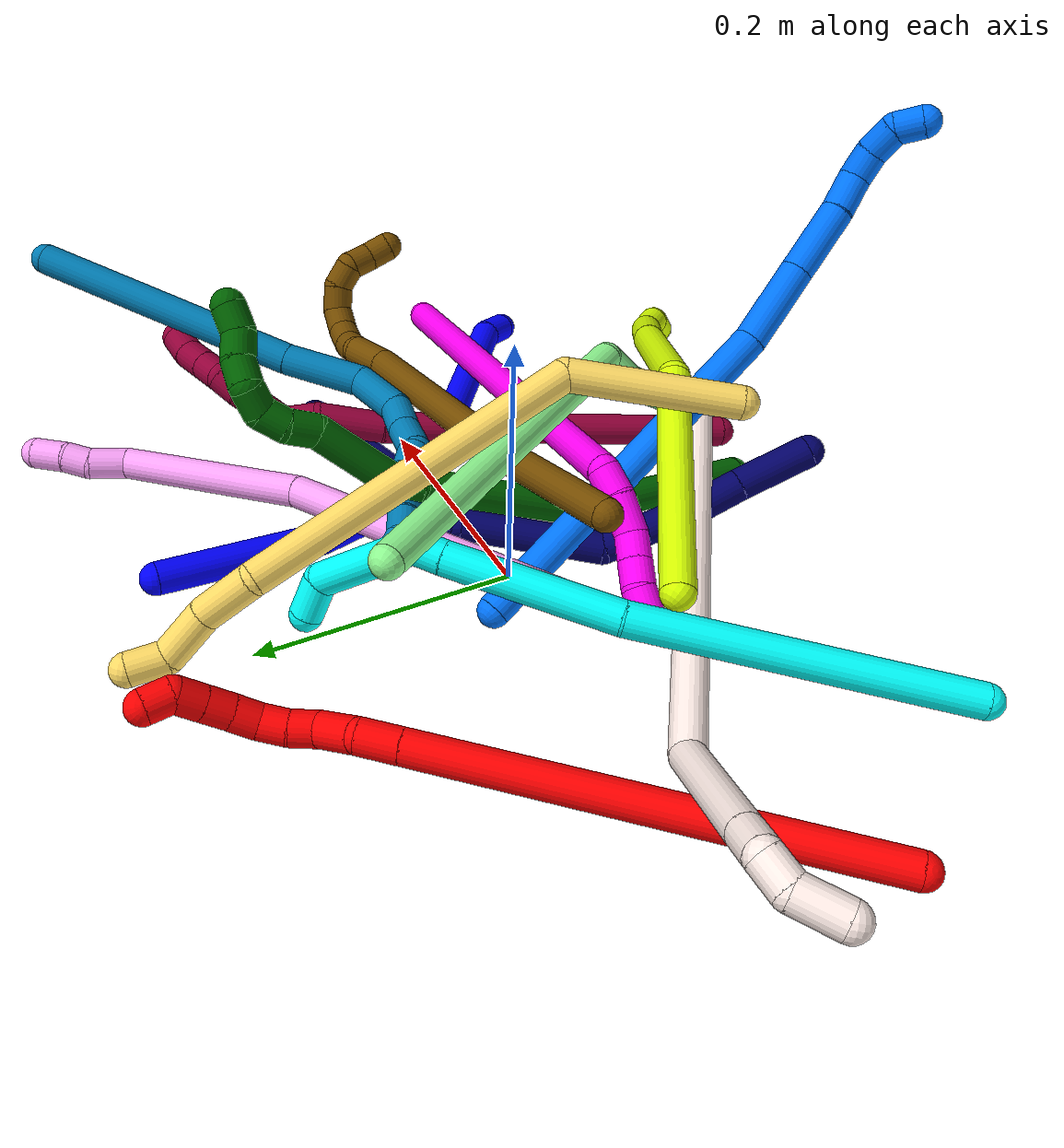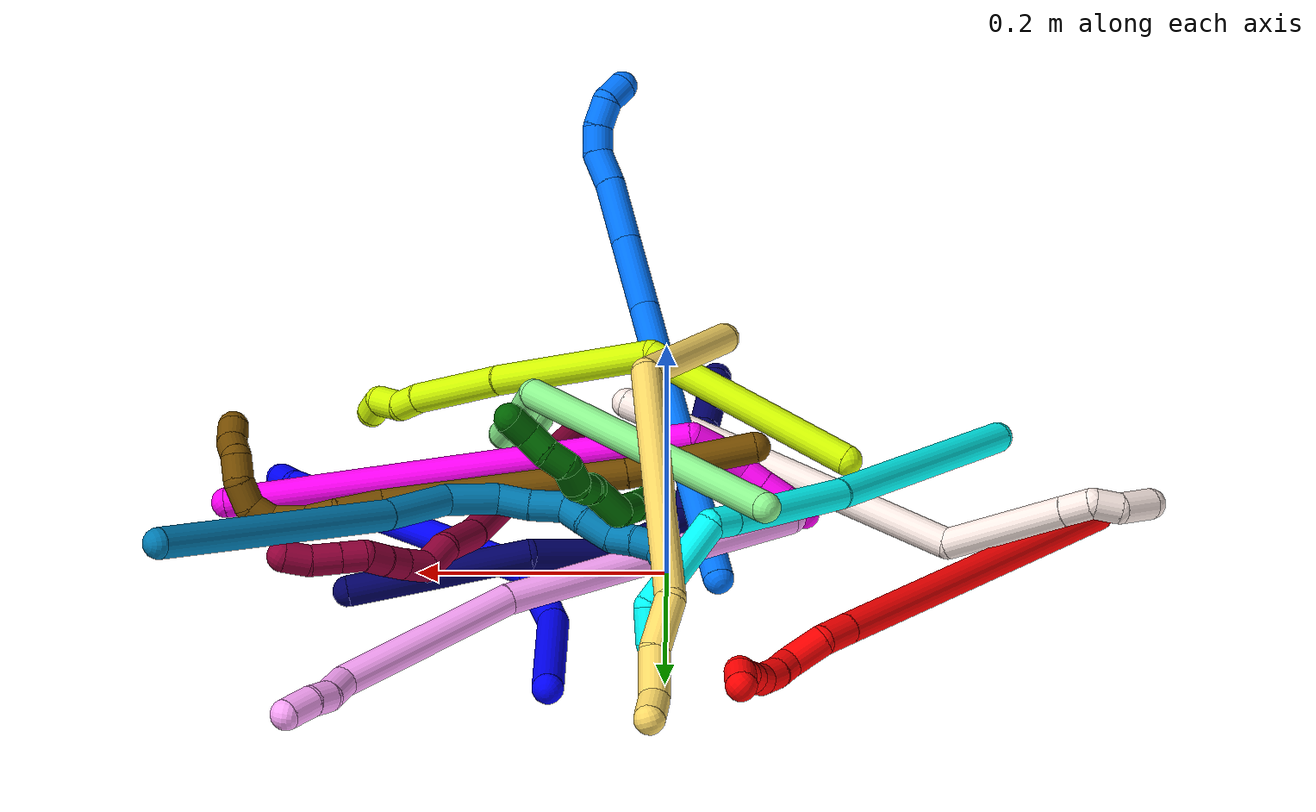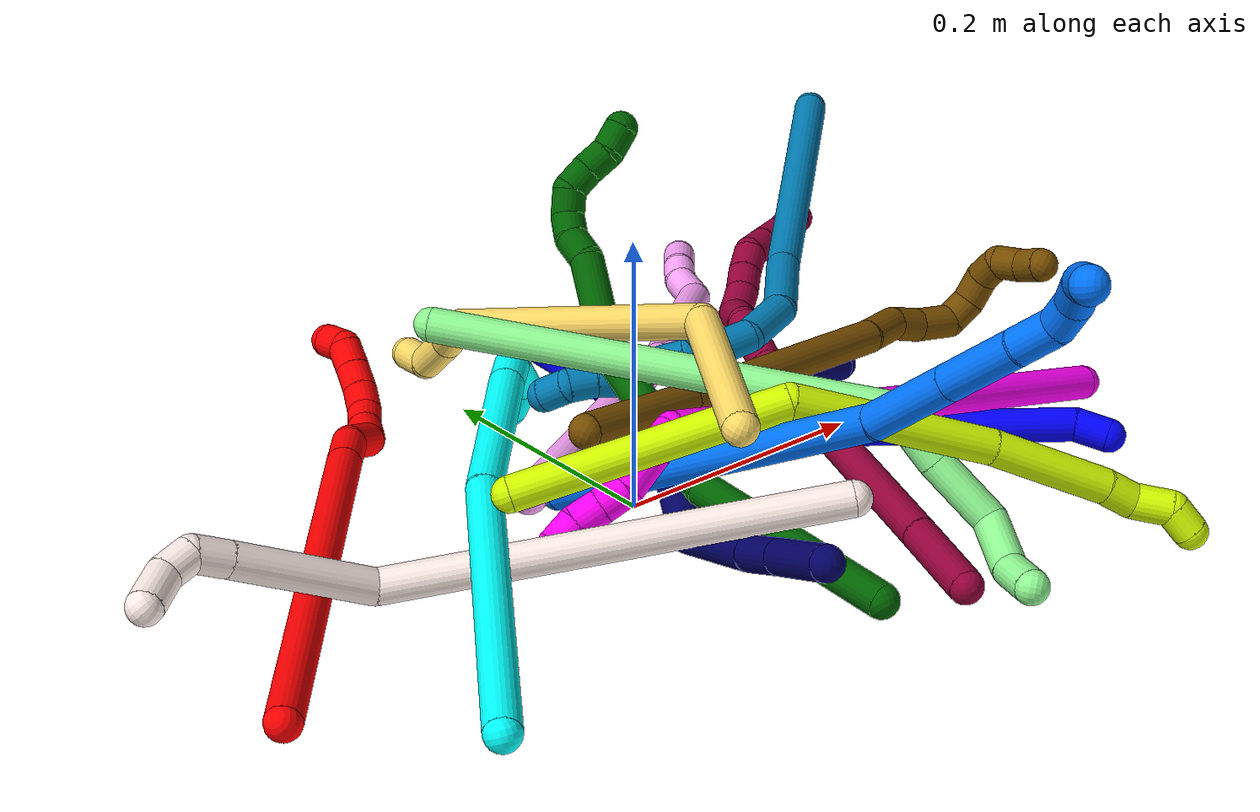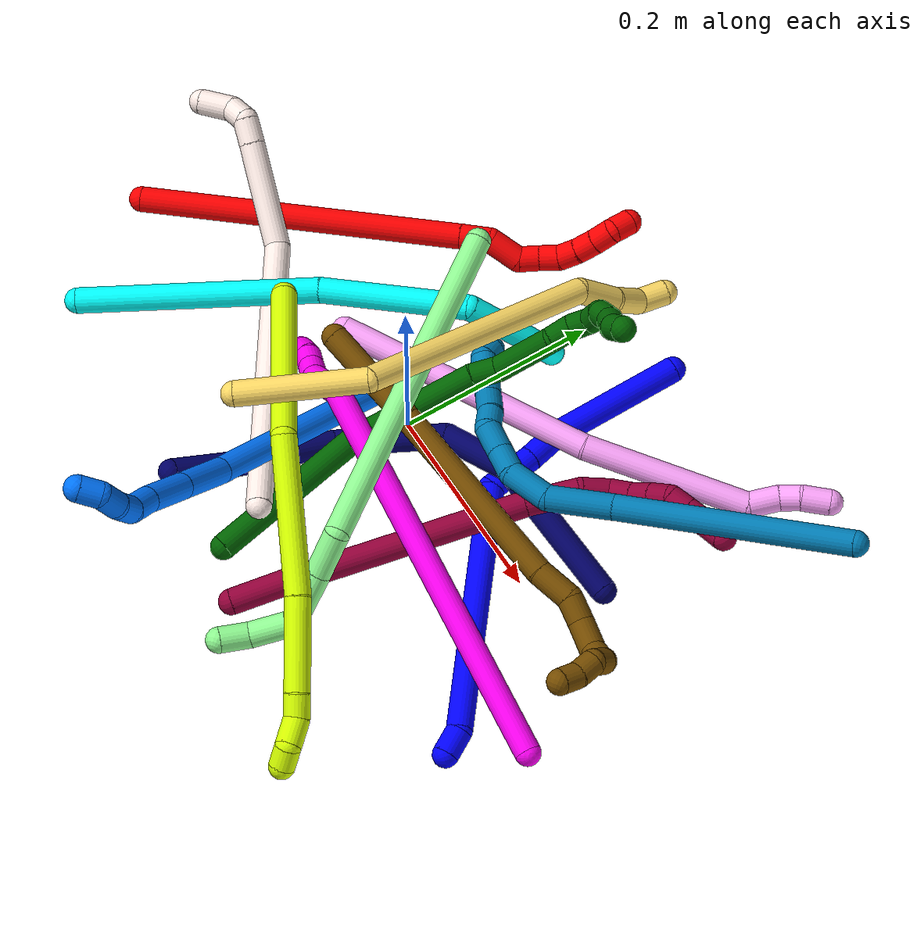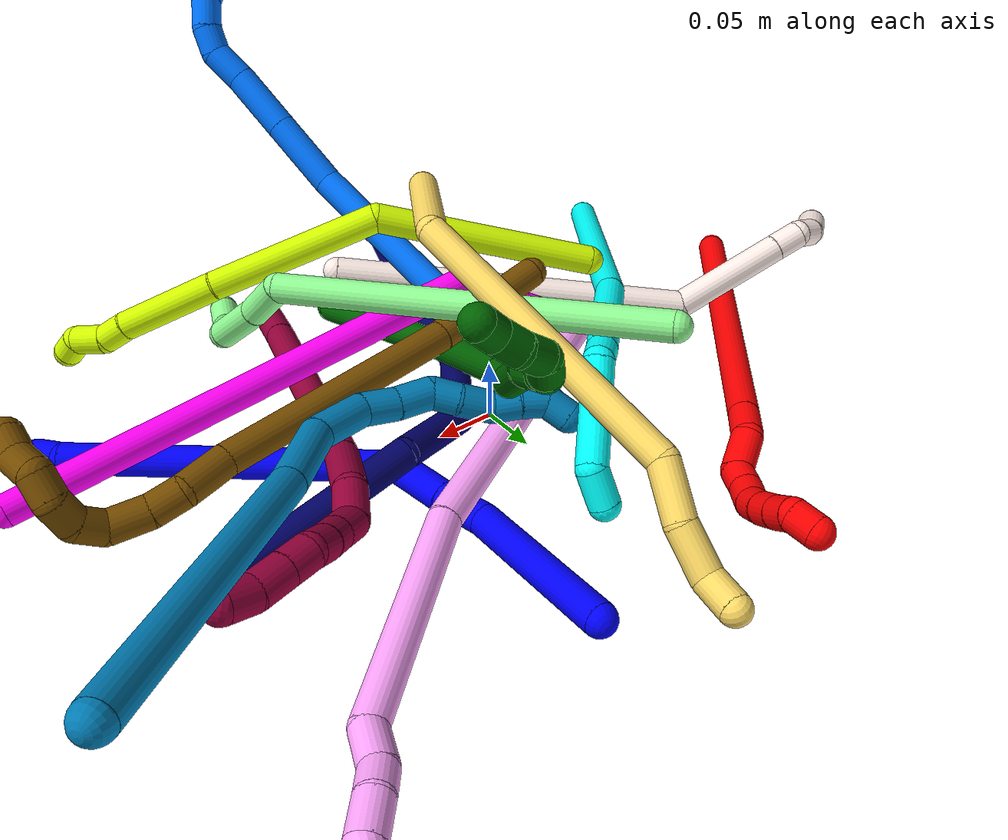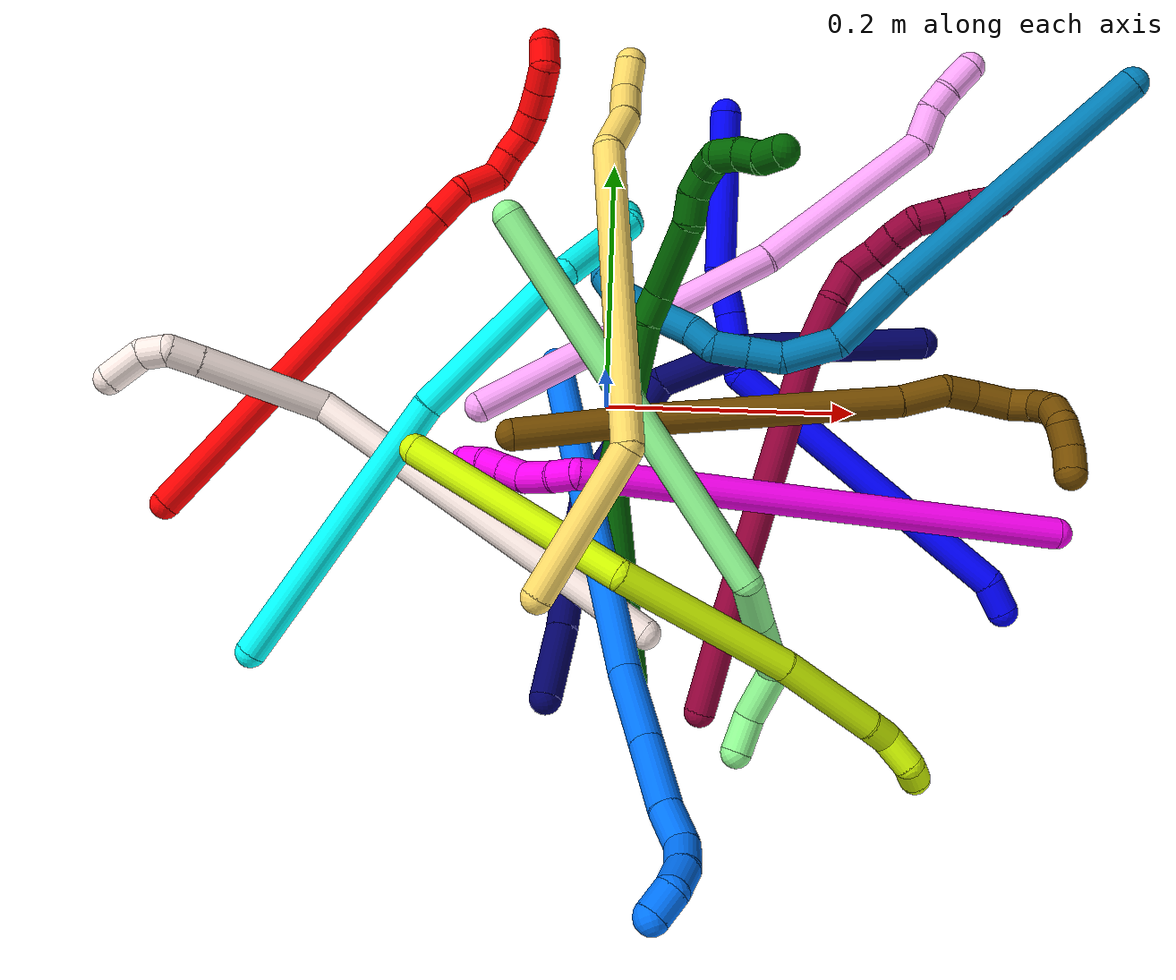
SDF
<sdf version="1.7">
 <world name="default">
  <plugin name="TubeGeneratorPlugin" filename="libtube_generator_plugin.so"/>
  <model name="photoneo_s_sensor">
   <static>1</static>
   <pose>0 0 2 1.57079 1.57079 3.14159</pose>
   <link name="link">
    <inertial><mass>0.1</mass></inertial>
    <sensor name="sensor" type="depth">
     <update_rate>30</update_rate>
     <camera>
      <horizontal_fov>1.22</horizontal_fov>
      <image><width>1920</width><height>1200</height><format>B8G8R8</format></image>
      <clip><near>0.1</near><far>4</far></clip>
      <depth_camera><output>points</output></depth_camera>
     </camera>
     <plugin name="camera_plugin" filename="libgazebo_ros_depth_camera.so">
      <baseline>0.2</baseline>
      <alwaysOn>1</alwaysOn>
      <updateRate>0.0</updateRate>
      <cameraName>camera_ir</cameraName>
      <imageTopicName>/camera/color/image_raw</imageTopicName>
      <cameraInfoTopicName>/camera/color/camera_info</cameraInfoTopicName>
      <depthImageTopicName>/camera/depth/image_raw</depthImageTopicName>
      <depthImageCameraInfoTopicName>/camera/depth/camera_info</depthImageCameraInfoTopicName>
      <pointCloudTopicName>/camera/depth/points</pointCloudTopicName>
      <frameName>fr_optical</frameName>
      <pointCloudCutoff>0.1</pointCloudCutoff>
      <pointCloudCutoffMax>2.0</pointCloudCutoffMax>
      <distortionK1>0</distortionK1>
      <distortionK2>0</distortionK2>
      <distortionK3>0</distortionK3>
      <distortionT1>0</distortionT1>
      <distortionT2>0</distortionT2>
      <CxPrime>0</CxPrime>
      <Cx>0</Cx>
      <Cy>0</Cy>
      <focalLength>0</focalLength>
      <hackBaseline>0</hackBaseline>
     </plugin>
    </sensor>
   </link>
  </model>
  <gravity>0 0 -9.8</gravity>
  <magnetic_field>6e-06 2.3e-05 -4.2e-05</magnetic_field>
  <atmosphere type="adiabatic"/>
  <physics name="default_physics" default="0" type="ode">
   <max_step_size>0.003</max_step_size>
   <real_time_factor>1</real_time_factor>
   <real_time_update_rate>1000</real_time_update_rate>
   <max_contacts>10000</max_contacts>
   <ode>
    <solver>
     <type>quick</type>
     <iters>100</iters>
     <sor>1.3</sor>
     <use_dynamic_moi_rescaling>0</use_dynamic_moi_rescaling>
    </solver>
    <constraints>
     <contact_max_correcting_vel>0</contact_max_correcting_vel>
     <contact_surface_layer>0.001</contact_surface_layer>
     <cfm>0</cfm>
     <erp>0.2</erp>
    </constraints>
   </ode>
  </physics>
  <scene><ambient>0.4 0.4 0.4 1</ambient><background>0.7 0.7 0.7 1</background><shadows>0</shadows></scene>
  <audio><device>default</device></audio>
  <spherical_coordinates>
   <surface_model>EARTH_WGS84</surface_model>
   <latitude_deg>0</latitude_deg>
   <longitude_deg>0</longitude_deg>
   <elevation>0</elevation>
   <heading_deg>0</heading_deg>
  </spherical_coordinates>
  <model name="bin">
   <static>1</static>
   <link name="bottom">
    <collision name="collision-bottom">
     <pose>0 0 -0.01 0 -0 0</pose>
     <geometry><box><size>0.8 0.6 0.02</size></box></geometry>
     <surface>
      <friction><ode><mu>100</mu><mu2>100</mu2></ode></friction>
      <contact><collide_bitmask>65535</collide_bitmask></contact>
     </surface>
    </collision>
   </link>
   <link name="west_wall">
    <collision name="collision-west_wall">
     <pose>-0.41 0 0.1 0 -0 0</pose>
     <geometry><box><size>0.02 0.6 0.2</size></box></geometry>
     <surface>
      <friction><ode><mu>100</mu><mu2>100</mu2></ode></friction>
      <contact><collide_bitmask>65535</collide_bitmask></contact>
     </surface>
    </collision>
   </link>
   <link name="east_wall">
    <collision name="collision-east_wall">
     <pose>0.41 0 0.1 0 -0 0</pose>
     <geometry><box><size>0.02 0.6 0.2</size></box></geometry>
     <surface>
      <friction><ode><mu>100</mu><mu2>100</mu2></ode></friction>
      <contact><collide_bitmask>65535</collide_bitmask></contact>
     </surface>
    </collision>
   </link>
   <link name="south_wall">
    <collision name="collision-south_wall">
     <pose>0 -0.31 0.1 0 -0 0</pose>
     <geometry><box><size>0.8 0.02 0.2</size></box></geometry>
     <surface>
      <friction><ode><mu>100</mu><mu2>100</mu2></ode></friction>
      <contact><collide_bitmask>65535</collide_bitmask></contact>
     </surface>
    </collision>
   </link>
   <link name="north_wall">
    <collision name="collision-north_wall">
     <pose>0 0.31 0.1 0 -0 0</pose>
     <geometry><box><size>0.8 0.02 0.2</size></box></geometry>
     <surface>
      <friction><ode><mu>100</mu><mu2>100</mu2></ode></friction>
      <contact><collide_bitmask>65535</collide_bitmask></contact>
     </surface>
    </collision>
   </link>
  </model>
  <model name="1">
   <static>0</static>
   <link name="1">
    <collision name="collision-cylinder-e_1_1_4">
     <pose>-0.000139 -0.010173 -0.063301 2.98225 -0.002169 -0.027163</pose>
     <geometry><cylinder><radius>0.0125</radius><length>0.128226</length></cylinder></geometry>
     <surface>
      <friction><ode><mu>1.16</mu><mu2>1.16</mu2><slip1>0</slip1><slip2>0</slip2></ode></friction>
      <contact><ode><kp>1e+06</kp><kd>1</kd><max_vel>0</max_vel><min_depth>0.001</min_depth></ode></contact>
     </surface>
    </collision>
    <visual name="visual-cylinder-e_1_1_4">
     <pose>-0.000139 -0.010173 -0.063301 2.98225 -0.002169 -0.027163</pose>
     <geometry><cylinder><radius>0.0125</radius><length>0.128226</length></cylinder></geometry>
     <material><ambient>0 0 1 1</ambient></material>
    </visual>
    <collision name="collision-cylinder-e_2_4_5">
     <pose>-0.000852 -0.027991 -0.144532 2.73855 -0.029453 -0.143932</pose>
     <geometry><cylinder><radius>0.0125</radius><length>0.039002</length></cylinder></geometry>
     <surface>
      <friction><ode><mu>1.16</mu><mu2>1.16</mu2><slip1>0</slip1><slip2>0</slip2></ode></friction>
      <contact><ode><kp>1e+06</kp><kd>1</kd><max_vel>0</max_vel><min_depth>0.001</min_depth></ode></contact>
     </surface>
    </collision>
    <visual name="visual-cylinder-e_2_4_5">
     <pose>-0.000852 -0.027991 -0.144532 2.73855 -0.029453 -0.143932</pose>
     <geometry><cylinder><radius>0.0125</radius><length>0.039002</length></cylinder></geometry>
     <material><ambient>0 0 1 1</ambient></material>
    </visual>
    <collision name="collision-cylinder-e_3_5_6">
     <pose>-0.00309 -0.044097 -0.185906 2.79524 -0.066637 -0.376564</pose>
     <geometry><cylinder><radius>0.0125</radius><length>0.049957</length></cylinder></geometry>
     <surface>
      <friction><ode><mu>1.16</mu><mu2>1.16</mu2><slip1>0</slip1><slip2>0</slip2></ode></friction>
      <contact><ode><kp>1e+06</kp><kd>1</kd><max_vel>0</max_vel><min_depth>0.001</min_depth></ode></contact>
     </surface>
    </collision>
    <visual name="visual-cylinder-e_3_5_6">
     <pose>-0.00309 -0.044097 -0.185906 2.79524 -0.066637 -0.376564</pose>
     <geometry><cylinder><radius>0.0125</radius><length>0.049957</length></cylinder></geometry>
     <material><ambient>0 0 1 1</ambient></material>
    </visual>
    <collision name="collision-cylinder-e_4_6_7">
     <pose>-0.002627 -0.165091 -0.271459 2.07512 0.01654 0.02802</pose>
     <geometry><cylinder><radius>0.0125</radius><length>0.257105</length></cylinder></geometry>
     <surface>
      <friction><ode><mu>1.16</mu><mu2>1.16</mu2><slip1>0</slip1><slip2>0</slip2></ode></friction>
      <contact><ode><kp>1e+06</kp><kd>1</kd><max_vel>0</max_vel><min_depth>0.001</min_depth></ode></contact>
     </surface>
    </collision>
    <visual name="visual-cylinder-e_4_6_7">
     <pose>-0.002627 -0.165091 -0.271459 2.07512 0.01654 0.02802</pose>
     <geometry><cylinder><radius>0.0125</radius><length>0.257105</length></cylinder></geometry>
     <material><ambient>0 0 1 1</ambient></material>
    </visual>
    <collision name="collision-cylinder-e_5_7_2">
     <pose>0.001659 -0.285325 -0.343632 2.48835 0.16885 0.489609</pose>
     <geometry><cylinder><radius>0.0125</radius><length>0.025709</length></cylinder></geometry>
     <surface>
      <friction><ode><mu>1.16</mu><mu2>1.16</mu2><slip1>0</slip1><slip2>0</slip2></ode></friction>
      <contact><ode><kp>1e+06</kp><kd>1</kd><max_vel>0</max_vel><min_depth>0.001</min_depth></ode></contact>
     </surface>
    </collision>
    <visual name="visual-cylinder-e_5_7_2">
     <pose>0.001659 -0.285325 -0.343632 2.48835 0.16885 0.489609</pose>
     <geometry><cylinder><radius>0.0125</radius><length>0.025709</length></cylinder></geometry>
     <material><ambient>0 0 1 1</ambient></material>
    </visual>
    <collision name="collision-sphere-2">
     <pose>0.003819 -0.293026 -0.353694 0 -0 0</pose>
     <geometry><sphere><radius>0.0125</radius></sphere></geometry>
     <surface>
      <friction><ode><mu>1.16</mu><mu2>1.16</mu2><slip1>0</slip1><slip2>0</slip2></ode></friction>
      <contact><ode><kp>1e+06</kp><kd>1</kd><max_vel>0</max_vel><min_depth>0.001</min_depth></ode></contact>
     </surface>
    </collision>
    <visual name="visual-sphere-2">
     <pose>0.003819 -0.293026 -0.353694 0 -0 0</pose>
     <geometry><sphere><radius>0.0125</radius></sphere></geometry>
     <material><ambient>0 0 1 1</ambient></material>
    </visual>
    <collision name="collision-sphere-7">
     <pose>-0.000501 -0.277624 -0.333569 0 -0 0</pose>
     <geometry><sphere><radius>0.0125</radius></sphere></geometry>
     <surface>
      <friction><ode><mu>1.16</mu><mu2>1.16</mu2><slip1>0</slip1><slip2>0</slip2></ode></friction>
      <contact><ode><kp>1e+06</kp><kd>1</kd><max_vel>0</max_vel><min_depth>0.001</min_depth></ode></contact>
     </surface>
    </collision>
    <visual name="visual-sphere-7">
     <pose>-0.000501 -0.277624 -0.333569 0 -0 0</pose>
     <geometry><sphere><radius>0.0125</radius></sphere></geometry>
     <material><ambient>0 0 1 1</ambient></material>
    </visual>
    <collision name="collision-sphere-6">
     <pose>-0.004753 -0.052558 -0.20935 0 -0 0</pose>
     <geometry><sphere><radius>0.0125</radius></sphere></geometry>
     <surface>
      <friction><ode><mu>1.16</mu><mu2>1.16</mu2><slip1>0</slip1><slip2>0</slip2></ode></friction>
      <contact><ode><kp>1e+06</kp><kd>1</kd><max_vel>0</max_vel><min_depth>0.001</min_depth></ode></contact>
     </surface>
    </collision>
    <visual name="visual-sphere-6">
     <pose>-0.004753 -0.052558 -0.20935 0 -0 0</pose>
     <geometry><sphere><radius>0.0125</radius></sphere></geometry>
     <material><ambient>0 0 1 1</ambient></material>
    </visual>
    <collision name="collision-sphere-5">
     <pose>-0.001427 -0.035636 -0.162463 0 -0 0</pose>
     <geometry><sphere><radius>0.0125</radius></sphere></geometry>
     <surface>
      <friction><ode><mu>1.16</mu><mu2>1.16</mu2><slip1>0</slip1><slip2>0</slip2></ode></friction>
      <contact><ode><kp>1e+06</kp><kd>1</kd><max_vel>0</max_vel><min_depth>0.001</min_depth></ode></contact>
     </surface>
    </collision>
    <visual name="visual-sphere-5">
     <pose>-0.001427 -0.035636 -0.162463 0 -0 0</pose>
     <geometry><sphere><radius>0.0125</radius></sphere></geometry>
     <material><ambient>0 0 1 1</ambient></material>
    </visual>
    <collision name="collision-sphere-1">
     <geometry><sphere><radius>0.0125</radius></sphere></geometry>
     <surface>
      <friction><ode><mu>1.16</mu><mu2>1.16</mu2><slip1>0</slip1><slip2>0</slip2></ode></friction>
      <contact><ode><kp>1e+06</kp><kd>1</kd><max_vel>0</max_vel><min_depth>0.001</min_depth></ode></contact>
     </surface>
    </collision>
    <visual name="visual-sphere-1">
     <geometry><sphere><radius>0.0125</radius></sphere></geometry>
     <material><ambient>0 0 1 1</ambient></material>
    </visual>
    <collision name="collision-sphere-4">
     <pose>-0.000278 -0.020346 -0.126602 0 -0 0</pose>
     <geometry><sphere><radius>0.0125</radius></sphere></geometry>
     <surface>
      <friction><ode><mu>1.16</mu><mu2>1.16</mu2><slip1>0</slip1><slip2>0</slip2></ode></friction>
      <contact><ode><kp>1e+06</kp><kd>1</kd><max_vel>0</max_vel><min_depth>0.001</min_depth></ode></contact>
     </surface>
    </collision>
    <visual name="visual-sphere-4">
     <pose>-0.000278 -0.020346 -0.126602 0 -0 0</pose>
     <geometry><sphere><radius>0.0125</radius></sphere></geometry>
     <material><ambient>0 0 1 1</ambient></material>
    </visual>
    <inertial>
     <pose>-0.001676 -0.10876 -0.203339 0 -0 0</pose>
     <mass>0.5</mass>
     <inertia>
      <ixx>0.001657</ixx>
      <ixy>0</ixy>
      <ixz>0</ixz>
      <iyy>-0.000877</iyy>
      <iyz>0</iyz>
      <izz>0.001235</izz>
     </inertia>
    </inertial>
   </link>
   <pose>0.090035 0.242398 0.017252 -0.829258 1.48507 0.571272</pose>
  </model>
  <model name="2">
   <static>0</static>
   <link name="2">
    <collision name="collision-cylinder-e_1_1_4">
     <pose>0.090206 0.098156 0.085529 -0.854029 0.605924 -0.282565</pose>
     <geometry><cylinder><radius>0.0125</radius><length>0.316776</length></cylinder></geometry>
     <surface>
      <friction><ode><mu>1.16</mu><mu2>1.16</mu2><slip1>0</slip1><slip2>0</slip2></ode></friction>
      <contact><ode><kp>1e+06</kp><kd>1</kd><max_vel>0</max_vel><min_depth>0.001</min_depth></ode></contact>
     </surface>
    </collision>
    <visual name="visual-cylinder-e_1_1_4">
     <pose>0.090206 0.098156 0.085529 -0.854029 0.605924 -0.282565</pose>
     <geometry><cylinder><radius>0.0125</radius><length>0.316776</length></cylinder></geometry>
     <material><ambient>1 0 0 1</ambient></material>
    </visual>
    <collision name="collision-cylinder-e_2_4_5">
     <pose>0.18873 0.205389 0.179225 -0.838207 0.598079 -0.272972</pose>
     <geometry><cylinder><radius>0.0125</radius><length>0.02955</length></cylinder></geometry>
     <surface>
      <friction><ode><mu>1.16</mu><mu2>1.16</mu2><slip1>0</slip1><slip2>0</slip2></ode></friction>
      <contact><ode><kp>1e+06</kp><kd>1</kd><max_vel>0</max_vel><min_depth>0.001</min_depth></ode></contact>
     </surface>
    </collision>
    <visual name="visual-cylinder-e_2_4_5">
     <pose>0.18873 0.205389 0.179225 -0.838207 0.598079 -0.272972</pose>
     <geometry><cylinder><radius>0.0125</radius><length>0.02955</length></cylinder></geometry>
     <material><ambient>1 0 0 1</ambient></material>
    </visual>
    <collision name="collision-cylinder-e_3_5_6">
     <pose>0.201803 0.220541 0.202084 -0.392033 0.290562 -0.058089</pose>
     <geometry><cylinder><radius>0.0125</radius><length>0.033189</length></cylinder></geometry>
     <surface>
      <friction><ode><mu>1.16</mu><mu2>1.16</mu2><slip1>0</slip1><slip2>0</slip2></ode></friction>
      <contact><ode><kp>1e+06</kp><kd>1</kd><max_vel>0</max_vel><min_depth>0.001</min_depth></ode></contact>
     </surface>
    </collision>
    <visual name="visual-cylinder-e_3_5_6">
     <pose>0.201803 0.220541 0.202084 -0.392033 0.290562 -0.058089</pose>
     <geometry><cylinder><radius>0.0125</radius><length>0.033189</length></cylinder></geometry>
     <material><ambient>1 0 0 1</ambient></material>
    </visual>
    <collision name="collision-cylinder-e_4_6_7">
     <pose>0.214077 0.231668 0.221219 -0.849619 0.840871 -0.399107</pose>
     <geometry><cylinder><radius>0.0125</radius><length>0.02018</length></cylinder></geometry>
     <surface>
      <friction><ode><mu>1.16</mu><mu2>1.16</mu2><slip1>0</slip1><slip2>0</slip2></ode></friction>
      <contact><ode><kp>1e+06</kp><kd>1</kd><max_vel>0</max_vel><min_depth>0.001</min_depth></ode></contact>
     </surface>
    </collision>
    <visual name="visual-cylinder-e_4_6_7">
     <pose>0.214077 0.231668 0.221219 -0.849619 0.840871 -0.399107</pose>
     <geometry><cylinder><radius>0.0125</radius><length>0.02018</length></cylinder></geometry>
     <material><ambient>1 0 0 1</ambient></material>
    </visual>
    <collision name="collision-cylinder-e_5_7_8">
     <pose>0.228055 0.243132 0.230016 -0.974111 0.694781 -0.378918</pose>
     <geometry><cylinder><radius>0.0125</radius><length>0.020176</length></cylinder></geometry>
     <surface>
      <friction><ode><mu>1.16</mu><mu2>1.16</mu2><slip1>0</slip1><slip2>0</slip2></ode></friction>
      <contact><ode><kp>1e+06</kp><kd>1</kd><max_vel>0</max_vel><min_depth>0.001</min_depth></ode></contact>
     </surface>
    </collision>
    <visual name="visual-cylinder-e_5_7_8">
     <pose>0.228055 0.243132 0.230016 -0.974111 0.694781 -0.378918</pose>
     <geometry><cylinder><radius>0.0125</radius><length>0.020176</length></cylinder></geometry>
     <material><ambient>1 0 0 1</ambient></material>
    </visual>
    <collision name="collision-cylinder-e_6_8_9">
     <pose>0.241179 0.25699 0.234898 -1.50004 0.728789 -0.682869</pose>
     <geometry><cylinder><radius>0.0125</radius><length>0.020016</length></cylinder></geometry>
     <surface>
      <friction><ode><mu>1.16</mu><mu2>1.16</mu2><slip1>0</slip1><slip2>0</slip2></ode></friction>
      <contact><ode><kp>1e+06</kp><kd>1</kd><max_vel>0</max_vel><min_depth>0.001</min_depth></ode></contact>
     </surface>
    </collision>
    <visual name="visual-cylinder-e_6_8_9">
     <pose>0.241179 0.25699 0.234898 -1.50004 0.728789 -0.682869</pose>
     <geometry><cylinder><radius>0.0125</radius><length>0.020016</length></cylinder></geometry>
     <material><ambient>1 0 0 1</ambient></material>
    </visual>
    <collision name="collision-cylinder-e_7_9_10">
     <pose>0.254876 0.271542 0.234806 -1.65783 0.778359 -0.841437</pose>
     <geometry><cylinder><radius>0.0125</radius><length>0.020032</length></cylinder></geometry>
     <surface>
      <friction><ode><mu>1.16</mu><mu2>1.16</mu2><slip1>0</slip1><slip2>0</slip2></ode></friction>
      <contact><ode><kp>1e+06</kp><kd>1</kd><max_vel>0</max_vel><min_depth>0.001</min_depth></ode></contact>
     </surface>
    </collision>
    <visual name="visual-cylinder-e_7_9_10">
     <pose>0.254876 0.271542 0.234806 -1.65783 0.778359 -0.841437</pose>
     <geometry><cylinder><radius>0.0125</radius><length>0.020032</length></cylinder></geometry>
     <material><ambient>1 0 0 1</ambient></material>
    </visual>
    <collision name="collision-cylinder-e_8_10_11">
     <pose>0.268942 0.285681 0.232909 -1.75043 0.777231 -0.912011</pose>
     <geometry><cylinder><radius>0.0125</radius><length>0.020057</length></cylinder></geometry>
     <surface>
      <friction><ode><mu>1.16</mu><mu2>1.16</mu2><slip1>0</slip1><slip2>0</slip2></ode></friction>
      <contact><ode><kp>1e+06</kp><kd>1</kd><max_vel>0</max_vel><min_depth>0.001</min_depth></ode></contact>
     </surface>
    </collision>
    <visual name="visual-cylinder-e_8_10_11">
     <pose>0.268942 0.285681 0.232909 -1.75043 0.777231 -0.912011</pose>
     <geometry><cylinder><radius>0.0125</radius><length>0.020057</length></cylinder></geometry>
     <material><ambient>1 0 0 1</ambient></material>
    </visual>
    <collision name="collision-cylinder-e_9_11_2">
     <pose>0.285802 0.293666 0.23329 -0.520262 1.37866 -0.431906</pose>
     <geometry><cylinder><radius>0.0125</radius><length>0.020023</length></cylinder></geometry>
     <surface>
      <friction><ode><mu>1.16</mu><mu2>1.16</mu2><slip1>0</slip1><slip2>0</slip2></ode></friction>
      <contact><ode><kp>1e+06</kp><kd>1</kd><max_vel>0</max_vel><min_depth>0.001</min_depth></ode></contact>
     </surface>
    </collision>
    <visual name="visual-cylinder-e_9_11_2">
     <pose>0.285802 0.293666 0.23329 -0.520262 1.37866 -0.431906</pose>
     <geometry><cylinder><radius>0.0125</radius><length>0.020023</length></cylinder></geometry>
     <material><ambient>1 0 0 1</ambient></material>
    </visual>
    <collision name="collision-sphere-2">
     <pose>0.295629 0.294616 0.234949 0 -0 0</pose>
     <geometry><sphere><radius>0.0125</radius></sphere></geometry>
     <surface>
      <friction><ode><mu>1.16</mu><mu2>1.16</mu2><slip1>0</slip1><slip2>0</slip2></ode></friction>
      <contact><ode><kp>1e+06</kp><kd>1</kd><max_vel>0</max_vel><min_depth>0.001</min_depth></ode></contact>
     </surface>
    </collision>
    <visual name="visual-sphere-2">
     <pose>0.295629 0.294616 0.234949 0 -0 0</pose>
     <geometry><sphere><radius>0.0125</radius></sphere></geometry>
     <material><ambient>1 0 0 1</ambient></material>
    </visual>
    <collision name="collision-sphere-11">
     <pose>0.275975 0.292715 0.231632 0 -0 0</pose>
     <geometry><sphere><radius>0.0125</radius></sphere></geometry>
     <surface>
      <friction><ode><mu>1.16</mu><mu2>1.16</mu2><slip1>0</slip1><slip2>0</slip2></ode></friction>
      <contact><ode><kp>1e+06</kp><kd>1</kd><max_vel>0</max_vel><min_depth>0.001</min_depth></ode></contact>
     </surface>
    </collision>
    <visual name="visual-sphere-11">
     <pose>0.275975 0.292715 0.231632 0 -0 0</pose>
     <geometry><sphere><radius>0.0125</radius></sphere></geometry>
     <material><ambient>1 0 0 1</ambient></material>
    </visual>
    <collision name="collision-sphere-10">
     <pose>0.261909 0.278647 0.234186 0 -0 0</pose>
     <geometry><sphere><radius>0.0125</radius></sphere></geometry>
     <surface>
      <friction><ode><mu>1.16</mu><mu2>1.16</mu2><slip1>0</slip1><slip2>0</slip2></ode></friction>
      <contact><ode><kp>1e+06</kp><kd>1</kd><max_vel>0</max_vel><min_depth>0.001</min_depth></ode></contact>
     </surface>
    </collision>
    <visual name="visual-sphere-10">
     <pose>0.261909 0.278647 0.234186 0 -0 0</pose>
     <geometry><sphere><radius>0.0125</radius></sphere></geometry>
     <material><ambient>1 0 0 1</ambient></material>
    </visual>
    <collision name="collision-sphere-9">
     <pose>0.247844 0.264437 0.235426 0 -0 0</pose>
     <geometry><sphere><radius>0.0125</radius></sphere></geometry>
     <surface>
      <friction><ode><mu>1.16</mu><mu2>1.16</mu2><slip1>0</slip1><slip2>0</slip2></ode></friction>
      <contact><ode><kp>1e+06</kp><kd>1</kd><max_vel>0</max_vel><min_depth>0.001</min_depth></ode></contact>
     </surface>
    </collision>
    <visual name="visual-sphere-9">
     <pose>0.247844 0.264437 0.235426 0 -0 0</pose>
     <geometry><sphere><radius>0.0125</radius></sphere></geometry>
     <material><ambient>1 0 0 1</ambient></material>
    </visual>
    <collision name="collision-sphere-4">
     <pose>0.180411 0.196311 0.171059 0 -0 0</pose>
     <geometry><sphere><radius>0.0125</radius></sphere></geometry>
     <surface>
      <friction><ode><mu>1.16</mu><mu2>1.16</mu2><slip1>0</slip1><slip2>0</slip2></ode></friction>
      <contact><ode><kp>1e+06</kp><kd>1</kd><max_vel>0</max_vel><min_depth>0.001</min_depth></ode></contact>
     </surface>
    </collision>
    <visual name="visual-sphere-4">
     <pose>0.180411 0.196311 0.171059 0 -0 0</pose>
     <geometry><sphere><radius>0.0125</radius></sphere></geometry>
     <material><ambient>1 0 0 1</ambient></material>
    </visual>
    <collision name="collision-sphere-1">
     <geometry><sphere><radius>0.0125</radius></sphere></geometry>
     <surface>
      <friction><ode><mu>1.16</mu><mu2>1.16</mu2><slip1>0</slip1><slip2>0</slip2></ode></friction>
      <contact><ode><kp>1e+06</kp><kd>1</kd><max_vel>0</max_vel><min_depth>0.001</min_depth></ode></contact>
     </surface>
    </collision>
    <visual name="visual-sphere-1">
     <geometry><sphere><radius>0.0125</radius></sphere></geometry>
     <material><ambient>1 0 0 1</ambient></material>
    </visual>
    <collision name="collision-sphere-8">
     <pose>0.234514 0.249543 0.23437 0 -0 0</pose>
     <geometry><sphere><radius>0.0125</radius></sphere></geometry>
     <surface>
      <friction><ode><mu>1.16</mu><mu2>1.16</mu2><slip1>0</slip1><slip2>0</slip2></ode></friction>
      <contact><ode><kp>1e+06</kp><kd>1</kd><max_vel>0</max_vel><min_depth>0.001</min_depth></ode></contact>
     </surface>
    </collision>
    <visual name="visual-sphere-8">
     <pose>0.234514 0.249543 0.23437 0 -0 0</pose>
     <geometry><sphere><radius>0.0125</radius></sphere></geometry>
     <material><ambient>1 0 0 1</ambient></material>
    </visual>
    <collision name="collision-sphere-5">
     <pose>0.197049 0.214466 0.187391 0 -0 0</pose>
     <geometry><sphere><radius>0.0125</radius></sphere></geometry>
     <surface>
      <friction><ode><mu>1.16</mu><mu2>1.16</mu2><slip1>0</slip1><slip2>0</slip2></ode></friction>
      <contact><ode><kp>1e+06</kp><kd>1</kd><max_vel>0</max_vel><min_depth>0.001</min_depth></ode></contact>
     </surface>
    </collision>
    <visual name="visual-sphere-5">
     <pose>0.197049 0.214466 0.187391 0 -0 0</pose>
     <geometry><sphere><radius>0.0125</radius></sphere></geometry>
     <material><ambient>1 0 0 1</ambient></material>
    </visual>
    <collision name="collision-sphere-6">
     <pose>0.206558 0.226615 0.216776 0 -0 0</pose>
     <geometry><sphere><radius>0.0125</radius></sphere></geometry>
     <surface>
      <friction><ode><mu>1.16</mu><mu2>1.16</mu2><slip1>0</slip1><slip2>0</slip2></ode></friction>
      <contact><ode><kp>1e+06</kp><kd>1</kd><max_vel>0</max_vel><min_depth>0.001</min_depth></ode></contact>
     </surface>
    </collision>
    <visual name="visual-sphere-6">
     <pose>0.206558 0.226615 0.216776 0 -0 0</pose>
     <geometry><sphere><radius>0.0125</radius></sphere></geometry>
     <material><ambient>1 0 0 1</ambient></material>
    </visual>
    <collision name="collision-sphere-7">
     <pose>0.221596 0.236722 0.225661 0 -0 0</pose>
     <geometry><sphere><radius>0.0125</radius></sphere></geometry>
     <surface>
      <friction><ode><mu>1.16</mu><mu2>1.16</mu2><slip1>0</slip1><slip2>0</slip2></ode></friction>
      <contact><ode><kp>1e+06</kp><kd>1</kd><max_vel>0</max_vel><min_depth>0.001</min_depth></ode></contact>
     </surface>
    </collision>
    <visual name="visual-sphere-7">
     <pose>0.221596 0.236722 0.225661 0 -0 0</pose>
     <geometry><sphere><radius>0.0125</radius></sphere></geometry>
     <material><ambient>1 0 0 1</ambient></material>
    </visual>
    <inertial>
     <pose>0.141642 0.152512 0.1339 0 -0 0</pose>
     <mass>0.5</mass>
     <inertia>
      <ixx>0.001521</ixx>
      <ixy>0</ixy>
      <ixz>0</ixz>
      <iyy>0.001419</iyy>
      <iyz>0</iyz>
      <izz>-0.003165</izz>
     </inertia>
    </inertial>
   </link>
   <pose>-0.350486 -0.090534 0.011495 2.34429 0.051048 1.81404</pose>
  </model>
  <model name="3">
   <static>0</static>
   <link name="3">
    <collision name="collision-cylinder-e_1_1_4">
     <pose>0.103184 -0.001697 0.059919 0.028318 1.04452 0.0163</pose>
     <geometry><cylinder><radius>0.0125</radius><length>0.238664</length></cylinder></geometry>
     <surface>
      <friction><ode><mu>1.16</mu><mu2>1.16</mu2><slip1>0</slip1><slip2>0</slip2></ode></friction>
      <contact><ode><kp>1e+06</kp><kd>1</kd><max_vel>0</max_vel><min_depth>0.001</min_depth></ode></contact>
     </surface>
    </collision>
    <visual name="visual-cylinder-e_1_1_4">
     <pose>0.103184 -0.001697 0.059919 0.028318 1.04452 0.0163</pose>
     <geometry><cylinder><radius>0.0125</radius><length>0.238664</length></cylinder></geometry>
     <material><ambient>0.003922 1 0.996078 1</ambient></material>
    </visual>
    <collision name="collision-cylinder-e_2_4_5">
     <pose>0.261325 -0.014248 0.147703 0.371429 1.07246 0.222398</pose>
     <geometry><cylinder><radius>0.0125</radius><length>0.125132</length></cylinder></geometry>
     <surface>
      <friction><ode><mu>1.16</mu><mu2>1.16</mu2><slip1>0</slip1><slip2>0</slip2></ode></friction>
      <contact><ode><kp>1e+06</kp><kd>1</kd><max_vel>0</max_vel><min_depth>0.001</min_depth></ode></contact>
     </surface>
    </collision>
    <visual name="visual-cylinder-e_2_4_5">
     <pose>0.261325 -0.014248 0.147703 0.371429 1.07246 0.222398</pose>
     <geometry><cylinder><radius>0.0125</radius><length>0.125132</length></cylinder></geometry>
     <material><ambient>0.003922 1 0.996078 1</ambient></material>
    </visual>
    <collision name="collision-cylinder-e_3_5_6">
     <pose>0.32589 -0.027634 0.18047 0.476736 1.04954 0.279505</pose>
     <geometry><cylinder><radius>0.0125</radius><length>0.022161</length></cylinder></geometry>
     <surface>
      <friction><ode><mu>1.16</mu><mu2>1.16</mu2><slip1>0</slip1><slip2>0</slip2></ode></friction>
      <contact><ode><kp>1e+06</kp><kd>1</kd><max_vel>0</max_vel><min_depth>0.001</min_depth></ode></contact>
     </surface>
    </collision>
    <visual name="visual-cylinder-e_3_5_6">
     <pose>0.32589 -0.027634 0.18047 0.476736 1.04954 0.279505</pose>
     <geometry><cylinder><radius>0.0125</radius><length>0.022161</length></cylinder></geometry>
     <material><ambient>0.003922 1 0.996078 1</ambient></material>
    </visual>
    <collision name="collision-cylinder-e_4_6_7">
     <pose>0.376768 -0.028074 0.175283 -2.93715 1.3261 -2.88041</pose>
     <geometry><cylinder><radius>0.0125</radius><length>0.085072</length></cylinder></geometry>
     <surface>
      <friction><ode><mu>1.16</mu><mu2>1.16</mu2><slip1>0</slip1><slip2>0</slip2></ode></friction>
      <contact><ode><kp>1e+06</kp><kd>1</kd><max_vel>0</max_vel><min_depth>0.001</min_depth></ode></contact>
     </surface>
    </collision>
    <visual name="visual-cylinder-e_4_6_7">
     <pose>0.376768 -0.028074 0.175283 -2.93715 1.3261 -2.88041</pose>
     <geometry><cylinder><radius>0.0125</radius><length>0.085072</length></cylinder></geometry>
     <material><ambient>0.003922 1 0.996078 1</ambient></material>
    </visual>
    <collision name="collision-cylinder-e_5_7_2">
     <pose>0.426417 -0.018054 0.156431 -2.40612 0.616877 -1.38197</pose>
     <geometry><cylinder><radius>0.0125</radius><length>0.028971</length></cylinder></geometry>
     <surface>
      <friction><ode><mu>1.16</mu><mu2>1.16</mu2><slip1>0</slip1><slip2>0</slip2></ode></friction>
      <contact><ode><kp>1e+06</kp><kd>1</kd><max_vel>0</max_vel><min_depth>0.001</min_depth></ode></contact>
     </surface>
    </collision>
    <visual name="visual-cylinder-e_5_7_2">
     <pose>0.426417 -0.018054 0.156431 -2.40612 0.616877 -1.38197</pose>
     <geometry><cylinder><radius>0.0125</radius><length>0.028971</length></cylinder></geometry>
     <material><ambient>0.003922 1 0.996078 1</ambient></material>
    </visual>
    <collision name="collision-sphere-2">
     <pose>0.434797 -0.010127 0.147669 0 -0 0</pose>
     <geometry><sphere><radius>0.0125</radius></sphere></geometry>
     <surface>
      <friction><ode><mu>1.16</mu><mu2>1.16</mu2><slip1>0</slip1><slip2>0</slip2></ode></friction>
      <contact><ode><kp>1e+06</kp><kd>1</kd><max_vel>0</max_vel><min_depth>0.001</min_depth></ode></contact>
     </surface>
    </collision>
    <visual name="visual-sphere-2">
     <pose>0.434797 -0.010127 0.147669 0 -0 0</pose>
     <geometry><sphere><radius>0.0125</radius></sphere></geometry>
     <material><ambient>0.003922 1 0.996078 1</ambient></material>
    </visual>
    <collision name="collision-sphere-7">
     <pose>0.418037 -0.025982 0.165193 0 -0 0</pose>
     <geometry><sphere><radius>0.0125</radius></sphere></geometry>
     <surface>
      <friction><ode><mu>1.16</mu><mu2>1.16</mu2><slip1>0</slip1><slip2>0</slip2></ode></friction>
      <contact><ode><kp>1e+06</kp><kd>1</kd><max_vel>0</max_vel><min_depth>0.001</min_depth></ode></contact>
     </surface>
    </collision>
    <visual name="visual-sphere-7">
     <pose>0.418037 -0.025982 0.165193 0 -0 0</pose>
     <geometry><sphere><radius>0.0125</radius></sphere></geometry>
     <material><ambient>0.003922 1 0.996078 1</ambient></material>
    </visual>
    <collision name="collision-sphere-6">
     <pose>0.335499 -0.030166 0.185373 0 -0 0</pose>
     <geometry><sphere><radius>0.0125</radius></sphere></geometry>
     <surface>
      <friction><ode><mu>1.16</mu><mu2>1.16</mu2><slip1>0</slip1><slip2>0</slip2></ode></friction>
      <contact><ode><kp>1e+06</kp><kd>1</kd><max_vel>0</max_vel><min_depth>0.001</min_depth></ode></contact>
     </surface>
    </collision>
    <visual name="visual-sphere-6">
     <pose>0.335499 -0.030166 0.185373 0 -0 0</pose>
     <geometry><sphere><radius>0.0125</radius></sphere></geometry>
     <material><ambient>0.003922 1 0.996078 1</ambient></material>
    </visual>
    <collision name="collision-sphere-5">
     <pose>0.316281 -0.025102 0.175568 0 -0 0</pose>
     <geometry><sphere><radius>0.0125</radius></sphere></geometry>
     <surface>
      <friction><ode><mu>1.16</mu><mu2>1.16</mu2><slip1>0</slip1><slip2>0</slip2></ode></friction>
      <contact><ode><kp>1e+06</kp><kd>1</kd><max_vel>0</max_vel><min_depth>0.001</min_depth></ode></contact>
     </surface>
    </collision>
    <visual name="visual-sphere-5">
     <pose>0.316281 -0.025102 0.175568 0 -0 0</pose>
     <geometry><sphere><radius>0.0125</radius></sphere></geometry>
     <material><ambient>0.003922 1 0.996078 1</ambient></material>
    </visual>
    <collision name="collision-sphere-1">
     <geometry><sphere><radius>0.0125</radius></sphere></geometry>
     <surface>
      <friction><ode><mu>1.16</mu><mu2>1.16</mu2><slip1>0</slip1><slip2>0</slip2></ode></friction>
      <contact><ode><kp>1e+06</kp><kd>1</kd><max_vel>0</max_vel><min_depth>0.001</min_depth></ode></contact>
     </surface>
    </collision>
    <visual name="visual-sphere-1">
     <geometry><sphere><radius>0.0125</radius></sphere></geometry>
     <material><ambient>0.003922 1 0.996078 1</ambient></material>
    </visual>
    <collision name="collision-sphere-4">
     <pose>0.206368 -0.003395 0.119838 0 -0 0</pose>
     <geometry><sphere><radius>0.0125</radius></sphere></geometry>
     <surface>
      <friction><ode><mu>1.16</mu><mu2>1.16</mu2><slip1>0</slip1><slip2>0</slip2></ode></friction>
      <contact><ode><kp>1e+06</kp><kd>1</kd><max_vel>0</max_vel><min_depth>0.001</min_depth></ode></contact>
     </surface>
    </collision>
    <visual name="visual-sphere-4">
     <pose>0.206368 -0.003395 0.119838 0 -0 0</pose>
     <geometry><sphere><radius>0.0125</radius></sphere></geometry>
     <material><ambient>0.003922 1 0.996078 1</ambient></material>
    </visual>
    <inertial>
     <pose>0.217909 -0.011423 0.112452 0 -0 0</pose>
     <mass>0.5</mass>
     <inertia>
      <ixx>0.000696</ixx>
      <ixy>0</ixy>
      <ixz>0</ixz>
      <iyy>0.001384</iyy>
      <iyz>0</iyz>
      <izz>-0.001139</izz>
     </inertia>
    </inertial>
   </link>
   <pose>-0.272157 -0.205715 0.028484 -0.279761 0.354425 0.839336</pose>
  </model>
  <model name="4">
   <static>0</static>
   <link name="4">
    <collision name="collision-cylinder-e_1_1_4">
     <pose>0.052801 -0.071991 0.09312 0.658119 0.421685 0.145908</pose>
     <geometry><cylinder><radius>0.0125</radius><length>0.258008</length></cylinder></geometry>
     <surface>
      <friction><ode><mu>1.16</mu><mu2>1.16</mu2><slip1>0</slip1><slip2>0</slip2></ode></friction>
      <contact><ode><kp>1e+06</kp><kd>1</kd><max_vel>0</max_vel><min_depth>0.001</min_depth></ode></contact>
     </surface>
    </collision>
    <visual name="visual-cylinder-e_1_1_4">
     <pose>0.052801 -0.071991 0.09312 0.658119 0.421685 0.145908</pose>
     <geometry><cylinder><radius>0.0125</radius><length>0.258008</length></cylinder></geometry>
     <material><ambient>1 0.65098 0.996078 1</ambient></material>
    </visual>
    <collision name="collision-cylinder-e_2_4_5">
     <pose>0.140756 -0.200399 0.233637 0.872074 0.445151 0.210135</pose>
     <geometry><cylinder><radius>0.0125</radius><length>0.163282</length></cylinder></geometry>
     <surface>
      <friction><ode><mu>1.16</mu><mu2>1.16</mu2><slip1>0</slip1><slip2>0</slip2></ode></friction>
      <contact><ode><kp>1e+06</kp><kd>1</kd><max_vel>0</max_vel><min_depth>0.001</min_depth></ode></contact>
     </surface>
    </collision>
    <visual name="visual-cylinder-e_2_4_5">
     <pose>0.140756 -0.200399 0.233637 0.872074 0.445151 0.210135</pose>
     <geometry><cylinder><radius>0.0125</radius><length>0.163282</length></cylinder></geometry>
     <material><ambient>1 0.65098 0.996078 1</ambient></material>
    </visual>
    <collision name="collision-cylinder-e_3_5_6">
     <pose>0.187056 -0.267307 0.282576 1.42487 0.810363 0.709608</pose>
     <geometry><cylinder><radius>0.0125</radius><length>0.030766</length></cylinder></geometry>
     <surface>
      <friction><ode><mu>1.16</mu><mu2>1.16</mu2><slip1>0</slip1><slip2>0</slip2></ode></friction>
      <contact><ode><kp>1e+06</kp><kd>1</kd><max_vel>0</max_vel><min_depth>0.001</min_depth></ode></contact>
     </surface>
    </collision>
    <visual name="visual-cylinder-e_3_5_6">
     <pose>0.187056 -0.267307 0.282576 1.42487 0.810363 0.709608</pose>
     <geometry><cylinder><radius>0.0125</radius><length>0.030766</length></cylinder></geometry>
     <material><ambient>1 0.65098 0.996078 1</ambient></material>
    </visual>
    <collision name="collision-cylinder-e_4_6_7">
     <pose>0.205714 -0.283456 0.288269 0.937994 0.819369 0.433176</pose>
     <geometry><cylinder><radius>0.0125</radius><length>0.020561</length></cylinder></geometry>
     <surface>
      <friction><ode><mu>1.16</mu><mu2>1.16</mu2><slip1>0</slip1><slip2>0</slip2></ode></friction>
      <contact><ode><kp>1e+06</kp><kd>1</kd><max_vel>0</max_vel><min_depth>0.001</min_depth></ode></contact>
     </surface>
    </collision>
    <visual name="visual-cylinder-e_4_6_7">
     <pose>0.205714 -0.283456 0.288269 0.937994 0.819369 0.433176</pose>
     <geometry><cylinder><radius>0.0125</radius><length>0.020561</length></cylinder></geometry>
     <material><ambient>1 0.65098 0.996078 1</ambient></material>
    </visual>
    <collision name="collision-cylinder-e_5_7_2">
     <pose>0.220941 -0.298529 0.29869 0.983141 0.598585 0.327454</pose>
     <geometry><cylinder><radius>0.0125</radius><length>0.027383</length></cylinder></geometry>
     <surface>
      <friction><ode><mu>1.16</mu><mu2>1.16</mu2><slip1>0</slip1><slip2>0</slip2></ode></friction>
      <contact><ode><kp>1e+06</kp><kd>1</kd><max_vel>0</max_vel><min_depth>0.001</min_depth></ode></contact>
     </surface>
    </collision>
    <visual name="visual-cylinder-e_5_7_2">
     <pose>0.220941 -0.298529 0.29869 0.983141 0.598585 0.327454</pose>
     <geometry><cylinder><radius>0.0125</radius><length>0.027383</length></cylinder></geometry>
     <material><ambient>1 0.65098 0.996078 1</ambient></material>
    </visual>
    <collision name="collision-sphere-2">
     <pose>0.228656 -0.307943 0.304961 0 -0 0</pose>
     <geometry><sphere><radius>0.0125</radius></sphere></geometry>
     <surface>
      <friction><ode><mu>1.16</mu><mu2>1.16</mu2><slip1>0</slip1><slip2>0</slip2></ode></friction>
      <contact><ode><kp>1e+06</kp><kd>1</kd><max_vel>0</max_vel><min_depth>0.001</min_depth></ode></contact>
     </surface>
    </collision>
    <visual name="visual-sphere-2">
     <pose>0.228656 -0.307943 0.304961 0 -0 0</pose>
     <geometry><sphere><radius>0.0125</radius></sphere></geometry>
     <material><ambient>1 0.65098 0.996078 1</ambient></material>
    </visual>
    <collision name="collision-sphere-7">
     <pose>0.213226 -0.289116 0.292419 0 -0 0</pose>
     <geometry><sphere><radius>0.0125</radius></sphere></geometry>
     <surface>
      <friction><ode><mu>1.16</mu><mu2>1.16</mu2><slip1>0</slip1><slip2>0</slip2></ode></friction>
      <contact><ode><kp>1e+06</kp><kd>1</kd><max_vel>0</max_vel><min_depth>0.001</min_depth></ode></contact>
     </surface>
    </collision>
    <visual name="visual-sphere-7">
     <pose>0.213226 -0.289116 0.292419 0 -0 0</pose>
     <geometry><sphere><radius>0.0125</radius></sphere></geometry>
     <material><ambient>1 0.65098 0.996078 1</ambient></material>
    </visual>
    <collision name="collision-sphere-6">
     <pose>0.198202 -0.277797 0.284118 0 -0 0</pose>
     <geometry><sphere><radius>0.0125</radius></sphere></geometry>
     <surface>
      <friction><ode><mu>1.16</mu><mu2>1.16</mu2><slip1>0</slip1><slip2>0</slip2></ode></friction>
      <contact><ode><kp>1e+06</kp><kd>1</kd><max_vel>0</max_vel><min_depth>0.001</min_depth></ode></contact>
     </surface>
    </collision>
    <visual name="visual-sphere-6">
     <pose>0.198202 -0.277797 0.284118 0 -0 0</pose>
     <geometry><sphere><radius>0.0125</radius></sphere></geometry>
     <material><ambient>1 0.65098 0.996078 1</ambient></material>
    </visual>
    <collision name="collision-sphere-5">
     <pose>0.175911 -0.256817 0.281034 0 -0 0</pose>
     <geometry><sphere><radius>0.0125</radius></sphere></geometry>
     <surface>
      <friction><ode><mu>1.16</mu><mu2>1.16</mu2><slip1>0</slip1><slip2>0</slip2></ode></friction>
      <contact><ode><kp>1e+06</kp><kd>1</kd><max_vel>0</max_vel><min_depth>0.001</min_depth></ode></contact>
     </surface>
    </collision>
    <visual name="visual-sphere-5">
     <pose>0.175911 -0.256817 0.281034 0 -0 0</pose>
     <geometry><sphere><radius>0.0125</radius></sphere></geometry>
     <material><ambient>1 0.65098 0.996078 1</ambient></material>
    </visual>
    <collision name="collision-sphere-1">
     <geometry><sphere><radius>0.0125</radius></sphere></geometry>
     <surface>
      <friction><ode><mu>1.16</mu><mu2>1.16</mu2><slip1>0</slip1><slip2>0</slip2></ode></friction>
      <contact><ode><kp>1e+06</kp><kd>1</kd><max_vel>0</max_vel><min_depth>0.001</min_depth></ode></contact>
     </surface>
    </collision>
    <visual name="visual-sphere-1">
     <geometry><sphere><radius>0.0125</radius></sphere></geometry>
     <material><ambient>1 0.65098 0.996078 1</ambient></material>
    </visual>
    <collision name="collision-sphere-4">
     <pose>0.105602 -0.143982 0.18624 0 -0 0</pose>
     <geometry><sphere><radius>0.0125</radius></sphere></geometry>
     <surface>
      <friction><ode><mu>1.16</mu><mu2>1.16</mu2><slip1>0</slip1><slip2>0</slip2></ode></friction>
      <contact><ode><kp>1e+06</kp><kd>1</kd><max_vel>0</max_vel><min_depth>0.001</min_depth></ode></contact>
     </surface>
    </collision>
    <visual name="visual-sphere-4">
     <pose>0.105602 -0.143982 0.18624 0 -0 0</pose>
     <geometry><sphere><radius>0.0125</radius></sphere></geometry>
     <material><ambient>1 0.65098 0.996078 1</ambient></material>
    </visual>
    <inertial>
     <pose>0.105282 -0.147045 0.169949 0 -0 0</pose>
     <mass>0.5</mass>
     <inertia>
      <ixx>0.001913</ixx>
      <ixy>0</ixy>
      <ixz>0</ixz>
      <iyy>0.001683</iyy>
      <iyz>0</iyz>
      <izz>0.000334</izz>
     </inertia>
    </inertial>
   </link>
   <pose>-0.099042 -0.008751 0.045561 1.48348 -0.806615 1.39527</pose>
  </model>
  <model name="5">
   <static>0</static>
   <link name="5">
    <collision name="collision-cylinder-e_1_1_4">
     <pose>0.063119 -0.00054 0.004887 0.110085 1.49306 0.101858</pose>
     <geometry><cylinder><radius>0.0125</radius><length>0.12662</length></cylinder></geometry>
     <surface>
      <friction><ode><mu>1.16</mu><mu2>1.16</mu2><slip1>0</slip1><slip2>0</slip2></ode></friction>
      <contact><ode><kp>1e+06</kp><kd>1</kd><max_vel>0</max_vel><min_depth>0.001</min_depth></ode></contact>
     </surface>
    </collision>
    <visual name="visual-cylinder-e_1_1_4">
     <pose>0.063119 -0.00054 0.004887 0.110085 1.49306 0.101858</pose>
     <geometry><cylinder><radius>0.0125</radius><length>0.12662</length></cylinder></geometry>
     <material><ambient>1 0.858824 0.4 1</ambient></material>
    </visual>
    <collision name="collision-cylinder-e_2_4_5">
     <pose>0.226937 0.041229 -0.060862 -2.60192 0.885378 -2.08531</pose>
     <geometry><cylinder><radius>0.0125</radius><length>0.260152</length></cylinder></geometry>
     <surface>
      <friction><ode><mu>1.16</mu><mu2>1.16</mu2><slip1>0</slip1><slip2>0</slip2></ode></friction>
      <contact><ode><kp>1e+06</kp><kd>1</kd><max_vel>0</max_vel><min_depth>0.001</min_depth></ode></contact>
     </surface>
    </collision>
    <visual name="visual-cylinder-e_2_4_5">
     <pose>0.226937 0.041229 -0.060862 -2.60192 0.885378 -2.08531</pose>
     <geometry><cylinder><radius>0.0125</radius><length>0.260152</length></cylinder></geometry>
     <material><ambient>1 0.858824 0.4 1</ambient></material>
    </visual>
    <collision name="collision-cylinder-e_3_5_6">
     <pose>0.343846 0.079712 -0.146368 2.88968 0.812487 2.56904</pose>
     <geometry><cylinder><radius>0.0125</radius><length>0.044657</length></cylinder></geometry>
     <surface>
      <friction><ode><mu>1.16</mu><mu2>1.16</mu2><slip1>0</slip1><slip2>0</slip2></ode></friction>
      <contact><ode><kp>1e+06</kp><kd>1</kd><max_vel>0</max_vel><min_depth>0.001</min_depth></ode></contact>
     </surface>
    </collision>
    <visual name="visual-cylinder-e_3_5_6">
     <pose>0.343846 0.079712 -0.146368 2.88968 0.812487 2.56904</pose>
     <geometry><cylinder><radius>0.0125</radius><length>0.044657</length></cylinder></geometry>
     <material><ambient>1 0.858824 0.4 1</ambient></material>
    </visual>
    <collision name="collision-cylinder-e_4_6_7">
     <pose>0.371925 0.076392 -0.177398 -3.11021 0.633227 -3.04587</pose>
     <geometry><cylinder><radius>0.0125</radius><length>0.040113</length></cylinder></geometry>
     <surface>
      <friction><ode><mu>1.16</mu><mu2>1.16</mu2><slip1>0</slip1><slip2>0</slip2></ode></friction>
      <contact><ode><kp>1e+06</kp><kd>1</kd><max_vel>0</max_vel><min_depth>0.001</min_depth></ode></contact>
     </surface>
    </collision>
    <visual name="visual-cylinder-e_4_6_7">
     <pose>0.371925 0.076392 -0.177398 -3.11021 0.633227 -3.04587</pose>
     <geometry><cylinder><radius>0.0125</radius><length>0.040113</length></cylinder></geometry>
     <material><ambient>1 0.858824 0.4 1</ambient></material>
    </visual>
    <collision name="collision-cylinder-e_5_7_2">
     <pose>0.396855 0.080536 -0.197876 -2.44161 1.16282 -2.12759</pose>
     <geometry><cylinder><radius>0.0125</radius><length>0.028458</length></cylinder></geometry>
     <surface>
      <friction><ode><mu>1.16</mu><mu2>1.16</mu2><slip1>0</slip1><slip2>0</slip2></ode></friction>
      <contact><ode><kp>1e+06</kp><kd>1</kd><max_vel>0</max_vel><min_depth>0.001</min_depth></ode></contact>
     </surface>
    </collision>
    <visual name="visual-cylinder-e_5_7_2">
     <pose>0.396855 0.080536 -0.197876 -2.44161 1.16282 -2.12759</pose>
     <geometry><cylinder><radius>0.0125</radius><length>0.028458</length></cylinder></geometry>
     <material><ambient>1 0.858824 0.4 1</ambient></material>
    </visual>
    <collision name="collision-sphere-2">
     <pose>0.409916 0.084173 -0.202194 0 -0 0</pose>
     <geometry><sphere><radius>0.0125</radius></sphere></geometry>
     <surface>
      <friction><ode><mu>1.16</mu><mu2>1.16</mu2><slip1>0</slip1><slip2>0</slip2></ode></friction>
      <contact><ode><kp>1e+06</kp><kd>1</kd><max_vel>0</max_vel><min_depth>0.001</min_depth></ode></contact>
     </surface>
    </collision>
    <visual name="visual-sphere-2">
     <pose>0.409916 0.084173 -0.202194 0 -0 0</pose>
     <geometry><sphere><radius>0.0125</radius></sphere></geometry>
     <material><ambient>1 0.858824 0.4 1</ambient></material>
    </visual>
    <collision name="collision-sphere-7">
     <pose>0.383793 0.076899 -0.193558 0 -0 0</pose>
     <geometry><sphere><radius>0.0125</radius></sphere></geometry>
     <surface>
      <friction><ode><mu>1.16</mu><mu2>1.16</mu2><slip1>0</slip1><slip2>0</slip2></ode></friction>
      <contact><ode><kp>1e+06</kp><kd>1</kd><max_vel>0</max_vel><min_depth>0.001</min_depth></ode></contact>
     </surface>
    </collision>
    <visual name="visual-sphere-7">
     <pose>0.383793 0.076899 -0.193558 0 -0 0</pose>
     <geometry><sphere><radius>0.0125</radius></sphere></geometry>
     <material><ambient>1 0.858824 0.4 1</ambient></material>
    </visual>
    <collision name="collision-sphere-6">
     <pose>0.360057 0.075884 -0.161238 0 -0 0</pose>
     <geometry><sphere><radius>0.0125</radius></sphere></geometry>
     <surface>
      <friction><ode><mu>1.16</mu><mu2>1.16</mu2><slip1>0</slip1><slip2>0</slip2></ode></friction>
      <contact><ode><kp>1e+06</kp><kd>1</kd><max_vel>0</max_vel><min_depth>0.001</min_depth></ode></contact>
     </surface>
    </collision>
    <visual name="visual-sphere-6">
     <pose>0.360057 0.075884 -0.161238 0 -0 0</pose>
     <geometry><sphere><radius>0.0125</radius></sphere></geometry>
     <material><ambient>1 0.858824 0.4 1</ambient></material>
    </visual>
    <collision name="collision-sphere-5">
     <pose>0.327636 0.083539 -0.131497 0 -0 0</pose>
     <geometry><sphere><radius>0.0125</radius></sphere></geometry>
     <surface>
      <friction><ode><mu>1.16</mu><mu2>1.16</mu2><slip1>0</slip1><slip2>0</slip2></ode></friction>
      <contact><ode><kp>1e+06</kp><kd>1</kd><max_vel>0</max_vel><min_depth>0.001</min_depth></ode></contact>
     </surface>
    </collision>
    <visual name="visual-sphere-5">
     <pose>0.327636 0.083539 -0.131497 0 -0 0</pose>
     <geometry><sphere><radius>0.0125</radius></sphere></geometry>
     <material><ambient>1 0.858824 0.4 1</ambient></material>
    </visual>
    <collision name="collision-sphere-1">
     <geometry><sphere><radius>0.0125</radius></sphere></geometry>
     <surface>
      <friction><ode><mu>1.16</mu><mu2>1.16</mu2><slip1>0</slip1><slip2>0</slip2></ode></friction>
      <contact><ode><kp>1e+06</kp><kd>1</kd><max_vel>0</max_vel><min_depth>0.001</min_depth></ode></contact>
     </surface>
    </collision>
    <visual name="visual-sphere-1">
     <geometry><sphere><radius>0.0125</radius></sphere></geometry>
     <material><ambient>1 0.858824 0.4 1</ambient></material>
    </visual>
    <collision name="collision-sphere-4">
     <pose>0.126238 -0.00108 0.009774 0 -0 0</pose>
     <geometry><sphere><radius>0.0125</radius></sphere></geometry>
     <surface>
      <friction><ode><mu>1.16</mu><mu2>1.16</mu2><slip1>0</slip1><slip2>0</slip2></ode></friction>
      <contact><ode><kp>1e+06</kp><kd>1</kd><max_vel>0</max_vel><min_depth>0.001</min_depth></ode></contact>
     </surface>
    </collision>
    <visual name="visual-sphere-4">
     <pose>0.126238 -0.00108 0.009774 0 -0 0</pose>
     <geometry><sphere><radius>0.0125</radius></sphere></geometry>
     <material><ambient>1 0.858824 0.4 1</ambient></material>
    </visual>
    <inertial>
     <pose>0.217196 0.039147 -0.068996 0 -0 0</pose>
     <mass>0.5</mass>
     <inertia>
      <ixx>-0.001237</ixx>
      <ixy>0</ixy>
      <ixz>0</ixz>
      <iyy>0.000523</iyy>
      <iyz>0</iyz>
      <izz>-0.001825</izz>
     </inertia>
    </inertial>
   </link>
   <pose>-0.045144 -0.159032 0.137388 0.398638 -0.069345 1.089</pose>
  </model>
  <model name="6">
   <static>0</static>
   <link name="6">
    <collision name="collision-cylinder-e_1_1_4">
     <pose>0.01271 0.038841 0.068068 -0.518536 0.160773 -0.042729</pose>
     <geometry><cylinder><radius>0.0125</radius><length>0.158789</length></cylinder></geometry>
     <surface>
      <friction><ode><mu>1.16</mu><mu2>1.16</mu2><slip1>0</slip1><slip2>0</slip2></ode></friction>
      <contact><ode><kp>1e+06</kp><kd>1</kd><max_vel>0</max_vel><min_depth>0.001</min_depth></ode></contact>
     </surface>
    </collision>
    <visual name="visual-cylinder-e_1_1_4">
     <pose>0.01271 0.038841 0.068068 -0.518536 0.160773 -0.042729</pose>
     <geometry><cylinder><radius>0.0125</radius><length>0.158789</length></cylinder></geometry>
     <material><ambient>0 0.392157 0.003922 1</ambient></material>
    </visual>
    <collision name="collision-cylinder-e_2_4_5">
     <pose>0.042735 0.088043 0.19715 -0.168206 0.272822 -0.023142</pose>
     <geometry><cylinder><radius>0.0125</radius><length>0.128527</length></cylinder></geometry>
     <surface>
      <friction><ode><mu>1.16</mu><mu2>1.16</mu2><slip1>0</slip1><slip2>0</slip2></ode></friction>
      <contact><ode><kp>1e+06</kp><kd>1</kd><max_vel>0</max_vel><min_depth>0.001</min_depth></ode></contact>
     </surface>
    </collision>
    <visual name="visual-cylinder-e_2_4_5">
     <pose>0.042735 0.088043 0.19715 -0.168206 0.272822 -0.023142</pose>
     <geometry><cylinder><radius>0.0125</radius><length>0.128527</length></cylinder></geometry>
     <material><ambient>0 0.392157 0.003922 1</ambient></material>
    </visual>
    <collision name="collision-cylinder-e_3_5_6">
     <pose>0.065923 0.099084 0.269718 -0.058797 0.469496 -0.014066</pose>
     <geometry><cylinder><radius>0.0125</radius><length>0.025959</length></cylinder></geometry>
     <surface>
      <friction><ode><mu>1.16</mu><mu2>1.16</mu2><slip1>0</slip1><slip2>0</slip2></ode></friction>
      <contact><ode><kp>1e+06</kp><kd>1</kd><max_vel>0</max_vel><min_depth>0.001</min_depth></ode></contact>
     </surface>
    </collision>
    <visual name="visual-cylinder-e_3_5_6">
     <pose>0.065923 0.099084 0.269718 -0.058797 0.469496 -0.014066</pose>
     <geometry><cylinder><radius>0.0125</radius><length>0.025959</length></cylinder></geometry>
     <material><ambient>0 0.392157 0.003922 1</ambient></material>
    </visual>
    <collision name="collision-cylinder-e_4_6_7">
     <pose>0.075745 0.093297 0.312313 0.205409 0.12391 0.012787</pose>
     <geometry><cylinder><radius>0.0125</radius><length>0.063902</length></cylinder></geometry>
     <surface>
      <friction><ode><mu>1.16</mu><mu2>1.16</mu2><slip1>0</slip1><slip2>0</slip2></ode></friction>
      <contact><ode><kp>1e+06</kp><kd>1</kd><max_vel>0</max_vel><min_depth>0.001</min_depth></ode></contact>
     </surface>
    </collision>
    <visual name="visual-cylinder-e_4_6_7">
     <pose>0.075745 0.093297 0.312313 0.205409 0.12391 0.012787</pose>
     <geometry><cylinder><radius>0.0125</radius><length>0.063902</length></cylinder></geometry>
     <material><ambient>0 0.392157 0.003922 1</ambient></material>
    </visual>
    <collision name="collision-cylinder-e_5_7_8">
     <pose>0.082041 0.088856 0.354168 -0.185209 0.210146 -0.019588</pose>
     <geometry><cylinder><radius>0.0125</radius><length>0.022502</length></cylinder></geometry>
     <surface>
      <friction><ode><mu>1.16</mu><mu2>1.16</mu2><slip1>0</slip1><slip2>0</slip2></ode></friction>
      <contact><ode><kp>1e+06</kp><kd>1</kd><max_vel>0</max_vel><min_depth>0.001</min_depth></ode></contact>
     </surface>
    </collision>
    <visual name="visual-cylinder-e_5_7_8">
     <pose>0.082041 0.088856 0.354168 -0.185209 0.210146 -0.019588</pose>
     <geometry><cylinder><radius>0.0125</radius><length>0.022502</length></cylinder></geometry>
     <material><ambient>0 0.392157 0.003922 1</ambient></material>
    </visual>
    <collision name="collision-cylinder-e_6_8_9">
     <pose>0.087354 0.089012 0.374412 0.195863 0.299372 0.029632</pose>
     <geometry><cylinder><radius>0.0125</radius><length>0.020119</length></cylinder></geometry>
     <surface>
      <friction><ode><mu>1.16</mu><mu2>1.16</mu2><slip1>0</slip1><slip2>0</slip2></ode></friction>
      <contact><ode><kp>1e+06</kp><kd>1</kd><max_vel>0</max_vel><min_depth>0.001</min_depth></ode></contact>
     </surface>
    </collision>
    <visual name="visual-cylinder-e_6_8_9">
     <pose>0.087354 0.089012 0.374412 0.195863 0.299372 0.029632</pose>
     <geometry><cylinder><radius>0.0125</radius><length>0.020119</length></cylinder></geometry>
     <material><ambient>0 0.392157 0.003922 1</ambient></material>
    </visual>
    <collision name="collision-cylinder-e_7_9_10">
     <pose>0.088882 0.081432 0.391967 0.612449 -0.143872 -0.045559</pose>
     <geometry><cylinder><radius>0.0125</radius><length>0.02007</length></cylinder></geometry>
     <surface>
      <friction><ode><mu>1.16</mu><mu2>1.16</mu2><slip1>0</slip1><slip2>0</slip2></ode></friction>
      <contact><ode><kp>1e+06</kp><kd>1</kd><max_vel>0</max_vel><min_depth>0.001</min_depth></ode></contact>
     </surface>
    </collision>
    <visual name="visual-cylinder-e_7_9_10">
     <pose>0.088882 0.081432 0.391967 0.612449 -0.143872 -0.045559</pose>
     <geometry><cylinder><radius>0.0125</radius><length>0.02007</length></cylinder></geometry>
     <material><ambient>0 0.392157 0.003922 1</ambient></material>
    </visual>
    <collision name="collision-cylinder-e_8_10_11">
     <pose>0.090187 0.066964 0.40411 1.14079 0.277417 0.178644</pose>
     <geometry><cylinder><radius>0.0125</radius><length>0.020037</length></cylinder></geometry>
     <surface>
      <friction><ode><mu>1.16</mu><mu2>1.16</mu2><slip1>0</slip1><slip2>0</slip2></ode></friction>
      <contact><ode><kp>1e+06</kp><kd>1</kd><max_vel>0</max_vel><min_depth>0.001</min_depth></ode></contact>
     </surface>
    </collision>
    <visual name="visual-cylinder-e_8_10_11">
     <pose>0.090187 0.066964 0.40411 1.14079 0.277417 0.178644</pose>
     <geometry><cylinder><radius>0.0125</radius><length>0.020037</length></cylinder></geometry>
     <material><ambient>0 0.392157 0.003922 1</ambient></material>
    </visual>
    <collision name="collision-cylinder-e_9_11_12">
     <pose>0.093608 0.048386 0.410093 1.37315 0.067454 0.055292</pose>
     <geometry><cylinder><radius>0.0125</radius><length>0.020076</length></cylinder></geometry>
     <surface>
      <friction><ode><mu>1.16</mu><mu2>1.16</mu2><slip1>0</slip1><slip2>0</slip2></ode></friction>
      <contact><ode><kp>1e+06</kp><kd>1</kd><max_vel>0</max_vel><min_depth>0.001</min_depth></ode></contact>
     </surface>
    </collision>
    <visual name="visual-cylinder-e_9_11_12">
     <pose>0.093608 0.048386 0.410093 1.37315 0.067454 0.055292</pose>
     <geometry><cylinder><radius>0.0125</radius><length>0.020076</length></cylinder></geometry>
     <material><ambient>0 0.392157 0.003922 1</ambient></material>
    </visual>
    <collision name="collision-cylinder-e_10_12_2">
     <pose>0.095757 0.030458 0.417742 0.95953 0.147677 0.07694</pose>
     <geometry><cylinder><radius>0.0125</radius><length>0.020018</length></cylinder></geometry>
     <surface>
      <friction><ode><mu>1.16</mu><mu2>1.16</mu2><slip1>0</slip1><slip2>0</slip2></ode></friction>
      <contact><ode><kp>1e+06</kp><kd>1</kd><max_vel>0</max_vel><min_depth>0.001</min_depth></ode></contact>
     </surface>
    </collision>
    <visual name="visual-cylinder-e_10_12_2">
     <pose>0.095757 0.030458 0.417742 0.95953 0.147677 0.07694</pose>
     <geometry><cylinder><radius>0.0125</radius><length>0.020018</length></cylinder></geometry>
     <material><ambient>0 0.392157 0.003922 1</ambient></material>
    </visual>
    <collision name="collision-sphere-2">
     <pose>0.09723 0.022351 0.423423 0 -0 0</pose>
     <geometry><sphere><radius>0.0125</radius></sphere></geometry>
     <surface>
      <friction><ode><mu>1.16</mu><mu2>1.16</mu2><slip1>0</slip1><slip2>0</slip2></ode></friction>
      <contact><ode><kp>1e+06</kp><kd>1</kd><max_vel>0</max_vel><min_depth>0.001</min_depth></ode></contact>
     </surface>
    </collision>
    <visual name="visual-sphere-2">
     <pose>0.09723 0.022351 0.423423 0 -0 0</pose>
     <geometry><sphere><radius>0.0125</radius></sphere></geometry>
     <material><ambient>0 0.392157 0.003922 1</ambient></material>
    </visual>
    <collision name="collision-sphere-12">
     <pose>0.094284 0.038566 0.41206 0 -0 0</pose>
     <geometry><sphere><radius>0.0125</radius></sphere></geometry>
     <surface>
      <friction><ode><mu>1.16</mu><mu2>1.16</mu2><slip1>0</slip1><slip2>0</slip2></ode></friction>
      <contact><ode><kp>1e+06</kp><kd>1</kd><max_vel>0</max_vel><min_depth>0.001</min_depth></ode></contact>
     </surface>
    </collision>
    <visual name="visual-sphere-12">
     <pose>0.094284 0.038566 0.41206 0 -0 0</pose>
     <geometry><sphere><radius>0.0125</radius></sphere></geometry>
     <material><ambient>0 0.392157 0.003922 1</ambient></material>
    </visual>
    <collision name="collision-sphere-11">
     <pose>0.092931 0.058206 0.408127 0 -0 0</pose>
     <geometry><sphere><radius>0.0125</radius></sphere></geometry>
     <surface>
      <friction><ode><mu>1.16</mu><mu2>1.16</mu2><slip1>0</slip1><slip2>0</slip2></ode></friction>
      <contact><ode><kp>1e+06</kp><kd>1</kd><max_vel>0</max_vel><min_depth>0.001</min_depth></ode></contact>
     </surface>
    </collision>
    <visual name="visual-sphere-11">
     <pose>0.092931 0.058206 0.408127 0 -0 0</pose>
     <geometry><sphere><radius>0.0125</radius></sphere></geometry>
     <material><ambient>0 0.392157 0.003922 1</ambient></material>
    </visual>
    <collision name="collision-sphere-10">
     <pose>0.087444 0.075723 0.400093 0 -0 0</pose>
     <geometry><sphere><radius>0.0125</radius></sphere></geometry>
     <surface>
      <friction><ode><mu>1.16</mu><mu2>1.16</mu2><slip1>0</slip1><slip2>0</slip2></ode></friction>
      <contact><ode><kp>1e+06</kp><kd>1</kd><max_vel>0</max_vel><min_depth>0.001</min_depth></ode></contact>
     </surface>
    </collision>
    <visual name="visual-sphere-10">
     <pose>0.087444 0.075723 0.400093 0 -0 0</pose>
     <geometry><sphere><radius>0.0125</radius></sphere></geometry>
     <material><ambient>0 0.392157 0.003922 1</ambient></material>
    </visual>
    <collision name="collision-sphere-9">
     <pose>0.090321 0.087141 0.38384 0 -0 0</pose>
     <geometry><sphere><radius>0.0125</radius></sphere></geometry>
     <surface>
      <friction><ode><mu>1.16</mu><mu2>1.16</mu2><slip1>0</slip1><slip2>0</slip2></ode></friction>
      <contact><ode><kp>1e+06</kp><kd>1</kd><max_vel>0</max_vel><min_depth>0.001</min_depth></ode></contact>
     </surface>
    </collision>
    <visual name="visual-sphere-9">
     <pose>0.090321 0.087141 0.38384 0 -0 0</pose>
     <geometry><sphere><radius>0.0125</radius></sphere></geometry>
     <material><ambient>0 0.392157 0.003922 1</ambient></material>
    </visual>
    <collision name="collision-sphere-4">
     <pose>0.025419 0.077682 0.136137 0 -0 0</pose>
     <geometry><sphere><radius>0.0125</radius></sphere></geometry>
     <surface>
      <friction><ode><mu>1.16</mu><mu2>1.16</mu2><slip1>0</slip1><slip2>0</slip2></ode></friction>
      <contact><ode><kp>1e+06</kp><kd>1</kd><max_vel>0</max_vel><min_depth>0.001</min_depth></ode></contact>
     </surface>
    </collision>
    <visual name="visual-sphere-4">
     <pose>0.025419 0.077682 0.136137 0 -0 0</pose>
     <geometry><sphere><radius>0.0125</radius></sphere></geometry>
     <material><ambient>0 0.392157 0.003922 1</ambient></material>
    </visual>
    <collision name="collision-sphere-1">
     <geometry><sphere><radius>0.0125</radius></sphere></geometry>
     <surface>
      <friction><ode><mu>1.16</mu><mu2>1.16</mu2><slip1>0</slip1><slip2>0</slip2></ode></friction>
      <contact><ode><kp>1e+06</kp><kd>1</kd><max_vel>0</max_vel><min_depth>0.001</min_depth></ode></contact>
     </surface>
    </collision>
    <visual name="visual-sphere-1">
     <geometry><sphere><radius>0.0125</radius></sphere></geometry>
     <material><ambient>0 0.392157 0.003922 1</ambient></material>
    </visual>
    <collision name="collision-sphere-8">
     <pose>0.084388 0.090883 0.364983 0 -0 0</pose>
     <geometry><sphere><radius>0.0125</radius></sphere></geometry>
     <surface>
      <friction><ode><mu>1.16</mu><mu2>1.16</mu2><slip1>0</slip1><slip2>0</slip2></ode></friction>
      <contact><ode><kp>1e+06</kp><kd>1</kd><max_vel>0</max_vel><min_depth>0.001</min_depth></ode></contact>
     </surface>
    </collision>
    <visual name="visual-sphere-8">
     <pose>0.084388 0.090883 0.364983 0 -0 0</pose>
     <geometry><sphere><radius>0.0125</radius></sphere></geometry>
     <material><ambient>0 0.392157 0.003922 1</ambient></material>
    </visual>
    <collision name="collision-sphere-5">
     <pose>0.060051 0.098404 0.258163 0 -0 0</pose>
     <geometry><sphere><radius>0.0125</radius></sphere></geometry>
     <surface>
      <friction><ode><mu>1.16</mu><mu2>1.16</mu2><slip1>0</slip1><slip2>0</slip2></ode></friction>
      <contact><ode><kp>1e+06</kp><kd>1</kd><max_vel>0</max_vel><min_depth>0.001</min_depth></ode></contact>
     </surface>
    </collision>
    <visual name="visual-sphere-5">
     <pose>0.060051 0.098404 0.258163 0 -0 0</pose>
     <geometry><sphere><radius>0.0125</radius></sphere></geometry>
     <material><ambient>0 0.392157 0.003922 1</ambient></material>
    </visual>
    <collision name="collision-sphere-6">
     <pose>0.071796 0.099764 0.281274 0 -0 0</pose>
     <geometry><sphere><radius>0.0125</radius></sphere></geometry>
     <surface>
      <friction><ode><mu>1.16</mu><mu2>1.16</mu2><slip1>0</slip1><slip2>0</slip2></ode></friction>
      <contact><ode><kp>1e+06</kp><kd>1</kd><max_vel>0</max_vel><min_depth>0.001</min_depth></ode></contact>
     </surface>
    </collision>
    <visual name="visual-sphere-6">
     <pose>0.071796 0.099764 0.281274 0 -0 0</pose>
     <geometry><sphere><radius>0.0125</radius></sphere></geometry>
     <material><ambient>0 0.392157 0.003922 1</ambient></material>
    </visual>
    <collision name="collision-sphere-7">
     <pose>0.079694 0.08683 0.343353 0 -0 0</pose>
     <geometry><sphere><radius>0.0125</radius></sphere></geometry>
     <surface>
      <friction><ode><mu>1.16</mu><mu2>1.16</mu2><slip1>0</slip1><slip2>0</slip2></ode></friction>
      <contact><ode><kp>1e+06</kp><kd>1</kd><max_vel>0</max_vel><min_depth>0.001</min_depth></ode></contact>
     </surface>
    </collision>
    <visual name="visual-sphere-7">
     <pose>0.079694 0.08683 0.343353 0 -0 0</pose>
     <geometry><sphere><radius>0.0125</radius></sphere></geometry>
     <material><ambient>0 0.392157 0.003922 1</ambient></material>
    </visual>
    <inertial>
     <pose>0.050106 0.06873 0.222337 0 -0 0</pose>
     <mass>0.5</mass>
     <inertia>
      <ixx>0.000535</ixx>
      <ixy>0</ixy>
      <ixz>0</ixz>
      <iyy>0.000492</iyy>
      <iyz>0</iyz>
      <izz>-0.000262</izz>
     </inertia>
    </inertial>
   </link>
   <pose>0.026483 -0.218641 0.011508 -0.727911 0.591852 0.451123</pose>
  </model>
  <model name="7">
   <static>0</static>
   <link name="7">
    <collision name="collision-cylinder-e_1_1_4">
     <pose>0.010843 -0.022826 -0.069794 2.82551 0.146597 0.863517</pose>
     <geometry><cylinder><radius>0.0125</radius><length>0.148455</length></cylinder></geometry>
     <surface>
      <friction><ode><mu>1.16</mu><mu2>1.16</mu2><slip1>0</slip1><slip2>0</slip2></ode></friction>
      <contact><ode><kp>1e+06</kp><kd>1</kd><max_vel>0</max_vel><min_depth>0.001</min_depth></ode></contact>
     </surface>
    </collision>
    <visual name="visual-cylinder-e_1_1_4">
     <pose>0.010843 -0.022826 -0.069794 2.82551 0.146597 0.863517</pose>
     <geometry><cylinder><radius>0.0125</radius><length>0.148455</length></cylinder></geometry>
     <material><ambient>0.003922 0 0.403922 1</ambient></material>
    </visual>
    <collision name="collision-cylinder-e_2_4_5">
     <pose>0.012392 -0.062289 -0.169868 2.63917 -0.262762 -0.951007</pose>
     <geometry><cylinder><radius>0.0125</radius><length>0.071557</length></cylinder></geometry>
     <surface>
      <friction><ode><mu>1.16</mu><mu2>1.16</mu2><slip1>0</slip1><slip2>0</slip2></ode></friction>
      <contact><ode><kp>1e+06</kp><kd>1</kd><max_vel>0</max_vel><min_depth>0.001</min_depth></ode></contact>
     </surface>
    </collision>
    <visual name="visual-cylinder-e_2_4_5">
     <pose>0.012392 -0.062289 -0.169868 2.63917 -0.262762 -0.951007</pose>
     <geometry><cylinder><radius>0.0125</radius><length>0.071557</length></cylinder></geometry>
     <material><ambient>0.003922 0 0.403922 1</ambient></material>
    </visual>
    <collision name="collision-cylinder-e_3_5_6">
     <pose>-0.035527 -0.08369 -0.23737 3.01431 -0.799837 -2.84231</pose>
     <geometry><cylinder><radius>0.0125</radius><length>0.107704</length></cylinder></geometry>
     <surface>
      <friction><ode><mu>1.16</mu><mu2>1.16</mu2><slip1>0</slip1><slip2>0</slip2></ode></friction>
      <contact><ode><kp>1e+06</kp><kd>1</kd><max_vel>0</max_vel><min_depth>0.001</min_depth></ode></contact>
     </surface>
    </collision>
    <visual name="visual-cylinder-e_3_5_6">
     <pose>-0.035527 -0.08369 -0.23737 3.01431 -0.799837 -2.84231</pose>
     <geometry><cylinder><radius>0.0125</radius><length>0.107704</length></cylinder></geometry>
     <material><ambient>0.003922 0 0.403922 1</ambient></material>
    </visual>
    <collision name="collision-cylinder-e_4_6_7">
     <pose>-0.101497 -0.070099 -0.296443 -2.44293 -0.764068 1.66863</pose>
     <geometry><cylinder><radius>0.0125</radius><length>0.079048</length></cylinder></geometry>
     <surface>
      <friction><ode><mu>1.16</mu><mu2>1.16</mu2><slip1>0</slip1><slip2>0</slip2></ode></friction>
      <contact><ode><kp>1e+06</kp><kd>1</kd><max_vel>0</max_vel><min_depth>0.001</min_depth></ode></contact>
     </surface>
    </collision>
    <visual name="visual-cylinder-e_4_6_7">
     <pose>-0.101497 -0.070099 -0.296443 -2.44293 -0.764068 1.66863</pose>
     <geometry><cylinder><radius>0.0125</radius><length>0.079048</length></cylinder></geometry>
     <material><ambient>0.003922 0 0.403922 1</ambient></material>
    </visual>
    <collision name="collision-cylinder-e_5_7_8">
     <pose>-0.140068 -0.042146 -0.328045 -2.36411 -0.687089 1.43585</pose>
     <geometry><cylinder><radius>0.0125</radius><length>0.035397</length></cylinder></geometry>
     <surface>
      <friction><ode><mu>1.16</mu><mu2>1.16</mu2><slip1>0</slip1><slip2>0</slip2></ode></friction>
      <contact><ode><kp>1e+06</kp><kd>1</kd><max_vel>0</max_vel><min_depth>0.001</min_depth></ode></contact>
     </surface>
    </collision>
    <visual name="visual-cylinder-e_5_7_8">
     <pose>-0.140068 -0.042146 -0.328045 -2.36411 -0.687089 1.43585</pose>
     <geometry><cylinder><radius>0.0125</radius><length>0.035397</length></cylinder></geometry>
     <material><ambient>0.003922 0 0.403922 1</ambient></material>
    </visual>
    <collision name="collision-cylinder-e_6_8_2">
     <pose>-0.168942 -0.017737 -0.355276 -2.43868 -0.656381 1.4968</pose>
     <geometry><cylinder><radius>0.0125</radius><length>0.05784</length></cylinder></geometry>
     <surface>
      <friction><ode><mu>1.16</mu><mu2>1.16</mu2><slip1>0</slip1><slip2>0</slip2></ode></friction>
      <contact><ode><kp>1e+06</kp><kd>1</kd><max_vel>0</max_vel><min_depth>0.001</min_depth></ode></contact>
     </surface>
    </collision>
    <visual name="visual-cylinder-e_6_8_2">
     <pose>-0.168942 -0.017737 -0.355276 -2.43868 -0.656381 1.4968</pose>
     <geometry><cylinder><radius>0.0125</radius><length>0.05784</length></cylinder></geometry>
     <material><ambient>0.003922 0 0.403922 1</ambient></material>
    </visual>
    <collision name="collision-sphere-2">
     <pose>-0.186591 -0.002927 -0.372756 0 -0 0</pose>
     <geometry><sphere><radius>0.0125</radius></sphere></geometry>
     <surface>
      <friction><ode><mu>1.16</mu><mu2>1.16</mu2><slip1>0</slip1><slip2>0</slip2></ode></friction>
      <contact><ode><kp>1e+06</kp><kd>1</kd><max_vel>0</max_vel><min_depth>0.001</min_depth></ode></contact>
     </surface>
    </collision>
    <visual name="visual-sphere-2">
     <pose>-0.186591 -0.002927 -0.372756 0 -0 0</pose>
     <geometry><sphere><radius>0.0125</radius></sphere></geometry>
     <material><ambient>0.003922 0 0.403922 1</ambient></material>
    </visual>
    <collision name="collision-sphere-4">
     <pose>0.021685 -0.045652 -0.139587 0 -0 0</pose>
     <geometry><sphere><radius>0.0125</radius></sphere></geometry>
     <surface>
      <friction><ode><mu>1.16</mu><mu2>1.16</mu2><slip1>0</slip1><slip2>0</slip2></ode></friction>
      <contact><ode><kp>1e+06</kp><kd>1</kd><max_vel>0</max_vel><min_depth>0.001</min_depth></ode></contact>
     </surface>
    </collision>
    <visual name="visual-sphere-4">
     <pose>0.021685 -0.045652 -0.139587 0 -0 0</pose>
     <geometry><sphere><radius>0.0125</radius></sphere></geometry>
     <material><ambient>0.003922 0 0.403922 1</ambient></material>
    </visual>
    <collision name="collision-sphere-1">
     <geometry><sphere><radius>0.0125</radius></sphere></geometry>
     <surface>
      <friction><ode><mu>1.16</mu><mu2>1.16</mu2><slip1>0</slip1><slip2>0</slip2></ode></friction>
      <contact><ode><kp>1e+06</kp><kd>1</kd><max_vel>0</max_vel><min_depth>0.001</min_depth></ode></contact>
     </surface>
    </collision>
    <visual name="visual-sphere-1">
     <geometry><sphere><radius>0.0125</radius></sphere></geometry>
     <material><ambient>0.003922 0 0.403922 1</ambient></material>
    </visual>
    <collision name="collision-sphere-8">
     <pose>-0.151294 -0.032547 -0.337797 0 -0 0</pose>
     <geometry><sphere><radius>0.0125</radius></sphere></geometry>
     <surface>
      <friction><ode><mu>1.16</mu><mu2>1.16</mu2><slip1>0</slip1><slip2>0</slip2></ode></friction>
      <contact><ode><kp>1e+06</kp><kd>1</kd><max_vel>0</max_vel><min_depth>0.001</min_depth></ode></contact>
     </surface>
    </collision>
    <visual name="visual-sphere-8">
     <pose>-0.151294 -0.032547 -0.337797 0 -0 0</pose>
     <geometry><sphere><radius>0.0125</radius></sphere></geometry>
     <material><ambient>0.003922 0 0.403922 1</ambient></material>
    </visual>
    <collision name="collision-sphere-5">
     <pose>0.003098 -0.078927 -0.200148 0 -0 0</pose>
     <geometry><sphere><radius>0.0125</radius></sphere></geometry>
     <surface>
      <friction><ode><mu>1.16</mu><mu2>1.16</mu2><slip1>0</slip1><slip2>0</slip2></ode></friction>
      <contact><ode><kp>1e+06</kp><kd>1</kd><max_vel>0</max_vel><min_depth>0.001</min_depth></ode></contact>
     </surface>
    </collision>
    <visual name="visual-sphere-5">
     <pose>0.003098 -0.078927 -0.200148 0 -0 0</pose>
     <geometry><sphere><radius>0.0125</radius></sphere></geometry>
     <material><ambient>0.003922 0 0.403922 1</ambient></material>
    </visual>
    <collision name="collision-sphere-6">
     <pose>-0.074151 -0.088454 -0.274591 0 -0 0</pose>
     <geometry><sphere><radius>0.0125</radius></sphere></geometry>
     <surface>
      <friction><ode><mu>1.16</mu><mu2>1.16</mu2><slip1>0</slip1><slip2>0</slip2></ode></friction>
      <contact><ode><kp>1e+06</kp><kd>1</kd><max_vel>0</max_vel><min_depth>0.001</min_depth></ode></contact>
     </surface>
    </collision>
    <visual name="visual-sphere-6">
     <pose>-0.074151 -0.088454 -0.274591 0 -0 0</pose>
     <geometry><sphere><radius>0.0125</radius></sphere></geometry>
     <material><ambient>0.003922 0 0.403922 1</ambient></material>
    </visual>
    <collision name="collision-sphere-7">
     <pose>-0.128842 -0.051744 -0.318294 0 -0 0</pose>
     <geometry><sphere><radius>0.0125</radius></sphere></geometry>
     <surface>
      <friction><ode><mu>1.16</mu><mu2>1.16</mu2><slip1>0</slip1><slip2>0</slip2></ode></friction>
      <contact><ode><kp>1e+06</kp><kd>1</kd><max_vel>0</max_vel><min_depth>0.001</min_depth></ode></contact>
     </surface>
    </collision>
    <visual name="visual-sphere-7">
     <pose>-0.128842 -0.051744 -0.318294 0 -0 0</pose>
     <geometry><sphere><radius>0.0125</radius></sphere></geometry>
     <material><ambient>0.003922 0 0.403922 1</ambient></material>
    </visual>
    <inertial>
     <pose>-0.048165 -0.049837 -0.207352 0 -0 0</pose>
     <mass>0.5</mass>
     <inertia>
      <ixx>0.000321</ixx>
      <ixy>0</ixy>
      <ixz>0</ixz>
      <iyy>0.000171</iyy>
      <iyz>0</iyz>
      <izz>0.00014</izz>
     </inertia>
    </inertial>
   </link>
   <pose>0.253467 0.058115 0.011445 2.01457 -0.461047 1.74259</pose>
  </model>
  <model name="8">
   <static>0</static>
   <link name="8">
    <collision name="collision-cylinder-e_1_1_4">
     <pose>0.002517 0.029208 -0.007932 -1.83598 0.082974 -0.10847</pose>
     <geometry><cylinder><radius>0.0125</radius><length>0.060741</length></cylinder></geometry>
     <surface>
      <friction><ode><mu>1.16</mu><mu2>1.16</mu2><slip1>0</slip1><slip2>0</slip2></ode></friction>
      <contact><ode><kp>1e+06</kp><kd>1</kd><max_vel>0</max_vel><min_depth>0.001</min_depth></ode></contact>
     </surface>
    </collision>
    <visual name="visual-cylinder-e_1_1_4">
     <pose>0.002517 0.029208 -0.007932 -1.83598 0.082974 -0.10847</pose>
     <geometry><cylinder><radius>0.0125</radius><length>0.060741</length></cylinder></geometry>
     <material><ambient>0.584314 0 0.227451 1</ambient></material>
    </visual>
    <collision name="collision-cylinder-e_2_4_5">
     <pose>0.014549 0.166741 -0.049825 -1.8746 0.083621 -0.113793</pose>
     <geometry><cylinder><radius>0.0125</radius><length>0.227843</length></cylinder></geometry>
     <surface>
      <friction><ode><mu>1.16</mu><mu2>1.16</mu2><slip1>0</slip1><slip2>0</slip2></ode></friction>
      <contact><ode><kp>1e+06</kp><kd>1</kd><max_vel>0</max_vel><min_depth>0.001</min_depth></ode></contact>
     </surface>
    </collision>
    <visual name="visual-cylinder-e_2_4_5">
     <pose>0.014549 0.166741 -0.049825 -1.8746 0.083621 -0.113793</pose>
     <geometry><cylinder><radius>0.0125</radius><length>0.227843</length></cylinder></geometry>
     <material><ambient>0.584314 0 0.227451 1</ambient></material>
    </visual>
    <collision name="collision-cylinder-e_3_5_6">
     <pose>0.030225 0.29964 -0.09098 -1.85563 0.236118 -0.314032</pose>
     <geometry><cylinder><radius>0.0125</radius><length>0.052673</length></cylinder></geometry>
     <surface>
      <friction><ode><mu>1.16</mu><mu2>1.16</mu2><slip1>0</slip1><slip2>0</slip2></ode></friction>
      <contact><ode><kp>1e+06</kp><kd>1</kd><max_vel>0</max_vel><min_depth>0.001</min_depth></ode></contact>
     </surface>
    </collision>
    <visual name="visual-cylinder-e_3_5_6">
     <pose>0.030225 0.29964 -0.09098 -1.85563 0.236118 -0.314032</pose>
     <geometry><cylinder><radius>0.0125</radius><length>0.052673</length></cylinder></geometry>
     <material><ambient>0.584314 0 0.227451 1</ambient></material>
    </visual>
    <collision name="collision-cylinder-e_4_6_7">
     <pose>0.038395 0.334936 -0.107156 -2.26802 0.142624 -0.303658</pose>
     <geometry><cylinder><radius>0.0125</radius><length>0.028258</length></cylinder></geometry>
     <surface>
      <friction><ode><mu>1.16</mu><mu2>1.16</mu2><slip1>0</slip1><slip2>0</slip2></ode></friction>
      <contact><ode><kp>1e+06</kp><kd>1</kd><max_vel>0</max_vel><min_depth>0.001</min_depth></ode></contact>
     </surface>
    </collision>
    <visual name="visual-cylinder-e_4_6_7">
     <pose>0.038395 0.334936 -0.107156 -2.26802 0.142624 -0.303658</pose>
     <geometry><cylinder><radius>0.0125</radius><length>0.028258</length></cylinder></geometry>
     <material><ambient>0.584314 0 0.227451 1</ambient></material>
    </visual>
    <collision name="collision-cylinder-e_5_7_8">
     <pose>0.048957 0.353513 -0.119117 -1.9335 0.794375 -1.09236</pose>
     <geometry><cylinder><radius>0.0125</radius><length>0.02398</length></cylinder></geometry>
     <surface>
      <friction><ode><mu>1.16</mu><mu2>1.16</mu2><slip1>0</slip1><slip2>0</slip2></ode></friction>
      <contact><ode><kp>1e+06</kp><kd>1</kd><max_vel>0</max_vel><min_depth>0.001</min_depth></ode></contact>
     </surface>
    </collision>
    <visual name="visual-cylinder-e_5_7_8">
     <pose>0.048957 0.353513 -0.119117 -1.9335 0.794375 -1.09236</pose>
     <geometry><cylinder><radius>0.0125</radius><length>0.02398</length></cylinder></geometry>
     <material><ambient>0.584314 0 0.227451 1</ambient></material>
    </visual>
    <collision name="collision-cylinder-e_6_8_9">
     <pose>0.064047 0.368837 -0.123611 -1.77069 0.708999 -0.850103</pose>
     <geometry><cylinder><radius>0.0125</radius><length>0.020079</length></cylinder></geometry>
     <surface>
      <friction><ode><mu>1.16</mu><mu2>1.16</mu2><slip1>0</slip1><slip2>0</slip2></ode></friction>
      <contact><ode><kp>1e+06</kp><kd>1</kd><max_vel>0</max_vel><min_depth>0.001</min_depth></ode></contact>
     </surface>
    </collision>
    <visual name="visual-cylinder-e_6_8_9">
     <pose>0.064047 0.368837 -0.123611 -1.77069 0.708999 -0.850103</pose>
     <geometry><cylinder><radius>0.0125</radius><length>0.020079</length></cylinder></geometry>
     <material><ambient>0.584314 0 0.227451 1</ambient></material>
    </visual>
    <collision name="collision-cylinder-e_7_9_10">
     <pose>0.078087 0.38314 -0.126575 -1.77994 0.820948 -0.986021</pose>
     <geometry><cylinder><radius>0.0125</radius><length>0.020506</length></cylinder></geometry>
     <surface>
      <friction><ode><mu>1.16</mu><mu2>1.16</mu2><slip1>0</slip1><slip2>0</slip2></ode></friction>
      <contact><ode><kp>1e+06</kp><kd>1</kd><max_vel>0</max_vel><min_depth>0.001</min_depth></ode></contact>
     </surface>
    </collision>
    <visual name="visual-cylinder-e_7_9_10">
     <pose>0.078087 0.38314 -0.126575 -1.77994 0.820948 -0.986021</pose>
     <geometry><cylinder><radius>0.0125</radius><length>0.020506</length></cylinder></geometry>
     <material><ambient>0.584314 0 0.227451 1</ambient></material>
    </visual>
    <collision name="collision-cylinder-e_8_10_11">
     <pose>0.09354 0.393237 -0.133443 -2.59974 0.898903 -2.09671</pose>
     <geometry><cylinder><radius>0.0125</radius><length>0.020316</length></cylinder></geometry>
     <surface>
      <friction><ode><mu>1.16</mu><mu2>1.16</mu2><slip1>0</slip1><slip2>0</slip2></ode></friction>
      <contact><ode><kp>1e+06</kp><kd>1</kd><max_vel>0</max_vel><min_depth>0.001</min_depth></ode></contact>
     </surface>
    </collision>
    <visual name="visual-cylinder-e_8_10_11">
     <pose>0.09354 0.393237 -0.133443 -2.59974 0.898903 -2.09671</pose>
     <geometry><cylinder><radius>0.0125</radius><length>0.020316</length></cylinder></geometry>
     <material><ambient>0.584314 0 0.227451 1</ambient></material>
    </visual>
    <collision name="collision-cylinder-e_9_11_12">
     <pose>0.110888 0.400347 -0.145311 -2.60361 0.896445 -2.10051</pose>
     <geometry><cylinder><radius>0.0125</radius><length>0.024063</length></cylinder></geometry>
     <surface>
      <friction><ode><mu>1.16</mu><mu2>1.16</mu2><slip1>0</slip1><slip2>0</slip2></ode></friction>
      <contact><ode><kp>1e+06</kp><kd>1</kd><max_vel>0</max_vel><min_depth>0.001</min_depth></ode></contact>
     </surface>
    </collision>
    <visual name="visual-cylinder-e_9_11_12">
     <pose>0.110888 0.400347 -0.145311 -2.60361 0.896445 -2.10051</pose>
     <geometry><cylinder><radius>0.0125</radius><length>0.024063</length></cylinder></geometry>
     <material><ambient>0.584314 0 0.227451 1</ambient></material>
    </visual>
    <collision name="collision-cylinder-e_10_12_2">
     <pose>0.130108 0.407075 -0.155116 -2.43232 1.14803 -2.10149</pose>
     <geometry><cylinder><radius>0.0125</radius><length>0.02154</length></cylinder></geometry>
     <surface>
      <friction><ode><mu>1.16</mu><mu2>1.16</mu2><slip1>0</slip1><slip2>0</slip2></ode></friction>
      <contact><ode><kp>1e+06</kp><kd>1</kd><max_vel>0</max_vel><min_depth>0.001</min_depth></ode></contact>
     </surface>
    </collision>
    <visual name="visual-cylinder-e_10_12_2">
     <pose>0.130108 0.407075 -0.155116 -2.43232 1.14803 -2.10149</pose>
     <geometry><cylinder><radius>0.0125</radius><length>0.02154</length></cylinder></geometry>
     <material><ambient>0.584314 0 0.227451 1</ambient></material>
    </visual>
    <collision name="collision-sphere-2">
     <pose>0.13993 0.409952 -0.158469 0 -0 0</pose>
     <geometry><sphere><radius>0.0125</radius></sphere></geometry>
     <surface>
      <friction><ode><mu>1.16</mu><mu2>1.16</mu2><slip1>0</slip1><slip2>0</slip2></ode></friction>
      <contact><ode><kp>1e+06</kp><kd>1</kd><max_vel>0</max_vel><min_depth>0.001</min_depth></ode></contact>
     </surface>
    </collision>
    <visual name="visual-sphere-2">
     <pose>0.13993 0.409952 -0.158469 0 -0 0</pose>
     <geometry><sphere><radius>0.0125</radius></sphere></geometry>
     <material><ambient>0.584314 0 0.227451 1</ambient></material>
    </visual>
    <collision name="collision-sphere-12">
     <pose>0.120286 0.404197 -0.151762 0 -0 0</pose>
     <geometry><sphere><radius>0.0125</radius></sphere></geometry>
     <surface>
      <friction><ode><mu>1.16</mu><mu2>1.16</mu2><slip1>0</slip1><slip2>0</slip2></ode></friction>
      <contact><ode><kp>1e+06</kp><kd>1</kd><max_vel>0</max_vel><min_depth>0.001</min_depth></ode></contact>
     </surface>
    </collision>
    <visual name="visual-sphere-12">
     <pose>0.120286 0.404197 -0.151762 0 -0 0</pose>
     <geometry><sphere><radius>0.0125</radius></sphere></geometry>
     <material><ambient>0.584314 0 0.227451 1</ambient></material>
    </visual>
    <collision name="collision-sphere-11">
     <pose>0.10149 0.396498 -0.13886 0 -0 0</pose>
     <geometry><sphere><radius>0.0125</radius></sphere></geometry>
     <surface>
      <friction><ode><mu>1.16</mu><mu2>1.16</mu2><slip1>0</slip1><slip2>0</slip2></ode></friction>
      <contact><ode><kp>1e+06</kp><kd>1</kd><max_vel>0</max_vel><min_depth>0.001</min_depth></ode></contact>
     </surface>
    </collision>
    <visual name="visual-sphere-11">
     <pose>0.10149 0.396498 -0.13886 0 -0 0</pose>
     <geometry><sphere><radius>0.0125</radius></sphere></geometry>
     <material><ambient>0.584314 0 0.227451 1</ambient></material>
    </visual>
    <collision name="collision-sphere-10">
     <pose>0.08559 0.389976 -0.128025 0 -0 0</pose>
     <geometry><sphere><radius>0.0125</radius></sphere></geometry>
     <surface>
      <friction><ode><mu>1.16</mu><mu2>1.16</mu2><slip1>0</slip1><slip2>0</slip2></ode></friction>
      <contact><ode><kp>1e+06</kp><kd>1</kd><max_vel>0</max_vel><min_depth>0.001</min_depth></ode></contact>
     </surface>
    </collision>
    <visual name="visual-sphere-10">
     <pose>0.08559 0.389976 -0.128025 0 -0 0</pose>
     <geometry><sphere><radius>0.0125</radius></sphere></geometry>
     <material><ambient>0.584314 0 0.227451 1</ambient></material>
    </visual>
    <collision name="collision-sphere-9">
     <pose>0.070584 0.376305 -0.125124 0 -0 0</pose>
     <geometry><sphere><radius>0.0125</radius></sphere></geometry>
     <surface>
      <friction><ode><mu>1.16</mu><mu2>1.16</mu2><slip1>0</slip1><slip2>0</slip2></ode></friction>
      <contact><ode><kp>1e+06</kp><kd>1</kd><max_vel>0</max_vel><min_depth>0.001</min_depth></ode></contact>
     </surface>
    </collision>
    <visual name="visual-sphere-9">
     <pose>0.070584 0.376305 -0.125124 0 -0 0</pose>
     <geometry><sphere><radius>0.0125</radius></sphere></geometry>
     <material><ambient>0.584314 0 0.227451 1</ambient></material>
    </visual>
    <collision name="collision-sphere-4">
     <pose>0.005034 0.058416 -0.015865 0 -0 0</pose>
     <geometry><sphere><radius>0.0125</radius></sphere></geometry>
     <surface>
      <friction><ode><mu>1.16</mu><mu2>1.16</mu2><slip1>0</slip1><slip2>0</slip2></ode></friction>
      <contact><ode><kp>1e+06</kp><kd>1</kd><max_vel>0</max_vel><min_depth>0.001</min_depth></ode></contact>
     </surface>
    </collision>
    <visual name="visual-sphere-4">
     <pose>0.005034 0.058416 -0.015865 0 -0 0</pose>
     <geometry><sphere><radius>0.0125</radius></sphere></geometry>
     <material><ambient>0.584314 0 0.227451 1</ambient></material>
    </visual>
    <collision name="collision-sphere-1">
     <geometry><sphere><radius>0.0125</radius></sphere></geometry>
     <surface>
      <friction><ode><mu>1.16</mu><mu2>1.16</mu2><slip1>0</slip1><slip2>0</slip2></ode></friction>
      <contact><ode><kp>1e+06</kp><kd>1</kd><max_vel>0</max_vel><min_depth>0.001</min_depth></ode></contact>
     </surface>
    </collision>
    <visual name="visual-sphere-1">
     <geometry><sphere><radius>0.0125</radius></sphere></geometry>
     <material><ambient>0.584314 0 0.227451 1</ambient></material>
    </visual>
    <collision name="collision-sphere-8">
     <pose>0.057511 0.361368 -0.122097 0 -0 0</pose>
     <geometry><sphere><radius>0.0125</radius></sphere></geometry>
     <surface>
      <friction><ode><mu>1.16</mu><mu2>1.16</mu2><slip1>0</slip1><slip2>0</slip2></ode></friction>
      <contact><ode><kp>1e+06</kp><kd>1</kd><max_vel>0</max_vel><min_depth>0.001</min_depth></ode></contact>
     </surface>
    </collision>
    <visual name="visual-sphere-8">
     <pose>0.057511 0.361368 -0.122097 0 -0 0</pose>
     <geometry><sphere><radius>0.0125</radius></sphere></geometry>
     <material><ambient>0.584314 0 0.227451 1</ambient></material>
    </visual>
    <collision name="collision-sphere-5">
     <pose>0.024064 0.275066 -0.083785 0 -0 0</pose>
     <geometry><sphere><radius>0.0125</radius></sphere></geometry>
     <surface>
      <friction><ode><mu>1.16</mu><mu2>1.16</mu2><slip1>0</slip1><slip2>0</slip2></ode></friction>
      <contact><ode><kp>1e+06</kp><kd>1</kd><max_vel>0</max_vel><min_depth>0.001</min_depth></ode></contact>
     </surface>
    </collision>
    <visual name="visual-sphere-5">
     <pose>0.024064 0.275066 -0.083785 0 -0 0</pose>
     <geometry><sphere><radius>0.0125</radius></sphere></geometry>
     <material><ambient>0.584314 0 0.227451 1</ambient></material>
    </visual>
    <collision name="collision-sphere-6">
     <pose>0.036386 0.324214 -0.098176 0 -0 0</pose>
     <geometry><sphere><radius>0.0125</radius></sphere></geometry>
     <surface>
      <friction><ode><mu>1.16</mu><mu2>1.16</mu2><slip1>0</slip1><slip2>0</slip2></ode></friction>
      <contact><ode><kp>1e+06</kp><kd>1</kd><max_vel>0</max_vel><min_depth>0.001</min_depth></ode></contact>
     </surface>
    </collision>
    <visual name="visual-sphere-6">
     <pose>0.036386 0.324214 -0.098176 0 -0 0</pose>
     <geometry><sphere><radius>0.0125</radius></sphere></geometry>
     <material><ambient>0.584314 0 0.227451 1</ambient></material>
    </visual>
    <collision name="collision-sphere-7">
     <pose>0.040403 0.345658 -0.116136 0 -0 0</pose>
     <geometry><sphere><radius>0.0125</radius></sphere></geometry>
     <surface>
      <friction><ode><mu>1.16</mu><mu2>1.16</mu2><slip1>0</slip1><slip2>0</slip2></ode></friction>
      <contact><ode><kp>1e+06</kp><kd>1</kd><max_vel>0</max_vel><min_depth>0.001</min_depth></ode></contact>
     </surface>
    </collision>
    <visual name="visual-sphere-7">
     <pose>0.040403 0.345658 -0.116136 0 -0 0</pose>
     <geometry><sphere><radius>0.0125</radius></sphere></geometry>
     <material><ambient>0.584314 0 0.227451 1</ambient></material>
    </visual>
    <inertial>
     <pose>0.035155 0.230287 -0.074274 0 -0 0</pose>
     <mass>0.5</mass>
     <inertia>
      <ixx>0.000907</ixx>
      <ixy>0</ixy>
      <ixz>0</ixz>
      <iyy>-0.000383</iyy>
      <iyz>0</iyz>
      <izz>-0.001095</izz>
     </inertia>
    </inertial>
   </link>
   <pose>0.080831 -0.241846 0.012209 0.402329 -0.472319 -0.236434</pose>
  </model>
  <model name="9">
   <static>0</static>
   <link name="9">
    <collision name="collision-cylinder-e_1_1_4">
     <pose>0.014753 -0.004952 -0.113446 3.09797 0.129196 2.49109</pose>
     <geometry><cylinder><radius>0.0125</radius><length>0.229017</length></cylinder></geometry>
     <surface>
      <friction><ode><mu>1.16</mu><mu2>1.16</mu2><slip1>0</slip1><slip2>0</slip2></ode></friction>
      <contact><ode><kp>1e+06</kp><kd>1</kd><max_vel>0</max_vel><min_depth>0.001</min_depth></ode></contact>
     </surface>
    </collision>
    <visual name="visual-cylinder-e_1_1_4">
     <pose>0.014753 -0.004952 -0.113446 3.09797 0.129196 2.49109</pose>
     <geometry><cylinder><radius>0.0125</radius><length>0.229017</length></cylinder></geometry>
     <material><ambient>0 0.490196 0.709804 1</ambient></material>
    </visual>
    <collision name="collision-cylinder-e_2_4_5">
     <pose>0.034099 -0.014492 -0.258007 2.9952 0.145007 1.56122</pose>
     <geometry><cylinder><radius>0.0125</radius><length>0.06357</length></cylinder></geometry>
     <surface>
      <friction><ode><mu>1.16</mu><mu2>1.16</mu2><slip1>0</slip1><slip2>0</slip2></ode></friction>
      <contact><ode><kp>1e+06</kp><kd>1</kd><max_vel>0</max_vel><min_depth>0.001</min_depth></ode></contact>
     </surface>
    </collision>
    <visual name="visual-cylinder-e_2_4_5">
     <pose>0.034099 -0.014492 -0.258007 2.9952 0.145007 1.56122</pose>
     <geometry><cylinder><radius>0.0125</radius><length>0.06357</length></cylinder></geometry>
     <material><ambient>0 0.490196 0.709804 1</ambient></material>
    </visual>
    <collision name="collision-cylinder-e_3_5_6">
     <pose>0.032472 -0.016895 -0.309894 -3.03681 -0.289444 2.45079</pose>
     <geometry><cylinder><radius>0.0125</radius><length>0.043585</length></cylinder></geometry>
     <surface>
      <friction><ode><mu>1.16</mu><mu2>1.16</mu2><slip1>0</slip1><slip2>0</slip2></ode></friction>
      <contact><ode><kp>1e+06</kp><kd>1</kd><max_vel>0</max_vel><min_depth>0.001</min_depth></ode></contact>
     </surface>
    </collision>
    <visual name="visual-cylinder-e_3_5_6">
     <pose>0.032472 -0.016895 -0.309894 -3.03681 -0.289444 2.45079</pose>
     <geometry><cylinder><radius>0.0125</radius><length>0.043585</length></cylinder></geometry>
     <material><ambient>0 0.490196 0.709804 1</ambient></material>
    </visual>
    <collision name="collision-cylinder-e_4_6_7">
     <pose>0.018374 -0.01001 -0.340473 -2.69466 -0.626872 1.91858</pose>
     <geometry><cylinder><radius>0.0125</radius><length>0.026858</length></cylinder></geometry>
     <surface>
      <friction><ode><mu>1.16</mu><mu2>1.16</mu2><slip1>0</slip1><slip2>0</slip2></ode></friction>
      <contact><ode><kp>1e+06</kp><kd>1</kd><max_vel>0</max_vel><min_depth>0.001</min_depth></ode></contact>
     </surface>
    </collision>
    <visual name="visual-cylinder-e_4_6_7">
     <pose>0.018374 -0.01001 -0.340473 -2.69466 -0.626872 1.91858</pose>
     <geometry><cylinder><radius>0.0125</radius><length>0.026858</length></cylinder></geometry>
     <material><ambient>0 0.490196 0.709804 1</ambient></material>
    </visual>
    <collision name="collision-cylinder-e_5_7_8">
     <pose>0.001448 -0.002252 -0.360624 -2.85416 -0.698029 2.38461</pose>
     <geometry><cylinder><radius>0.0125</radius><length>0.028157</length></cylinder></geometry>
     <surface>
      <friction><ode><mu>1.16</mu><mu2>1.16</mu2><slip1>0</slip1><slip2>0</slip2></ode></friction>
      <contact><ode><kp>1e+06</kp><kd>1</kd><max_vel>0</max_vel><min_depth>0.001</min_depth></ode></contact>
     </surface>
    </collision>
    <visual name="visual-cylinder-e_5_7_8">
     <pose>0.001448 -0.002252 -0.360624 -2.85416 -0.698029 2.38461</pose>
     <geometry><cylinder><radius>0.0125</radius><length>0.028157</length></cylinder></geometry>
     <material><ambient>0 0.490196 0.709804 1</ambient></material>
    </visual>
    <collision name="collision-cylinder-e_6_8_9">
     <pose>-0.014667 0.007624 -0.37427 -2.02198 -0.750601 1.12247</pose>
     <geometry><cylinder><radius>0.0125</radius><length>0.020722</length></cylinder></geometry>
     <surface>
      <friction><ode><mu>1.16</mu><mu2>1.16</mu2><slip1>0</slip1><slip2>0</slip2></ode></friction>
      <contact><ode><kp>1e+06</kp><kd>1</kd><max_vel>0</max_vel><min_depth>0.001</min_depth></ode></contact>
     </surface>
    </collision>
    <visual name="visual-cylinder-e_6_8_9">
     <pose>-0.014667 0.007624 -0.37427 -2.02198 -0.750601 1.12247</pose>
     <geometry><cylinder><radius>0.0125</radius><length>0.020722</length></cylinder></geometry>
     <material><ambient>0 0.490196 0.709804 1</ambient></material>
    </visual>
    <collision name="collision-cylinder-e_7_9_10">
     <pose>-0.029198 0.023151 -0.384147 -2.21738 -0.599944 1.11143</pose>
     <geometry><cylinder><radius>0.0125</radius><length>0.026437</length></cylinder></geometry>
     <surface>
      <friction><ode><mu>1.16</mu><mu2>1.16</mu2><slip1>0</slip1><slip2>0</slip2></ode></friction>
      <contact><ode><kp>1e+06</kp><kd>1</kd><max_vel>0</max_vel><min_depth>0.001</min_depth></ode></contact>
     </surface>
    </collision>
    <visual name="visual-cylinder-e_7_9_10">
     <pose>-0.029198 0.023151 -0.384147 -2.21738 -0.599944 1.11143</pose>
     <geometry><cylinder><radius>0.0125</radius><length>0.026437</length></cylinder></geometry>
     <material><ambient>0 0.490196 0.709804 1</ambient></material>
    </visual>
    <collision name="collision-cylinder-e_8_10_11">
     <pose>-0.04536 0.035059 -0.395677 -2.56829 -0.974849 2.12659</pose>
     <geometry><cylinder><radius>0.0125</radius><length>0.021024</length></cylinder></geometry>
     <surface>
      <friction><ode><mu>1.16</mu><mu2>1.16</mu2><slip1>0</slip1><slip2>0</slip2></ode></friction>
      <contact><ode><kp>1e+06</kp><kd>1</kd><max_vel>0</max_vel><min_depth>0.001</min_depth></ode></contact>
     </surface>
    </collision>
    <visual name="visual-cylinder-e_8_10_11">
     <pose>-0.04536 0.035059 -0.395677 -2.56829 -0.974849 2.12659</pose>
     <geometry><cylinder><radius>0.0125</radius><length>0.021024</length></cylinder></geometry>
     <material><ambient>0 0.490196 0.709804 1</ambient></material>
    </visual>
    <collision name="collision-cylinder-e_9_11_12">
     <pose>-0.06162 0.042651 -0.40581 -2.43798 -0.839096 1.7644</pose>
     <geometry><cylinder><radius>0.0125</radius><length>0.020321</length></cylinder></geometry>
     <surface>
      <friction><ode><mu>1.16</mu><mu2>1.16</mu2><slip1>0</slip1><slip2>0</slip2></ode></friction>
      <contact><ode><kp>1e+06</kp><kd>1</kd><max_vel>0</max_vel><min_depth>0.001</min_depth></ode></contact>
     </surface>
    </collision>
    <visual name="visual-cylinder-e_9_11_12">
     <pose>-0.06162 0.042651 -0.40581 -2.43798 -0.839096 1.7644</pose>
     <geometry><cylinder><radius>0.0125</radius><length>0.020321</length></cylinder></geometry>
     <material><ambient>0 0.490196 0.709804 1</ambient></material>
    </visual>
    <collision name="collision-cylinder-e_10_12_2">
     <pose>-0.074309 0.055788 -0.411575 -1.638 -0.529499 0.564468</pose>
     <geometry><cylinder><radius>0.0125</radius><length>0.020309</length></cylinder></geometry>
     <surface>
      <friction><ode><mu>1.16</mu><mu2>1.16</mu2><slip1>0</slip1><slip2>0</slip2></ode></friction>
      <contact><ode><kp>1e+06</kp><kd>1</kd><max_vel>0</max_vel><min_depth>0.001</min_depth></ode></contact>
     </surface>
    </collision>
    <visual name="visual-cylinder-e_10_12_2">
     <pose>-0.074309 0.055788 -0.411575 -1.638 -0.529499 0.564468</pose>
     <geometry><cylinder><radius>0.0125</radius><length>0.020309</length></cylinder></geometry>
     <material><ambient>0 0.490196 0.709804 1</ambient></material>
    </visual>
    <collision name="collision-sphere-2">
     <pose>-0.079438 0.064532 -0.412164 0 -0 0</pose>
     <geometry><sphere><radius>0.0125</radius></sphere></geometry>
     <surface>
      <friction><ode><mu>1.16</mu><mu2>1.16</mu2><slip1>0</slip1><slip2>0</slip2></ode></friction>
      <contact><ode><kp>1e+06</kp><kd>1</kd><max_vel>0</max_vel><min_depth>0.001</min_depth></ode></contact>
     </surface>
    </collision>
    <visual name="visual-sphere-2">
     <pose>-0.079438 0.064532 -0.412164 0 -0 0</pose>
     <geometry><sphere><radius>0.0125</radius></sphere></geometry>
     <material><ambient>0 0.490196 0.709804 1</ambient></material>
    </visual>
    <collision name="collision-sphere-12">
     <pose>-0.06918 0.047044 -0.410987 0 -0 0</pose>
     <geometry><sphere><radius>0.0125</radius></sphere></geometry>
     <surface>
      <friction><ode><mu>1.16</mu><mu2>1.16</mu2><slip1>0</slip1><slip2>0</slip2></ode></friction>
      <contact><ode><kp>1e+06</kp><kd>1</kd><max_vel>0</max_vel><min_depth>0.001</min_depth></ode></contact>
     </surface>
    </collision>
    <visual name="visual-sphere-12">
     <pose>-0.06918 0.047044 -0.410987 0 -0 0</pose>
     <geometry><sphere><radius>0.0125</radius></sphere></geometry>
     <material><ambient>0 0.490196 0.709804 1</ambient></material>
    </visual>
    <collision name="collision-sphere-11">
     <pose>-0.05406 0.038259 -0.400634 0 -0 0</pose>
     <geometry><sphere><radius>0.0125</radius></sphere></geometry>
     <surface>
      <friction><ode><mu>1.16</mu><mu2>1.16</mu2><slip1>0</slip1><slip2>0</slip2></ode></friction>
      <contact><ode><kp>1e+06</kp><kd>1</kd><max_vel>0</max_vel><min_depth>0.001</min_depth></ode></contact>
     </surface>
    </collision>
    <visual name="visual-sphere-11">
     <pose>-0.05406 0.038259 -0.400634 0 -0 0</pose>
     <geometry><sphere><radius>0.0125</radius></sphere></geometry>
     <material><ambient>0 0.490196 0.709804 1</ambient></material>
    </visual>
    <collision name="collision-sphere-10">
     <pose>-0.036661 0.031859 -0.39072 0 -0 0</pose>
     <geometry><sphere><radius>0.0125</radius></sphere></geometry>
     <surface>
      <friction><ode><mu>1.16</mu><mu2>1.16</mu2><slip1>0</slip1><slip2>0</slip2></ode></friction>
      <contact><ode><kp>1e+06</kp><kd>1</kd><max_vel>0</max_vel><min_depth>0.001</min_depth></ode></contact>
     </surface>
    </collision>
    <visual name="visual-sphere-10">
     <pose>-0.036661 0.031859 -0.39072 0 -0 0</pose>
     <geometry><sphere><radius>0.0125</radius></sphere></geometry>
     <material><ambient>0 0.490196 0.709804 1</ambient></material>
    </visual>
    <collision name="collision-sphere-9">
     <pose>-0.021735 0.014443 -0.377574 0 -0 0</pose>
     <geometry><sphere><radius>0.0125</radius></sphere></geometry>
     <surface>
      <friction><ode><mu>1.16</mu><mu2>1.16</mu2><slip1>0</slip1><slip2>0</slip2></ode></friction>
      <contact><ode><kp>1e+06</kp><kd>1</kd><max_vel>0</max_vel><min_depth>0.001</min_depth></ode></contact>
     </surface>
    </collision>
    <visual name="visual-sphere-9">
     <pose>-0.021735 0.014443 -0.377574 0 -0 0</pose>
     <geometry><sphere><radius>0.0125</radius></sphere></geometry>
     <material><ambient>0 0.490196 0.709804 1</ambient></material>
    </visual>
    <collision name="collision-sphere-4">
     <pose>0.029506 -0.009904 -0.226892 0 -0 0</pose>
     <geometry><sphere><radius>0.0125</radius></sphere></geometry>
     <surface>
      <friction><ode><mu>1.16</mu><mu2>1.16</mu2><slip1>0</slip1><slip2>0</slip2></ode></friction>
      <contact><ode><kp>1e+06</kp><kd>1</kd><max_vel>0</max_vel><min_depth>0.001</min_depth></ode></contact>
     </surface>
    </collision>
    <visual name="visual-sphere-4">
     <pose>0.029506 -0.009904 -0.226892 0 -0 0</pose>
     <geometry><sphere><radius>0.0125</radius></sphere></geometry>
     <material><ambient>0 0.490196 0.709804 1</ambient></material>
    </visual>
    <collision name="collision-sphere-1">
     <geometry><sphere><radius>0.0125</radius></sphere></geometry>
     <surface>
      <friction><ode><mu>1.16</mu><mu2>1.16</mu2><slip1>0</slip1><slip2>0</slip2></ode></friction>
      <contact><ode><kp>1e+06</kp><kd>1</kd><max_vel>0</max_vel><min_depth>0.001</min_depth></ode></contact>
     </surface>
    </collision>
    <visual name="visual-sphere-1">
     <geometry><sphere><radius>0.0125</radius></sphere></geometry>
     <material><ambient>0 0.490196 0.709804 1</ambient></material>
    </visual>
    <collision name="collision-sphere-8">
     <pose>-0.0076 0.000806 -0.370967 0 -0 0</pose>
     <geometry><sphere><radius>0.0125</radius></sphere></geometry>
     <surface>
      <friction><ode><mu>1.16</mu><mu2>1.16</mu2><slip1>0</slip1><slip2>0</slip2></ode></friction>
      <contact><ode><kp>1e+06</kp><kd>1</kd><max_vel>0</max_vel><min_depth>0.001</min_depth></ode></contact>
     </surface>
    </collision>
    <visual name="visual-sphere-8">
     <pose>-0.0076 0.000806 -0.370967 0 -0 0</pose>
     <geometry><sphere><radius>0.0125</radius></sphere></geometry>
     <material><ambient>0 0.490196 0.709804 1</ambient></material>
    </visual>
    <collision name="collision-sphere-5">
     <pose>0.038692 -0.01908 -0.289122 0 -0 0</pose>
     <geometry><sphere><radius>0.0125</radius></sphere></geometry>
     <surface>
      <friction><ode><mu>1.16</mu><mu2>1.16</mu2><slip1>0</slip1><slip2>0</slip2></ode></friction>
      <contact><ode><kp>1e+06</kp><kd>1</kd><max_vel>0</max_vel><min_depth>0.001</min_depth></ode></contact>
     </surface>
    </collision>
    <visual name="visual-sphere-5">
     <pose>0.038692 -0.01908 -0.289122 0 -0 0</pose>
     <geometry><sphere><radius>0.0125</radius></sphere></geometry>
     <material><ambient>0 0.490196 0.709804 1</ambient></material>
    </visual>
    <collision name="collision-sphere-6">
     <pose>0.026252 -0.014711 -0.330665 0 -0 0</pose>
     <geometry><sphere><radius>0.0125</radius></sphere></geometry>
     <surface>
      <friction><ode><mu>1.16</mu><mu2>1.16</mu2><slip1>0</slip1><slip2>0</slip2></ode></friction>
      <contact><ode><kp>1e+06</kp><kd>1</kd><max_vel>0</max_vel><min_depth>0.001</min_depth></ode></contact>
     </surface>
    </collision>
    <visual name="visual-sphere-6">
     <pose>0.026252 -0.014711 -0.330665 0 -0 0</pose>
     <geometry><sphere><radius>0.0125</radius></sphere></geometry>
     <material><ambient>0 0.490196 0.709804 1</ambient></material>
    </visual>
    <collision name="collision-sphere-7">
     <pose>0.010496 -0.00531 -0.350281 0 -0 0</pose>
     <geometry><sphere><radius>0.0125</radius></sphere></geometry>
     <surface>
      <friction><ode><mu>1.16</mu><mu2>1.16</mu2><slip1>0</slip1><slip2>0</slip2></ode></friction>
      <contact><ode><kp>1e+06</kp><kd>1</kd><max_vel>0</max_vel><min_depth>0.001</min_depth></ode></contact>
     </surface>
    </collision>
    <visual name="visual-sphere-7">
     <pose>0.010496 -0.00531 -0.350281 0 -0 0</pose>
     <geometry><sphere><radius>0.0125</radius></sphere></geometry>
     <material><ambient>0 0.490196 0.709804 1</ambient></material>
    </visual>
    <inertial>
     <pose>0.00541 0.000766 -0.236046 0 -0 0</pose>
     <mass>0.5</mass>
     <inertia>
      <ixx>-0.000166</ixx>
      <ixy>0</ixy>
      <ixz>0</ixz>
      <iyy>0.00147</iyy>
      <iyz>0</iyz>
      <izz>-0.000115</izz>
     </inertia>
    </inertial>
   </link>
   <pose>0.387562 0.238458 0.137708 -1.37143 0.522518 -0.875462</pose>
  </model>
  <model name="10">
   <static>0</static>
   <link name="10">
    <collision name="collision-cylinder-e_1_1_4">
     <pose>-0.156374 -0.019349 -0.113349 2.97252 -0.93674 -2.80969</pose>
     <geometry><cylinder><radius>0.0125</radius><length>0.388202</length></cylinder></geometry>
     <surface>
      <friction><ode><mu>1.16</mu><mu2>1.16</mu2><slip1>0</slip1><slip2>0</slip2></ode></friction>
      <contact><ode><kp>1e+06</kp><kd>1</kd><max_vel>0</max_vel><min_depth>0.001</min_depth></ode></contact>
     </surface>
    </collision>
    <visual name="visual-cylinder-e_1_1_4">
     <pose>-0.156374 -0.019349 -0.113349 2.97252 -0.93674 -2.80969</pose>
     <geometry><cylinder><radius>0.0125</radius><length>0.388202</length></cylinder></geometry>
     <material><ambient>1 0 0.964706 1</ambient></material>
    </visual>
    <collision name="collision-cylinder-e_2_4_5">
     <pose>-0.314818 -0.040571 -0.237047 2.96245 -0.194392 -1.65285</pose>
     <geometry><cylinder><radius>0.0125</radius><length>0.021435</length></cylinder></geometry>
     <surface>
      <friction><ode><mu>1.16</mu><mu2>1.16</mu2><slip1>0</slip1><slip2>0</slip2></ode></friction>
      <contact><ode><kp>1e+06</kp><kd>1</kd><max_vel>0</max_vel><min_depth>0.001</min_depth></ode></contact>
     </surface>
    </collision>
    <visual name="visual-cylinder-e_2_4_5">
     <pose>-0.314818 -0.040571 -0.237047 2.96245 -0.194392 -1.65285</pose>
     <geometry><cylinder><radius>0.0125</radius><length>0.021435</length></cylinder></geometry>
     <material><ambient>1 0 0.964706 1</ambient></material>
    </visual>
    <collision name="collision-cylinder-e_3_5_6">
     <pose>-0.317559 -0.043243 -0.262188 3.0877 -0.045236 -1.39644</pose>
     <geometry><cylinder><radius>0.0125</radius><length>0.029662</length></cylinder></geometry>
     <surface>
      <friction><ode><mu>1.16</mu><mu2>1.16</mu2><slip1>0</slip1><slip2>0</slip2></ode></friction>
      <contact><ode><kp>1e+06</kp><kd>1</kd><max_vel>0</max_vel><min_depth>0.001</min_depth></ode></contact>
     </surface>
    </collision>
    <visual name="visual-cylinder-e_3_5_6">
     <pose>-0.317559 -0.043243 -0.262188 3.0877 -0.045236 -1.39644</pose>
     <geometry><cylinder><radius>0.0125</radius><length>0.029662</length></cylinder></geometry>
     <material><ambient>1 0 0.964706 1</ambient></material>
    </visual>
    <collision name="collision-cylinder-e_4_6_7">
     <pose>-0.320747 -0.041826 -0.286733 -2.91825 -0.246602 1.67061</pose>
     <geometry><cylinder><radius>0.0125</radius><length>0.020621</length></cylinder></geometry>
     <surface>
      <friction><ode><mu>1.16</mu><mu2>1.16</mu2><slip1>0</slip1><slip2>0</slip2></ode></friction>
      <contact><ode><kp>1e+06</kp><kd>1</kd><max_vel>0</max_vel><min_depth>0.001</min_depth></ode></contact>
     </surface>
    </collision>
    <visual name="visual-cylinder-e_4_6_7">
     <pose>-0.320747 -0.041826 -0.286733 -2.91825 -0.246602 1.67061</pose>
     <geometry><cylinder><radius>0.0125</radius><length>0.020621</length></cylinder></geometry>
     <material><ambient>1 0 0.964706 1</ambient></material>
    </visual>
    <collision name="collision-cylinder-e_5_7_8">
     <pose>-0.326066 -0.03743 -0.305852 -2.91277 -0.283432 1.7855</pose>
     <geometry><cylinder><radius>0.0125</radius><length>0.020039</length></cylinder></geometry>
     <surface>
      <friction><ode><mu>1.16</mu><mu2>1.16</mu2><slip1>0</slip1><slip2>0</slip2></ode></friction>
      <contact><ode><kp>1e+06</kp><kd>1</kd><max_vel>0</max_vel><min_depth>0.001</min_depth></ode></contact>
     </surface>
    </collision>
    <visual name="visual-cylinder-e_5_7_8">
     <pose>-0.326066 -0.03743 -0.305852 -2.91277 -0.283432 1.7855</pose>
     <geometry><cylinder><radius>0.0125</radius><length>0.020039</length></cylinder></geometry>
     <material><ambient>1 0 0.964706 1</ambient></material>
    </visual>
    <collision name="collision-cylinder-e_6_8_2">
     <pose>-0.330047 -0.035325 -0.325171 3.13387 -0.118013 -3.01107</pose>
     <geometry><cylinder><radius>0.0125</radius><length>0.020041</length></cylinder></geometry>
     <surface>
      <friction><ode><mu>1.16</mu><mu2>1.16</mu2><slip1>0</slip1><slip2>0</slip2></ode></friction>
      <contact><ode><kp>1e+06</kp><kd>1</kd><max_vel>0</max_vel><min_depth>0.001</min_depth></ode></contact>
     </surface>
    </collision>
    <visual name="visual-cylinder-e_6_8_2">
     <pose>-0.330047 -0.035325 -0.325171 3.13387 -0.118013 -3.01107</pose>
     <geometry><cylinder><radius>0.0125</radius><length>0.020041</length></cylinder></geometry>
     <material><ambient>1 0 0.964706 1</ambient></material>
    </visual>
    <collision name="collision-sphere-2">
     <pose>-0.331227 -0.035401 -0.335121 0 -0 0</pose>
     <geometry><sphere><radius>0.0125</radius></sphere></geometry>
     <surface>
      <friction><ode><mu>1.16</mu><mu2>1.16</mu2><slip1>0</slip1><slip2>0</slip2></ode></friction>
      <contact><ode><kp>1e+06</kp><kd>1</kd><max_vel>0</max_vel><min_depth>0.001</min_depth></ode></contact>
     </surface>
    </collision>
    <visual name="visual-sphere-2">
     <pose>-0.331227 -0.035401 -0.335121 0 -0 0</pose>
     <geometry><sphere><radius>0.0125</radius></sphere></geometry>
     <material><ambient>1 0 0.964706 1</ambient></material>
    </visual>
    <collision name="collision-sphere-4">
     <pose>-0.312748 -0.038697 -0.226699 0 -0 0</pose>
     <geometry><sphere><radius>0.0125</radius></sphere></geometry>
     <surface>
      <friction><ode><mu>1.16</mu><mu2>1.16</mu2><slip1>0</slip1><slip2>0</slip2></ode></friction>
      <contact><ode><kp>1e+06</kp><kd>1</kd><max_vel>0</max_vel><min_depth>0.001</min_depth></ode></contact>
     </surface>
    </collision>
    <visual name="visual-sphere-4">
     <pose>-0.312748 -0.038697 -0.226699 0 -0 0</pose>
     <geometry><sphere><radius>0.0125</radius></sphere></geometry>
     <material><ambient>1 0 0.964706 1</ambient></material>
    </visual>
    <collision name="collision-sphere-1">
     <geometry><sphere><radius>0.0125</radius></sphere></geometry>
     <surface>
      <friction><ode><mu>1.16</mu><mu2>1.16</mu2><slip1>0</slip1><slip2>0</slip2></ode></friction>
      <contact><ode><kp>1e+06</kp><kd>1</kd><max_vel>0</max_vel><min_depth>0.001</min_depth></ode></contact>
     </surface>
    </collision>
    <visual name="visual-sphere-1">
     <geometry><sphere><radius>0.0125</radius></sphere></geometry>
     <material><ambient>1 0 0.964706 1</ambient></material>
    </visual>
    <collision name="collision-sphere-8">
     <pose>-0.328868 -0.035248 -0.315221 0 -0 0</pose>
     <geometry><sphere><radius>0.0125</radius></sphere></geometry>
     <surface>
      <friction><ode><mu>1.16</mu><mu2>1.16</mu2><slip1>0</slip1><slip2>0</slip2></ode></friction>
      <contact><ode><kp>1e+06</kp><kd>1</kd><max_vel>0</max_vel><min_depth>0.001</min_depth></ode></contact>
     </surface>
    </collision>
    <visual name="visual-sphere-8">
     <pose>-0.328868 -0.035248 -0.315221 0 -0 0</pose>
     <geometry><sphere><radius>0.0125</radius></sphere></geometry>
     <material><ambient>1 0 0.964706 1</ambient></material>
    </visual>
    <collision name="collision-sphere-5">
     <pose>-0.316888 -0.042445 -0.247394 0 -0 0</pose>
     <geometry><sphere><radius>0.0125</radius></sphere></geometry>
     <surface>
      <friction><ode><mu>1.16</mu><mu2>1.16</mu2><slip1>0</slip1><slip2>0</slip2></ode></friction>
      <contact><ode><kp>1e+06</kp><kd>1</kd><max_vel>0</max_vel><min_depth>0.001</min_depth></ode></contact>
     </surface>
    </collision>
    <visual name="visual-sphere-5">
     <pose>-0.316888 -0.042445 -0.247394 0 -0 0</pose>
     <geometry><sphere><radius>0.0125</radius></sphere></geometry>
     <material><ambient>1 0 0.964706 1</ambient></material>
    </visual>
    <collision name="collision-sphere-6">
     <pose>-0.31823 -0.044041 -0.276983 0 -0 0</pose>
     <geometry><sphere><radius>0.0125</radius></sphere></geometry>
     <surface>
      <friction><ode><mu>1.16</mu><mu2>1.16</mu2><slip1>0</slip1><slip2>0</slip2></ode></friction>
      <contact><ode><kp>1e+06</kp><kd>1</kd><max_vel>0</max_vel><min_depth>0.001</min_depth></ode></contact>
     </surface>
    </collision>
    <visual name="visual-sphere-6">
     <pose>-0.31823 -0.044041 -0.276983 0 -0 0</pose>
     <geometry><sphere><radius>0.0125</radius></sphere></geometry>
     <material><ambient>1 0 0.964706 1</ambient></material>
    </visual>
    <collision name="collision-sphere-7">
     <pose>-0.323264 -0.039612 -0.296483 0 -0 0</pose>
     <geometry><sphere><radius>0.0125</radius></sphere></geometry>
     <surface>
      <friction><ode><mu>1.16</mu><mu2>1.16</mu2><slip1>0</slip1><slip2>0</slip2></ode></friction>
      <contact><ode><kp>1e+06</kp><kd>1</kd><max_vel>0</max_vel><min_depth>0.001</min_depth></ode></contact>
     </surface>
    </collision>
    <visual name="visual-sphere-7">
     <pose>-0.323264 -0.039612 -0.296483 0 -0 0</pose>
     <geometry><sphere><radius>0.0125</radius></sphere></geometry>
     <material><ambient>1 0 0.964706 1</ambient></material>
    </visual>
    <inertial>
     <pose>-0.19327 -0.023968 -0.150838 0 -0 0</pose>
     <mass>0.5</mass>
     <inertia>
      <ixx>-0.003713</ixx>
      <ixy>0</ixy>
      <ixz>0</ixz>
      <iyy>0.003826</iyy>
      <iyz>0</iyz>
      <izz>0.004402</izz>
     </inertia>
    </inertial>
   </link>
   <pose>0.360229 -0.092971 0.018619 -0.125481 0.805131 -0.252292</pose>
  </model>
  <model name="11">
   <static>0</static>
   <link name="11">
    <collision name="collision-cylinder-e_1_1_4">
     <pose>-0.065555 0.056766 -0.131844 -2.73503 -0.428401 1.62464</pose>
     <geometry><cylinder><radius>0.0125</radius><length>0.315612</length></cylinder></geometry>
     <surface>
      <friction><ode><mu>1.16</mu><mu2>1.16</mu2><slip1>0</slip1><slip2>0</slip2></ode></friction>
      <contact><ode><kp>1e+06</kp><kd>1</kd><max_vel>0</max_vel><min_depth>0.001</min_depth></ode></contact>
     </surface>
    </collision>
    <visual name="visual-cylinder-e_1_1_4">
     <pose>-0.065555 0.056766 -0.131844 -2.73503 -0.428401 1.62464</pose>
     <geometry><cylinder><radius>0.0125</radius><length>0.315612</length></cylinder></geometry>
     <material><ambient>1 0.933333 0.909804 1</ambient></material>
    </visual>
    <collision name="collision-cylinder-e_2_4_5">
     <pose>-0.174065 0.135389 -0.28318 -2.29902 -0.972383 1.73506</pose>
     <geometry><cylinder><radius>0.0125</radius><length>0.103976</length></cylinder></geometry>
     <surface>
      <friction><ode><mu>1.16</mu><mu2>1.16</mu2><slip1>0</slip1><slip2>0</slip2></ode></friction>
      <contact><ode><kp>1e+06</kp><kd>1</kd><max_vel>0</max_vel><min_depth>0.001</min_depth></ode></contact>
     </surface>
    </collision>
    <visual name="visual-cylinder-e_2_4_5">
     <pose>-0.174065 0.135389 -0.28318 -2.29902 -0.972383 1.73506</pose>
     <geometry><cylinder><radius>0.0125</radius><length>0.103976</length></cylinder></geometry>
     <material><ambient>1 0.933333 0.909804 1</ambient></material>
    </visual>
    <collision name="collision-cylinder-e_3_5_6">
     <pose>-0.2276 0.16236 -0.307568 -2.33459 -0.98118 1.793</pose>
     <geometry><cylinder><radius>0.0125</radius><length>0.02546</length></cylinder></geometry>
     <surface>
      <friction><ode><mu>1.16</mu><mu2>1.16</mu2><slip1>0</slip1><slip2>0</slip2></ode></friction>
      <contact><ode><kp>1e+06</kp><kd>1</kd><max_vel>0</max_vel><min_depth>0.001</min_depth></ode></contact>
     </surface>
    </collision>
    <visual name="visual-cylinder-e_3_5_6">
     <pose>-0.2276 0.16236 -0.307568 -2.33459 -0.98118 1.793</pose>
     <geometry><cylinder><radius>0.0125</radius><length>0.02546</length></cylinder></geometry>
     <material><ambient>1 0.933333 0.909804 1</ambient></material>
    </visual>
    <collision name="collision-cylinder-e_4_6_7">
     <pose>-0.245765 0.164497 -0.320082 2.76928 -0.747758 -2.24649</pose>
     <geometry><cylinder><radius>0.0125</radius><length>0.022307</length></cylinder></geometry>
     <surface>
      <friction><ode><mu>1.16</mu><mu2>1.16</mu2><slip1>0</slip1><slip2>0</slip2></ode></friction>
      <contact><ode><kp>1e+06</kp><kd>1</kd><max_vel>0</max_vel><min_depth>0.001</min_depth></ode></contact>
     </surface>
    </collision>
    <visual name="visual-cylinder-e_4_6_7">
     <pose>-0.245765 0.164497 -0.320082 2.76928 -0.747758 -2.24649</pose>
     <geometry><cylinder><radius>0.0125</radius><length>0.022307</length></cylinder></geometry>
     <material><ambient>1 0.933333 0.909804 1</ambient></material>
    </visual>
    <collision name="collision-cylinder-e_5_7_2">
     <pose>-0.265511 0.151798 -0.332592 2.03695 -0.840679 -1.25495</pose>
     <geometry><cylinder><radius>0.0125</radius><length>0.032644</length></cylinder></geometry>
     <surface>
      <friction><ode><mu>1.16</mu><mu2>1.16</mu2><slip1>0</slip1><slip2>0</slip2></ode></friction>
      <contact><ode><kp>1e+06</kp><kd>1</kd><max_vel>0</max_vel><min_depth>0.001</min_depth></ode></contact>
     </surface>
    </collision>
    <visual name="visual-cylinder-e_5_7_2">
     <pose>-0.265511 0.151798 -0.332592 2.03695 -0.840679 -1.25495</pose>
     <geometry><cylinder><radius>0.0125</radius><length>0.032644</length></cylinder></geometry>
     <material><ambient>1 0.933333 0.909804 1</ambient></material>
    </visual>
    <collision name="collision-sphere-2">
     <pose>-0.277672 0.142073 -0.337485 0 -0 0</pose>
     <geometry><sphere><radius>0.0125</radius></sphere></geometry>
     <surface>
      <friction><ode><mu>1.16</mu><mu2>1.16</mu2><slip1>0</slip1><slip2>0</slip2></ode></friction>
      <contact><ode><kp>1e+06</kp><kd>1</kd><max_vel>0</max_vel><min_depth>0.001</min_depth></ode></contact>
     </surface>
    </collision>
    <visual name="visual-sphere-2">
     <pose>-0.277672 0.142073 -0.337485 0 -0 0</pose>
     <geometry><sphere><radius>0.0125</radius></sphere></geometry>
     <material><ambient>1 0.933333 0.909804 1</ambient></material>
    </visual>
    <collision name="collision-sphere-7">
     <pose>-0.253349 0.161522 -0.327699 0 -0 0</pose>
     <geometry><sphere><radius>0.0125</radius></sphere></geometry>
     <surface>
      <friction><ode><mu>1.16</mu><mu2>1.16</mu2><slip1>0</slip1><slip2>0</slip2></ode></friction>
      <contact><ode><kp>1e+06</kp><kd>1</kd><max_vel>0</max_vel><min_depth>0.001</min_depth></ode></contact>
     </surface>
    </collision>
    <visual name="visual-sphere-7">
     <pose>-0.253349 0.161522 -0.327699 0 -0 0</pose>
     <geometry><sphere><radius>0.0125</radius></sphere></geometry>
     <material><ambient>1 0.933333 0.909804 1</ambient></material>
    </visual>
    <collision name="collision-sphere-6">
     <pose>-0.23818 0.167472 -0.312464 0 -0 0</pose>
     <geometry><sphere><radius>0.0125</radius></sphere></geometry>
     <surface>
      <friction><ode><mu>1.16</mu><mu2>1.16</mu2><slip1>0</slip1><slip2>0</slip2></ode></friction>
      <contact><ode><kp>1e+06</kp><kd>1</kd><max_vel>0</max_vel><min_depth>0.001</min_depth></ode></contact>
     </surface>
    </collision>
    <visual name="visual-sphere-6">
     <pose>-0.23818 0.167472 -0.312464 0 -0 0</pose>
     <geometry><sphere><radius>0.0125</radius></sphere></geometry>
     <material><ambient>1 0.933333 0.909804 1</ambient></material>
    </visual>
    <collision name="collision-sphere-5">
     <pose>-0.217019 0.157248 -0.302672 0 -0 0</pose>
     <geometry><sphere><radius>0.0125</radius></sphere></geometry>
     <surface>
      <friction><ode><mu>1.16</mu><mu2>1.16</mu2><slip1>0</slip1><slip2>0</slip2></ode></friction>
      <contact><ode><kp>1e+06</kp><kd>1</kd><max_vel>0</max_vel><min_depth>0.001</min_depth></ode></contact>
     </surface>
    </collision>
    <visual name="visual-sphere-5">
     <pose>-0.217019 0.157248 -0.302672 0 -0 0</pose>
     <geometry><sphere><radius>0.0125</radius></sphere></geometry>
     <material><ambient>1 0.933333 0.909804 1</ambient></material>
    </visual>
    <collision name="collision-sphere-1">
     <geometry><sphere><radius>0.0125</radius></sphere></geometry>
     <surface>
      <friction><ode><mu>1.16</mu><mu2>1.16</mu2><slip1>0</slip1><slip2>0</slip2></ode></friction>
      <contact><ode><kp>1e+06</kp><kd>1</kd><max_vel>0</max_vel><min_depth>0.001</min_depth></ode></contact>
     </surface>
    </collision>
    <visual name="visual-sphere-1">
     <geometry><sphere><radius>0.0125</radius></sphere></geometry>
     <material><ambient>1 0.933333 0.909804 1</ambient></material>
    </visual>
    <collision name="collision-sphere-4">
     <pose>-0.131111 0.113531 -0.263689 0 -0 0</pose>
     <geometry><sphere><radius>0.0125</radius></sphere></geometry>
     <surface>
      <friction><ode><mu>1.16</mu><mu2>1.16</mu2><slip1>0</slip1><slip2>0</slip2></ode></friction>
      <contact><ode><kp>1e+06</kp><kd>1</kd><max_vel>0</max_vel><min_depth>0.001</min_depth></ode></contact>
     </surface>
    </collision>
    <visual name="visual-sphere-4">
     <pose>-0.131111 0.113531 -0.263689 0 -0 0</pose>
     <geometry><sphere><radius>0.0125</radius></sphere></geometry>
     <material><ambient>1 0.933333 0.909804 1</ambient></material>
    </visual>
    <inertial>
     <pose>-0.117466 0.089503 -0.193768 0 -0 0</pose>
     <mass>0.5</mass>
     <inertia>
      <ixx>0.002283</ixx>
      <ixy>0</ixy>
      <ixz>0</ixz>
      <iyy>0.003091</iyy>
      <iyz>0</iyz>
      <izz>0.000168</izz>
     </inertia>
    </inertial>
   </link>
   <pose>0.034638 -0.182229 0.068838 0.693931 0.531827 0.37432</pose>
  </model>
  <model name="12">
   <static>0</static>
   <link name="12">
    <collision name="collision-cylinder-e_1_1_4">
     <pose>0.047158 0.010054 -0.021829 -2.70995 1.09948 -2.45439</pose>
     <geometry><cylinder><radius>0.0125</radius><length>0.105857</length></cylinder></geometry>
     <surface>
      <friction><ode><mu>1.16</mu><mu2>1.16</mu2><slip1>0</slip1><slip2>0</slip2></ode></friction>
      <contact><ode><kp>1e+06</kp><kd>1</kd><max_vel>0</max_vel><min_depth>0.001</min_depth></ode></contact>
     </surface>
    </collision>
    <visual name="visual-cylinder-e_1_1_4">
     <pose>0.047158 0.010054 -0.021829 -2.70995 1.09948 -2.45439</pose>
     <geometry><cylinder><radius>0.0125</radius><length>0.105857</length></cylinder></geometry>
     <material><ambient>0.466667 0.301961 0 1</ambient></material>
    </visual>
    <collision name="collision-cylinder-e_2_4_5">
     <pose>0.182712 0.031617 -0.086038 -2.87645 1.10971 -2.71775</pose>
     <geometry><cylinder><radius>0.0125</radius><length>0.197409</length></cylinder></geometry>
     <surface>
      <friction><ode><mu>1.16</mu><mu2>1.16</mu2><slip1>0</slip1><slip2>0</slip2></ode></friction>
      <contact><ode><kp>1e+06</kp><kd>1</kd><max_vel>0</max_vel><min_depth>0.001</min_depth></ode></contact>
     </surface>
    </collision>
    <visual name="visual-cylinder-e_2_4_5">
     <pose>0.182712 0.031617 -0.086038 -2.87645 1.10971 -2.71775</pose>
     <geometry><cylinder><radius>0.0125</radius><length>0.197409</length></cylinder></geometry>
     <material><ambient>0.466667 0.301961 0 1</ambient></material>
    </visual>
    <collision name="collision-cylinder-e_3_5_6">
     <pose>0.288571 0.046626 -0.133743 -2.55976 1.22094 -2.33284</pose>
     <geometry><cylinder><radius>0.0125</radius><length>0.037177</length></cylinder></geometry>
     <surface>
      <friction><ode><mu>1.16</mu><mu2>1.16</mu2><slip1>0</slip1><slip2>0</slip2></ode></friction>
      <contact><ode><kp>1e+06</kp><kd>1</kd><max_vel>0</max_vel><min_depth>0.001</min_depth></ode></contact>
     </surface>
    </collision>
    <visual name="visual-cylinder-e_3_5_6">
     <pose>0.288571 0.046626 -0.133743 -2.55976 1.22094 -2.33284</pose>
     <geometry><cylinder><radius>0.0125</radius><length>0.037177</length></cylinder></geometry>
     <material><ambient>0.466667 0.301961 0 1</ambient></material>
    </visual>
    <collision name="collision-cylinder-e_4_6_7">
     <pose>0.314845 0.052613 -0.147196 -2.8449 0.803272 -2.46493</pose>
     <geometry><cylinder><radius>0.0125</radius><length>0.024489</length></cylinder></geometry>
     <surface>
      <friction><ode><mu>1.16</mu><mu2>1.16</mu2><slip1>0</slip1><slip2>0</slip2></ode></friction>
      <contact><ode><kp>1e+06</kp><kd>1</kd><max_vel>0</max_vel><min_depth>0.001</min_depth></ode></contact>
     </surface>
    </collision>
    <visual name="visual-cylinder-e_4_6_7">
     <pose>0.314845 0.052613 -0.147196 -2.8449 0.803272 -2.46493</pose>
     <geometry><cylinder><radius>0.0125</radius><length>0.024489</length></cylinder></geometry>
     <material><ambient>0.466667 0.301961 0 1</ambient></material>
    </visual>
    <collision name="collision-cylinder-e_5_7_8">
     <pose>0.335044 0.055017 -0.16531 3.13345 0.851014 3.12363</pose>
     <geometry><cylinder><radius>0.0125</radius><length>0.03029</length></cylinder></geometry>
     <surface>
      <friction><ode><mu>1.16</mu><mu2>1.16</mu2><slip1>0</slip1><slip2>0</slip2></ode></friction>
      <contact><ode><kp>1e+06</kp><kd>1</kd><max_vel>0</max_vel><min_depth>0.001</min_depth></ode></contact>
     </surface>
    </collision>
    <visual name="visual-cylinder-e_5_7_8">
     <pose>0.335044 0.055017 -0.16531 3.13345 0.851014 3.12363</pose>
     <geometry><cylinder><radius>0.0125</radius><length>0.03029</length></cylinder></geometry>
     <material><ambient>0.466667 0.301961 0 1</ambient></material>
    </visual>
    <collision name="collision-cylinder-e_6_8_9">
     <pose>0.355038 0.049137 -0.178081 2.0189 0.9288 1.34536</pose>
     <geometry><cylinder><radius>0.0125</radius><length>0.02149</length></cylinder></geometry>
     <surface>
      <friction><ode><mu>1.16</mu><mu2>1.16</mu2><slip1>0</slip1><slip2>0</slip2></ode></friction>
      <contact><ode><kp>1e+06</kp><kd>1</kd><max_vel>0</max_vel><min_depth>0.001</min_depth></ode></contact>
     </surface>
    </collision>
    <visual name="visual-cylinder-e_6_8_9">
     <pose>0.355038 0.049137 -0.178081 2.0189 0.9288 1.34536</pose>
     <geometry><cylinder><radius>0.0125</radius><length>0.02149</length></cylinder></geometry>
     <material><ambient>0.466667 0.301961 0 1</ambient></material>
    </visual>
    <collision name="collision-cylinder-e_7_9_10">
     <pose>0.36825 0.033339 -0.180921 1.57603 0.431653 0.433849</pose>
     <geometry><cylinder><radius>0.0125</radius><length>0.022018</length></cylinder></geometry>
     <surface>
      <friction><ode><mu>1.16</mu><mu2>1.16</mu2><slip1>0</slip1><slip2>0</slip2></ode></friction>
      <contact><ode><kp>1e+06</kp><kd>1</kd><max_vel>0</max_vel><min_depth>0.001</min_depth></ode></contact>
     </surface>
    </collision>
    <visual name="visual-cylinder-e_7_9_10">
     <pose>0.36825 0.033339 -0.180921 1.57603 0.431653 0.433849</pose>
     <geometry><cylinder><radius>0.0125</radius><length>0.022018</length></cylinder></geometry>
     <material><ambient>0.466667 0.301961 0 1</ambient></material>
    </visual>
    <collision name="collision-cylinder-e_8_10_11">
     <pose>0.372751 0.01331 -0.183525 1.81988 -0.010123 -0.01302</pose>
     <geometry><cylinder><radius>0.0125</radius><length>0.020701</length></cylinder></geometry>
     <surface>
      <friction><ode><mu>1.16</mu><mu2>1.16</mu2><slip1>0</slip1><slip2>0</slip2></ode></friction>
      <contact><ode><kp>1e+06</kp><kd>1</kd><max_vel>0</max_vel><min_depth>0.001</min_depth></ode></contact>
     </surface>
    </collision>
    <visual name="visual-cylinder-e_8_10_11">
     <pose>0.372751 0.01331 -0.183525 1.81988 -0.010123 -0.01302</pose>
     <geometry><cylinder><radius>0.0125</radius><length>0.020701</length></cylinder></geometry>
     <material><ambient>0.466667 0.301961 0 1</ambient></material>
    </visual>
    <collision name="collision-cylinder-e_9_11_12">
     <pose>0.370544 -0.002366 -0.194353 2.54308 -0.206774 -0.648845</pose>
     <geometry><cylinder><radius>0.0125</radius><length>0.020473</length></cylinder></geometry>
     <surface>
      <friction><ode><mu>1.16</mu><mu2>1.16</mu2><slip1>0</slip1><slip2>0</slip2></ode></friction>
      <contact><ode><kp>1e+06</kp><kd>1</kd><max_vel>0</max_vel><min_depth>0.001</min_depth></ode></contact>
     </surface>
    </collision>
    <visual name="visual-cylinder-e_9_11_12">
     <pose>0.370544 -0.002366 -0.194353 2.54308 -0.206774 -0.648845</pose>
     <geometry><cylinder><radius>0.0125</radius><length>0.020473</length></cylinder></geometry>
     <material><ambient>0.466667 0.301961 0 1</ambient></material>
    </visual>
    <collision name="collision-cylinder-e_10_12_2">
     <pose>0.364934 -0.015256 -0.208643 2.26344 -0.356729 -0.733033</pose>
     <geometry><cylinder><radius>0.0125</radius><length>0.020097</length></cylinder></geometry>
     <surface>
      <friction><ode><mu>1.16</mu><mu2>1.16</mu2><slip1>0</slip1><slip2>0</slip2></ode></friction>
      <contact><ode><kp>1e+06</kp><kd>1</kd><max_vel>0</max_vel><min_depth>0.001</min_depth></ode></contact>
     </surface>
    </collision>
    <visual name="visual-cylinder-e_10_12_2">
     <pose>0.364934 -0.015256 -0.208643 2.26344 -0.356729 -0.733033</pose>
     <geometry><cylinder><radius>0.0125</radius><length>0.020097</length></cylinder></geometry>
     <material><ambient>0.466667 0.301961 0 1</ambient></material>
    </visual>
    <collision name="collision-sphere-2">
     <pose>0.361425 -0.022502 -0.214656 0 -0 0</pose>
     <geometry><sphere><radius>0.0125</radius></sphere></geometry>
     <surface>
      <friction><ode><mu>1.16</mu><mu2>1.16</mu2><slip1>0</slip1><slip2>0</slip2></ode></friction>
      <contact><ode><kp>1e+06</kp><kd>1</kd><max_vel>0</max_vel><min_depth>0.001</min_depth></ode></contact>
     </surface>
    </collision>
    <visual name="visual-sphere-2">
     <pose>0.361425 -0.022502 -0.214656 0 -0 0</pose>
     <geometry><sphere><radius>0.0125</radius></sphere></geometry>
     <material><ambient>0.466667 0.301961 0 1</ambient></material>
    </visual>
    <collision name="collision-sphere-12">
     <pose>0.368443 -0.00801 -0.20263 0 -0 0</pose>
     <geometry><sphere><radius>0.0125</radius></sphere></geometry>
     <surface>
      <friction><ode><mu>1.16</mu><mu2>1.16</mu2><slip1>0</slip1><slip2>0</slip2></ode></friction>
      <contact><ode><kp>1e+06</kp><kd>1</kd><max_vel>0</max_vel><min_depth>0.001</min_depth></ode></contact>
     </surface>
    </collision>
    <visual name="visual-sphere-12">
     <pose>0.368443 -0.00801 -0.20263 0 -0 0</pose>
     <geometry><sphere><radius>0.0125</radius></sphere></geometry>
     <material><ambient>0.466667 0.301961 0 1</ambient></material>
    </visual>
    <collision name="collision-sphere-11">
     <pose>0.372646 0.003279 -0.186076 0 -0 0</pose>
     <geometry><sphere><radius>0.0125</radius></sphere></geometry>
     <surface>
      <friction><ode><mu>1.16</mu><mu2>1.16</mu2><slip1>0</slip1><slip2>0</slip2></ode></friction>
      <contact><ode><kp>1e+06</kp><kd>1</kd><max_vel>0</max_vel><min_depth>0.001</min_depth></ode></contact>
     </surface>
    </collision>
    <visual name="visual-sphere-11">
     <pose>0.372646 0.003279 -0.186076 0 -0 0</pose>
     <geometry><sphere><radius>0.0125</radius></sphere></geometry>
     <material><ambient>0.466667 0.301961 0 1</ambient></material>
    </visual>
    <collision name="collision-sphere-10">
     <pose>0.372856 0.02334 -0.180973 0 -0 0</pose>
     <geometry><sphere><radius>0.0125</radius></sphere></geometry>
     <surface>
      <friction><ode><mu>1.16</mu><mu2>1.16</mu2><slip1>0</slip1><slip2>0</slip2></ode></friction>
      <contact><ode><kp>1e+06</kp><kd>1</kd><max_vel>0</max_vel><min_depth>0.001</min_depth></ode></contact>
     </surface>
    </collision>
    <visual name="visual-sphere-10">
     <pose>0.372856 0.02334 -0.180973 0 -0 0</pose>
     <geometry><sphere><radius>0.0125</radius></sphere></geometry>
     <material><ambient>0.466667 0.301961 0 1</ambient></material>
    </visual>
    <collision name="collision-sphere-9">
     <pose>0.363644 0.043339 -0.180869 0 -0 0</pose>
     <geometry><sphere><radius>0.0125</radius></sphere></geometry>
     <surface>
      <friction><ode><mu>1.16</mu><mu2>1.16</mu2><slip1>0</slip1><slip2>0</slip2></ode></friction>
      <contact><ode><kp>1e+06</kp><kd>1</kd><max_vel>0</max_vel><min_depth>0.001</min_depth></ode></contact>
     </surface>
    </collision>
    <visual name="visual-sphere-9">
     <pose>0.363644 0.043339 -0.180869 0 -0 0</pose>
     <geometry><sphere><radius>0.0125</radius></sphere></geometry>
     <material><ambient>0.466667 0.301961 0 1</ambient></material>
    </visual>
    <collision name="collision-sphere-4">
     <pose>0.094316 0.020109 -0.043657 0 -0 0</pose>
     <geometry><sphere><radius>0.0125</radius></sphere></geometry>
     <surface>
      <friction><ode><mu>1.16</mu><mu2>1.16</mu2><slip1>0</slip1><slip2>0</slip2></ode></friction>
      <contact><ode><kp>1e+06</kp><kd>1</kd><max_vel>0</max_vel><min_depth>0.001</min_depth></ode></contact>
     </surface>
    </collision>
    <visual name="visual-sphere-4">
     <pose>0.094316 0.020109 -0.043657 0 -0 0</pose>
     <geometry><sphere><radius>0.0125</radius></sphere></geometry>
     <material><ambient>0.466667 0.301961 0 1</ambient></material>
    </visual>
    <collision name="collision-sphere-1">
     <geometry><sphere><radius>0.0125</radius></sphere></geometry>
     <surface>
      <friction><ode><mu>1.16</mu><mu2>1.16</mu2><slip1>0</slip1><slip2>0</slip2></ode></friction>
      <contact><ode><kp>1e+06</kp><kd>1</kd><max_vel>0</max_vel><min_depth>0.001</min_depth></ode></contact>
     </surface>
    </collision>
    <visual name="visual-sphere-1">
     <geometry><sphere><radius>0.0125</radius></sphere></geometry>
     <material><ambient>0.466667 0.301961 0 1</ambient></material>
    </visual>
    <collision name="collision-sphere-8">
     <pose>0.346432 0.054936 -0.175293 0 -0 0</pose>
     <geometry><sphere><radius>0.0125</radius></sphere></geometry>
     <surface>
      <friction><ode><mu>1.16</mu><mu2>1.16</mu2><slip1>0</slip1><slip2>0</slip2></ode></friction>
      <contact><ode><kp>1e+06</kp><kd>1</kd><max_vel>0</max_vel><min_depth>0.001</min_depth></ode></contact>
     </surface>
    </collision>
    <visual name="visual-sphere-8">
     <pose>0.346432 0.054936 -0.175293 0 -0 0</pose>
     <geometry><sphere><radius>0.0125</radius></sphere></geometry>
     <material><ambient>0.466667 0.301961 0 1</ambient></material>
    </visual>
    <collision name="collision-sphere-5">
     <pose>0.271109 0.043125 -0.128419 0 -0 0</pose>
     <geometry><sphere><radius>0.0125</radius></sphere></geometry>
     <surface>
      <friction><ode><mu>1.16</mu><mu2>1.16</mu2><slip1>0</slip1><slip2>0</slip2></ode></friction>
      <contact><ode><kp>1e+06</kp><kd>1</kd><max_vel>0</max_vel><min_depth>0.001</min_depth></ode></contact>
     </surface>
    </collision>
    <visual name="visual-sphere-5">
     <pose>0.271109 0.043125 -0.128419 0 -0 0</pose>
     <geometry><sphere><radius>0.0125</radius></sphere></geometry>
     <material><ambient>0.466667 0.301961 0 1</ambient></material>
    </visual>
    <collision name="collision-sphere-6">
     <pose>0.306033 0.050128 -0.139066 0 -0 0</pose>
     <geometry><sphere><radius>0.0125</radius></sphere></geometry>
     <surface>
      <friction><ode><mu>1.16</mu><mu2>1.16</mu2><slip1>0</slip1><slip2>0</slip2></ode></friction>
      <contact><ode><kp>1e+06</kp><kd>1</kd><max_vel>0</max_vel><min_depth>0.001</min_depth></ode></contact>
     </surface>
    </collision>
    <visual name="visual-sphere-6">
     <pose>0.306033 0.050128 -0.139066 0 -0 0</pose>
     <geometry><sphere><radius>0.0125</radius></sphere></geometry>
     <material><ambient>0.466667 0.301961 0 1</ambient></material>
    </visual>
    <collision name="collision-sphere-7">
     <pose>0.323656 0.055099 -0.155326 0 -0 0</pose>
     <geometry><sphere><radius>0.0125</radius></sphere></geometry>
     <surface>
      <friction><ode><mu>1.16</mu><mu2>1.16</mu2><slip1>0</slip1><slip2>0</slip2></ode></friction>
      <contact><ode><kp>1e+06</kp><kd>1</kd><max_vel>0</max_vel><min_depth>0.001</min_depth></ode></contact>
     </surface>
    </collision>
    <visual name="visual-sphere-7">
     <pose>0.323656 0.055099 -0.155326 0 -0 0</pose>
     <geometry><sphere><radius>0.0125</radius></sphere></geometry>
     <material><ambient>0.466667 0.301961 0 1</ambient></material>
    </visual>
    <inertial>
     <pose>0.216044 0.027409 -0.105322 0 -0 0</pose>
     <mass>0.5</mass>
     <inertia>
      <ixx>-0.000421</ixx>
      <ixy>0</ixy>
      <ixz>0</ixz>
      <iyy>0.000588</iyy>
      <iyz>0</iyz>
      <izz>-0.000791</izz>
     </inertia>
    </inertial>
   </link>
   <pose>-0.070498 -0.036131 0.095652 -1.14607 -0.209114 0.46599</pose>
  </model>
  <model name="13">
   <static>0</static>
   <link name="13">
    <collision name="collision-cylinder-e_1_1_4">
     <pose>-8.6e-05 -0.000452 0.164866 0.00274 -0.000521 -1e-06</pose>
     <geometry><cylinder><radius>0.0125</radius><length>0.329733</length></cylinder></geometry>
     <surface>
      <friction><ode><mu>1.16</mu><mu2>1.16</mu2><slip1>0</slip1><slip2>0</slip2></ode></friction>
      <contact><ode><kp>1e+06</kp><kd>1</kd><max_vel>0</max_vel><min_depth>0.001</min_depth></ode></contact>
     </surface>
    </collision>
    <visual name="visual-cylinder-e_1_1_4">
     <pose>-8.6e-05 -0.000452 0.164866 0.00274 -0.000521 -1e-06</pose>
     <geometry><cylinder><radius>0.0125</radius><length>0.329733</length></cylinder></geometry>
     <material><ambient>0.564706 0.984314 0.572549 1</ambient></material>
    </visual>
    <collision name="collision-cylinder-e_2_4_5">
     <pose>0.013939 -0.006573 0.345599 0.343144 0.697143 0.125774</pose>
     <geometry><cylinder><radius>0.0125</radius><length>0.043957</length></cylinder></geometry>
     <surface>
      <friction><ode><mu>1.16</mu><mu2>1.16</mu2><slip1>0</slip1><slip2>0</slip2></ode></friction>
      <contact><ode><kp>1e+06</kp><kd>1</kd><max_vel>0</max_vel><min_depth>0.001</min_depth></ode></contact>
     </surface>
    </collision>
    <visual name="visual-cylinder-e_2_4_5">
     <pose>0.013939 -0.006573 0.345599 0.343144 0.697143 0.125774</pose>
     <geometry><cylinder><radius>0.0125</radius><length>0.043957</length></cylinder></geometry>
     <material><ambient>0.564706 0.984314 0.572549 1</ambient></material>
    </visual>
    <collision name="collision-cylinder-e_3_5_6">
     <pose>0.042803 -0.018923 0.382689 0.305009 0.58553 0.092591</pose>
     <geometry><cylinder><radius>0.0125</radius><length>0.053392</length></cylinder></geometry>
     <surface>
      <friction><ode><mu>1.16</mu><mu2>1.16</mu2><slip1>0</slip1><slip2>0</slip2></ode></friction>
      <contact><ode><kp>1e+06</kp><kd>1</kd><max_vel>0</max_vel><min_depth>0.001</min_depth></ode></contact>
     </surface>
    </collision>
    <visual name="visual-cylinder-e_3_5_6">
     <pose>0.042803 -0.018923 0.382689 0.305009 0.58553 0.092591</pose>
     <geometry><cylinder><radius>0.0125</radius><length>0.053392</length></cylinder></geometry>
     <material><ambient>0.564706 0.984314 0.572549 1</ambient></material>
    </visual>
    <collision name="collision-cylinder-e_4_6_7">
     <pose>0.062135 -0.043955 0.414083 1.06464 0.214847 0.126872</pose>
     <geometry><cylinder><radius>0.0125</radius><length>0.042949</length></cylinder></geometry>
     <surface>
      <friction><ode><mu>1.16</mu><mu2>1.16</mu2><slip1>0</slip1><slip2>0</slip2></ode></friction>
      <contact><ode><kp>1e+06</kp><kd>1</kd><max_vel>0</max_vel><min_depth>0.001</min_depth></ode></contact>
     </surface>
    </collision>
    <visual name="visual-cylinder-e_4_6_7">
     <pose>0.062135 -0.043955 0.414083 1.06464 0.214847 0.126872</pose>
     <geometry><cylinder><radius>0.0125</radius><length>0.042949</length></cylinder></geometry>
     <material><ambient>0.564706 0.984314 0.572549 1</ambient></material>
    </visual>
    <collision name="collision-cylinder-e_5_7_2">
     <pose>0.063038 -0.073975 0.432907 0.932864 -0.247794 -0.125239</pose>
     <geometry><cylinder><radius>0.0125</radius><length>0.029969</length></cylinder></geometry>
     <surface>
      <friction><ode><mu>1.16</mu><mu2>1.16</mu2><slip1>0</slip1><slip2>0</slip2></ode></friction>
      <contact><ode><kp>1e+06</kp><kd>1</kd><max_vel>0</max_vel><min_depth>0.001</min_depth></ode></contact>
     </surface>
    </collision>
    <visual name="visual-cylinder-e_5_7_2">
     <pose>0.063038 -0.073975 0.432907 0.932864 -0.247794 -0.125239</pose>
     <geometry><cylinder><radius>0.0125</radius><length>0.029969</length></cylinder></geometry>
     <material><ambient>0.564706 0.984314 0.572549 1</ambient></material>
    </visual>
    <collision name="collision-sphere-2">
     <pose>0.059363 -0.085645 0.441558 0 -0 0</pose>
     <geometry><sphere><radius>0.0125</radius></sphere></geometry>
     <surface>
      <friction><ode><mu>1.16</mu><mu2>1.16</mu2><slip1>0</slip1><slip2>0</slip2></ode></friction>
      <contact><ode><kp>1e+06</kp><kd>1</kd><max_vel>0</max_vel><min_depth>0.001</min_depth></ode></contact>
     </surface>
    </collision>
    <visual name="visual-sphere-2">
     <pose>0.059363 -0.085645 0.441558 0 -0 0</pose>
     <geometry><sphere><radius>0.0125</radius></sphere></geometry>
     <material><ambient>0.564706 0.984314 0.572549 1</ambient></material>
    </visual>
    <collision name="collision-sphere-7">
     <pose>0.066713 -0.062305 0.424255 0 -0 0</pose>
     <geometry><sphere><radius>0.0125</radius></sphere></geometry>
     <surface>
      <friction><ode><mu>1.16</mu><mu2>1.16</mu2><slip1>0</slip1><slip2>0</slip2></ode></friction>
      <contact><ode><kp>1e+06</kp><kd>1</kd><max_vel>0</max_vel><min_depth>0.001</min_depth></ode></contact>
     </surface>
    </collision>
    <visual name="visual-sphere-7">
     <pose>0.066713 -0.062305 0.424255 0 -0 0</pose>
     <geometry><sphere><radius>0.0125</radius></sphere></geometry>
     <material><ambient>0.564706 0.984314 0.572549 1</ambient></material>
    </visual>
    <collision name="collision-sphere-6">
     <pose>0.057557 -0.025605 0.403911 0 -0 0</pose>
     <geometry><sphere><radius>0.0125</radius></sphere></geometry>
     <surface>
      <friction><ode><mu>1.16</mu><mu2>1.16</mu2><slip1>0</slip1><slip2>0</slip2></ode></friction>
      <contact><ode><kp>1e+06</kp><kd>1</kd><max_vel>0</max_vel><min_depth>0.001</min_depth></ode></contact>
     </surface>
    </collision>
    <visual name="visual-sphere-6">
     <pose>0.057557 -0.025605 0.403911 0 -0 0</pose>
     <geometry><sphere><radius>0.0125</radius></sphere></geometry>
     <material><ambient>0.564706 0.984314 0.572549 1</ambient></material>
    </visual>
    <collision name="collision-sphere-5">
     <pose>0.02805 -0.012242 0.361468 0 -0 0</pose>
     <geometry><sphere><radius>0.0125</radius></sphere></geometry>
     <surface>
      <friction><ode><mu>1.16</mu><mu2>1.16</mu2><slip1>0</slip1><slip2>0</slip2></ode></friction>
      <contact><ode><kp>1e+06</kp><kd>1</kd><max_vel>0</max_vel><min_depth>0.001</min_depth></ode></contact>
     </surface>
    </collision>
    <visual name="visual-sphere-5">
     <pose>0.02805 -0.012242 0.361468 0 -0 0</pose>
     <geometry><sphere><radius>0.0125</radius></sphere></geometry>
     <material><ambient>0.564706 0.984314 0.572549 1</ambient></material>
    </visual>
    <collision name="collision-sphere-1">
     <geometry><sphere><radius>0.0125</radius></sphere></geometry>
     <surface>
      <friction><ode><mu>1.16</mu><mu2>1.16</mu2><slip1>0</slip1><slip2>0</slip2></ode></friction>
      <contact><ode><kp>1e+06</kp><kd>1</kd><max_vel>0</max_vel><min_depth>0.001</min_depth></ode></contact>
     </surface>
    </collision>
    <visual name="visual-sphere-1">
     <geometry><sphere><radius>0.0125</radius></sphere></geometry>
     <material><ambient>0.564706 0.984314 0.572549 1</ambient></material>
    </visual>
    <collision name="collision-sphere-4">
     <pose>-0.000172 -0.000903 0.329731 0 -0 0</pose>
     <geometry><sphere><radius>0.0125</radius></sphere></geometry>
     <surface>
      <friction><ode><mu>1.16</mu><mu2>1.16</mu2><slip1>0</slip1><slip2>0</slip2></ode></friction>
      <contact><ode><kp>1e+06</kp><kd>1</kd><max_vel>0</max_vel><min_depth>0.001</min_depth></ode></contact>
     </surface>
    </collision>
    <visual name="visual-sphere-4">
     <pose>-0.000172 -0.000903 0.329731 0 -0 0</pose>
     <geometry><sphere><radius>0.0125</radius></sphere></geometry>
     <material><ambient>0.564706 0.984314 0.572549 1</ambient></material>
    </visual>
    <inertial>
     <pose>0.014855 -0.011106 0.241488 0 -0 0</pose>
     <mass>0.5</mass>
     <inertia>
      <ixx>0.003038</ixx>
      <ixy>0</ixy>
      <ixz>0</ixz>
      <iyy>0.003025</iyy>
      <iyz>0</iyz>
      <izz>4.5e-05</izz>
     </inertia>
    </inertial>
   </link>
   <pose>-0.077714 0.127101 0.118245 2.01088 1.3997 1.04533</pose>
  </model>
  <model name="14">
   <static>0</static>
   <link name="14">
    <collision name="collision-cylinder-e_1_1_4">
     <pose>0.013069 -0.030327 0.137364 0.217296 0.092641 0.010112</pose>
     <geometry><cylinder><radius>0.0125</radius><length>0.282555</length></cylinder></geometry>
     <surface>
      <friction><ode><mu>1.16</mu><mu2>1.16</mu2><slip1>0</slip1><slip2>0</slip2></ode></friction>
      <contact><ode><kp>1e+06</kp><kd>1</kd><max_vel>0</max_vel><min_depth>0.001</min_depth></ode></contact>
     </surface>
    </collision>
    <visual name="visual-cylinder-e_1_1_4">
     <pose>0.013069 -0.030327 0.137364 0.217296 0.092641 0.010112</pose>
     <geometry><cylinder><radius>0.0125</radius><length>0.282555</length></cylinder></geometry>
     <material><ambient>0 0.462745 1 1</ambient></material>
    </visual>
    <collision name="collision-cylinder-e_2_4_5">
     <pose>0.026619 -0.073559 0.304134 0.413531 0.014963 0.003139</pose>
     <geometry><cylinder><radius>0.0125</radius><length>0.064233</length></cylinder></geometry>
     <surface>
      <friction><ode><mu>1.16</mu><mu2>1.16</mu2><slip1>0</slip1><slip2>0</slip2></ode></friction>
      <contact><ode><kp>1e+06</kp><kd>1</kd><max_vel>0</max_vel><min_depth>0.001</min_depth></ode></contact>
     </surface>
    </collision>
    <visual name="visual-cylinder-e_2_4_5">
     <pose>0.026619 -0.073559 0.304134 0.413531 0.014963 0.003139</pose>
     <geometry><cylinder><radius>0.0125</radius><length>0.064233</length></cylinder></geometry>
     <material><ambient>0 0.462745 1 1</ambient></material>
    </visual>
    <collision name="collision-cylinder-e_3_5_6">
     <pose>0.027581 -0.097607 0.35894 0.413409 0.017336 0.003635</pose>
     <geometry><cylinder><radius>0.0125</radius><length>0.055482</length></cylinder></geometry>
     <surface>
      <friction><ode><mu>1.16</mu><mu2>1.16</mu2><slip1>0</slip1><slip2>0</slip2></ode></friction>
      <contact><ode><kp>1e+06</kp><kd>1</kd><max_vel>0</max_vel><min_depth>0.001</min_depth></ode></contact>
     </surface>
    </collision>
    <visual name="visual-cylinder-e_3_5_6">
     <pose>0.027581 -0.097607 0.35894 0.413409 0.017336 0.003635</pose>
     <geometry><cylinder><radius>0.0125</radius><length>0.055482</length></cylinder></geometry>
     <material><ambient>0 0.462745 1 1</ambient></material>
    </visual>
    <collision name="collision-cylinder-e_4_6_7">
     <pose>0.026533 -0.114581 0.398198 0.39833 -0.101311 -0.020466</pose>
     <geometry><cylinder><radius>0.0125</radius><length>0.030225</length></cylinder></geometry>
     <surface>
      <friction><ode><mu>1.16</mu><mu2>1.16</mu2><slip1>0</slip1><slip2>0</slip2></ode></friction>
      <contact><ode><kp>1e+06</kp><kd>1</kd><max_vel>0</max_vel><min_depth>0.001</min_depth></ode></contact>
     </surface>
    </collision>
    <visual name="visual-cylinder-e_4_6_7">
     <pose>0.026533 -0.114581 0.398198 0.39833 -0.101311 -0.020466</pose>
     <geometry><cylinder><radius>0.0125</radius><length>0.030225</length></cylinder></geometry>
     <material><ambient>0 0.462745 1 1</ambient></material>
    </visual>
    <collision name="collision-cylinder-e_5_7_8">
     <pose>0.026929 -0.128301 0.420101 0.7756 0.169167 0.06924</pose>
     <geometry><cylinder><radius>0.0125</radius><length>0.02286</length></cylinder></geometry>
     <surface>
      <friction><ode><mu>1.16</mu><mu2>1.16</mu2><slip1>0</slip1><slip2>0</slip2></ode></friction>
      <contact><ode><kp>1e+06</kp><kd>1</kd><max_vel>0</max_vel><min_depth>0.001</min_depth></ode></contact>
     </surface>
    </collision>
    <visual name="visual-cylinder-e_5_7_8">
     <pose>0.026929 -0.128301 0.420101 0.7756 0.169167 0.06924</pose>
     <geometry><cylinder><radius>0.0125</radius><length>0.02286</length></cylinder></geometry>
     <material><ambient>0 0.462745 1 1</ambient></material>
    </visual>
    <collision name="collision-cylinder-e_6_8_9">
     <pose>0.034038 -0.144444 0.434468 0.917088 0.462576 0.231466</pose>
     <geometry><cylinder><radius>0.0125</radius><length>0.023238</length></cylinder></geometry>
     <surface>
      <friction><ode><mu>1.16</mu><mu2>1.16</mu2><slip1>0</slip1><slip2>0</slip2></ode></friction>
      <contact><ode><kp>1e+06</kp><kd>1</kd><max_vel>0</max_vel><min_depth>0.001</min_depth></ode></contact>
     </surface>
    </collision>
    <visual name="visual-cylinder-e_6_8_9">
     <pose>0.034038 -0.144444 0.434468 0.917088 0.462576 0.231466</pose>
     <geometry><cylinder><radius>0.0125</radius><length>0.023238</length></cylinder></geometry>
     <material><ambient>0 0.462745 1 1</ambient></material>
    </visual>
    <collision name="collision-cylinder-e_7_9_2">
     <pose>0.0478 -0.155221 0.446677 0.404952 0.929508 0.205135</pose>
     <geometry><cylinder><radius>0.0125</radius><length>0.021407</length></cylinder></geometry>
     <surface>
      <friction><ode><mu>1.16</mu><mu2>1.16</mu2><slip1>0</slip1><slip2>0</slip2></ode></friction>
      <contact><ode><kp>1e+06</kp><kd>1</kd><max_vel>0</max_vel><min_depth>0.001</min_depth></ode></contact>
     </surface>
    </collision>
    <visual name="visual-cylinder-e_7_9_2">
     <pose>0.0478 -0.155221 0.446677 0.404952 0.929508 0.205135</pose>
     <geometry><cylinder><radius>0.0125</radius><length>0.021407</length></cylinder></geometry>
     <material><ambient>0 0.462745 1 1</ambient></material>
    </visual>
    <collision name="collision-sphere-2">
     <pose>0.056377 -0.157743 0.452562 0 -0 0</pose>
     <geometry><sphere><radius>0.0125</radius></sphere></geometry>
     <surface>
      <friction><ode><mu>1.16</mu><mu2>1.16</mu2><slip1>0</slip1><slip2>0</slip2></ode></friction>
      <contact><ode><kp>1e+06</kp><kd>1</kd><max_vel>0</max_vel><min_depth>0.001</min_depth></ode></contact>
     </surface>
    </collision>
    <visual name="visual-sphere-2">
     <pose>0.056377 -0.157743 0.452562 0 -0 0</pose>
     <geometry><sphere><radius>0.0125</radius></sphere></geometry>
     <material><ambient>0 0.462745 1 1</ambient></material>
    </visual>
    <collision name="collision-sphere-9">
     <pose>0.039223 -0.152698 0.440792 0 -0 0</pose>
     <geometry><sphere><radius>0.0125</radius></sphere></geometry>
     <surface>
      <friction><ode><mu>1.16</mu><mu2>1.16</mu2><slip1>0</slip1><slip2>0</slip2></ode></friction>
      <contact><ode><kp>1e+06</kp><kd>1</kd><max_vel>0</max_vel><min_depth>0.001</min_depth></ode></contact>
     </surface>
    </collision>
    <visual name="visual-sphere-9">
     <pose>0.039223 -0.152698 0.440792 0 -0 0</pose>
     <geometry><sphere><radius>0.0125</radius></sphere></geometry>
     <material><ambient>0 0.462745 1 1</ambient></material>
    </visual>
    <collision name="collision-sphere-4">
     <pose>0.026139 -0.060655 0.274728 0 -0 0</pose>
     <geometry><sphere><radius>0.0125</radius></sphere></geometry>
     <surface>
      <friction><ode><mu>1.16</mu><mu2>1.16</mu2><slip1>0</slip1><slip2>0</slip2></ode></friction>
      <contact><ode><kp>1e+06</kp><kd>1</kd><max_vel>0</max_vel><min_depth>0.001</min_depth></ode></contact>
     </surface>
    </collision>
    <visual name="visual-sphere-4">
     <pose>0.026139 -0.060655 0.274728 0 -0 0</pose>
     <geometry><sphere><radius>0.0125</radius></sphere></geometry>
     <material><ambient>0 0.462745 1 1</ambient></material>
    </visual>
    <collision name="collision-sphere-1">
     <geometry><sphere><radius>0.0125</radius></sphere></geometry>
     <surface>
      <friction><ode><mu>1.16</mu><mu2>1.16</mu2><slip1>0</slip1><slip2>0</slip2></ode></friction>
      <contact><ode><kp>1e+06</kp><kd>1</kd><max_vel>0</max_vel><min_depth>0.001</min_depth></ode></contact>
     </surface>
    </collision>
    <visual name="visual-sphere-1">
     <geometry><sphere><radius>0.0125</radius></sphere></geometry>
     <material><ambient>0 0.462745 1 1</ambient></material>
    </visual>
    <collision name="collision-sphere-8">
     <pose>0.028853 -0.13619 0.428145 0 -0 0</pose>
     <geometry><sphere><radius>0.0125</radius></sphere></geometry>
     <surface>
      <friction><ode><mu>1.16</mu><mu2>1.16</mu2><slip1>0</slip1><slip2>0</slip2></ode></friction>
      <contact><ode><kp>1e+06</kp><kd>1</kd><max_vel>0</max_vel><min_depth>0.001</min_depth></ode></contact>
     </surface>
    </collision>
    <visual name="visual-sphere-8">
     <pose>0.028853 -0.13619 0.428145 0 -0 0</pose>
     <geometry><sphere><radius>0.0125</radius></sphere></geometry>
     <material><ambient>0 0.462745 1 1</ambient></material>
    </visual>
    <collision name="collision-sphere-5">
     <pose>0.0271 -0.086464 0.33354 0 -0 0</pose>
     <geometry><sphere><radius>0.0125</radius></sphere></geometry>
     <surface>
      <friction><ode><mu>1.16</mu><mu2>1.16</mu2><slip1>0</slip1><slip2>0</slip2></ode></friction>
      <contact><ode><kp>1e+06</kp><kd>1</kd><max_vel>0</max_vel><min_depth>0.001</min_depth></ode></contact>
     </surface>
    </collision>
    <visual name="visual-sphere-5">
     <pose>0.0271 -0.086464 0.33354 0 -0 0</pose>
     <geometry><sphere><radius>0.0125</radius></sphere></geometry>
     <material><ambient>0 0.462745 1 1</ambient></material>
    </visual>
    <collision name="collision-sphere-6">
     <pose>0.028062 -0.108749 0.38434 0 -0 0</pose>
     <geometry><sphere><radius>0.0125</radius></sphere></geometry>
     <surface>
      <friction><ode><mu>1.16</mu><mu2>1.16</mu2><slip1>0</slip1><slip2>0</slip2></ode></friction>
      <contact><ode><kp>1e+06</kp><kd>1</kd><max_vel>0</max_vel><min_depth>0.001</min_depth></ode></contact>
     </surface>
    </collision>
    <visual name="visual-sphere-6">
     <pose>0.028062 -0.108749 0.38434 0 -0 0</pose>
     <geometry><sphere><radius>0.0125</radius></sphere></geometry>
     <material><ambient>0 0.462745 1 1</ambient></material>
    </visual>
    <collision name="collision-sphere-7">
     <pose>0.025005 -0.120413 0.412056 0 -0 0</pose>
     <geometry><sphere><radius>0.0125</radius></sphere></geometry>
     <surface>
      <friction><ode><mu>1.16</mu><mu2>1.16</mu2><slip1>0</slip1><slip2>0</slip2></ode></friction>
      <contact><ode><kp>1e+06</kp><kd>1</kd><max_vel>0</max_vel><min_depth>0.001</min_depth></ode></contact>
     </surface>
    </collision>
    <visual name="visual-sphere-7">
     <pose>0.025005 -0.120413 0.412056 0 -0 0</pose>
     <geometry><sphere><radius>0.0125</radius></sphere></geometry>
     <material><ambient>0 0.462745 1 1</ambient></material>
    </visual>
    <inertial>
     <pose>0.020329 -0.06357 0.23912 0 -0 0</pose>
     <mass>0.5</mass>
     <inertia>
      <ixx>0.001956</ixx>
      <ixy>0</ixy>
      <ixz>0</ixz>
      <iyy>0.001899</iyy>
      <iyz>0</iyz>
      <izz>0.000284</izz>
     </inertia>
    </inertial>
   </link>
   <pose>-0.041349 0.032626 0.011499 -1.30879 0.034571 -2.77228</pose>
  </model>
  <model name="15">
   <static>0</static>
   <link name="15">
    <collision name="collision-cylinder-e_1_1_4">
     <pose>0.002737 0.057399 0.076184 -0.645691 0.028689 -0.009598</pose>
     <geometry><cylinder><radius>0.0125</radius><length>0.190852</length></cylinder></geometry>
     <surface>
      <friction><ode><mu>1.16</mu><mu2>1.16</mu2><slip1>0</slip1><slip2>0</slip2></ode></friction>
      <contact><ode><kp>1e+06</kp><kd>1</kd><max_vel>0</max_vel><min_depth>0.001</min_depth></ode></contact>
     </surface>
    </collision>
    <visual name="visual-cylinder-e_1_1_4">
     <pose>0.002737 0.057399 0.076184 -0.645691 0.028689 -0.009598</pose>
     <geometry><cylinder><radius>0.0125</radius><length>0.190852</length></cylinder></geometry>
     <material><ambient>0.835294 1 0 1</ambient></material>
    </visual>
    <collision name="collision-cylinder-e_2_4_5">
     <pose>0.044857 0.168299 0.186963 -0.996794 0.553649 -0.306819</pose>
     <geometry><cylinder><radius>0.0125</radius><length>0.149803</length></cylinder></geometry>
     <surface>
      <friction><ode><mu>1.16</mu><mu2>1.16</mu2><slip1>0</slip1><slip2>0</slip2></ode></friction>
      <contact><ode><kp>1e+06</kp><kd>1</kd><max_vel>0</max_vel><min_depth>0.001</min_depth></ode></contact>
     </surface>
    </collision>
    <visual name="visual-cylinder-e_2_4_5">
     <pose>0.044857 0.168299 0.186963 -0.996794 0.553649 -0.306819</pose>
     <geometry><cylinder><radius>0.0125</radius><length>0.149803</length></cylinder></geometry>
     <material><ambient>0.835294 1 0 1</ambient></material>
    </visual>
    <collision name="collision-cylinder-e_3_5_6">
     <pose>0.111282 0.249615 0.241961 -0.937941 0.664856 -0.346343</pose>
     <geometry><cylinder><radius>0.0125</radius><length>0.087664</length></cylinder></geometry>
     <surface>
      <friction><ode><mu>1.16</mu><mu2>1.16</mu2><slip1>0</slip1><slip2>0</slip2></ode></friction>
      <contact><ode><kp>1e+06</kp><kd>1</kd><max_vel>0</max_vel><min_depth>0.001</min_depth></ode></contact>
     </surface>
    </collision>
    <visual name="visual-cylinder-e_3_5_6">
     <pose>0.111282 0.249615 0.241961 -0.937941 0.664856 -0.346343</pose>
     <geometry><cylinder><radius>0.0125</radius><length>0.087664</length></cylinder></geometry>
     <material><ambient>0.835294 1 0 1</ambient></material>
    </visual>
    <collision name="collision-cylinder-e_4_6_7">
     <pose>0.146617 0.284456 0.266659 -1.02201 0.788964 -0.458613</pose>
     <geometry><cylinder><radius>0.0125</radius><length>0.023373</length></cylinder></geometry>
     <surface>
      <friction><ode><mu>1.16</mu><mu2>1.16</mu2><slip1>0</slip1><slip2>0</slip2></ode></friction>
      <contact><ode><kp>1e+06</kp><kd>1</kd><max_vel>0</max_vel><min_depth>0.001</min_depth></ode></contact>
     </surface>
    </collision>
    <visual name="visual-cylinder-e_4_6_7">
     <pose>0.146617 0.284456 0.266659 -1.02201 0.788964 -0.458613</pose>
     <geometry><cylinder><radius>0.0125</radius><length>0.023373</length></cylinder></geometry>
     <material><ambient>0.835294 1 0 1</ambient></material>
    </visual>
    <collision name="collision-cylinder-e_5_7_8">
     <pose>0.161936 0.297269 0.281303 -0.50994 0.534932 -0.142607</pose>
     <geometry><cylinder><radius>0.0125</radius><length>0.027566</length></cylinder></geometry>
     <surface>
      <friction><ode><mu>1.16</mu><mu2>1.16</mu2><slip1>0</slip1><slip2>0</slip2></ode></friction>
      <contact><ode><kp>1e+06</kp><kd>1</kd><max_vel>0</max_vel><min_depth>0.001</min_depth></ode></contact>
     </surface>
    </collision>
    <visual name="visual-cylinder-e_5_7_8">
     <pose>0.161936 0.297269 0.281303 -0.50994 0.534932 -0.142607</pose>
     <geometry><cylinder><radius>0.0125</radius><length>0.027566</length></cylinder></geometry>
     <material><ambient>0.835294 1 0 1</ambient></material>
    </visual>
    <collision name="collision-cylinder-e_6_8_2">
     <pose>0.178703 0.305781 0.293948 -0.870625 1.22015 -0.628636</pose>
     <geometry><cylinder><radius>0.0125</radius><length>0.020743</length></cylinder></geometry>
     <surface>
      <friction><ode><mu>1.16</mu><mu2>1.16</mu2><slip1>0</slip1><slip2>0</slip2></ode></friction>
      <contact><ode><kp>1e+06</kp><kd>1</kd><max_vel>0</max_vel><min_depth>0.001</min_depth></ode></contact>
     </surface>
    </collision>
    <visual name="visual-cylinder-e_6_8_2">
     <pose>0.178703 0.305781 0.293948 -0.870625 1.22015 -0.628636</pose>
     <geometry><cylinder><radius>0.0125</radius><length>0.020743</length></cylinder></geometry>
     <material><ambient>0.835294 1 0 1</ambient></material>
    </visual>
    <collision name="collision-sphere-2">
     <pose>0.188443 0.308506 0.296243 0 -0 0</pose>
     <geometry><sphere><radius>0.0125</radius></sphere></geometry>
     <surface>
      <friction><ode><mu>1.16</mu><mu2>1.16</mu2><slip1>0</slip1><slip2>0</slip2></ode></friction>
      <contact><ode><kp>1e+06</kp><kd>1</kd><max_vel>0</max_vel><min_depth>0.001</min_depth></ode></contact>
     </surface>
    </collision>
    <visual name="visual-sphere-2">
     <pose>0.188443 0.308506 0.296243 0 -0 0</pose>
     <geometry><sphere><radius>0.0125</radius></sphere></geometry>
     <material><ambient>0.835294 1 0 1</ambient></material>
    </visual>
    <collision name="collision-sphere-4">
     <pose>0.005475 0.114798 0.152368 0 -0 0</pose>
     <geometry><sphere><radius>0.0125</radius></sphere></geometry>
     <surface>
      <friction><ode><mu>1.16</mu><mu2>1.16</mu2><slip1>0</slip1><slip2>0</slip2></ode></friction>
      <contact><ode><kp>1e+06</kp><kd>1</kd><max_vel>0</max_vel><min_depth>0.001</min_depth></ode></contact>
     </surface>
    </collision>
    <visual name="visual-sphere-4">
     <pose>0.005475 0.114798 0.152368 0 -0 0</pose>
     <geometry><sphere><radius>0.0125</radius></sphere></geometry>
     <material><ambient>0.835294 1 0 1</ambient></material>
    </visual>
    <collision name="collision-sphere-1">
     <geometry><sphere><radius>0.0125</radius></sphere></geometry>
     <surface>
      <friction><ode><mu>1.16</mu><mu2>1.16</mu2><slip1>0</slip1><slip2>0</slip2></ode></friction>
      <contact><ode><kp>1e+06</kp><kd>1</kd><max_vel>0</max_vel><min_depth>0.001</min_depth></ode></contact>
     </surface>
    </collision>
    <visual name="visual-sphere-1">
     <geometry><sphere><radius>0.0125</radius></sphere></geometry>
     <material><ambient>0.835294 1 0 1</ambient></material>
    </visual>
    <collision name="collision-sphere-8">
     <pose>0.168962 0.303057 0.291652 0 -0 0</pose>
     <geometry><sphere><radius>0.0125</radius></sphere></geometry>
     <surface>
      <friction><ode><mu>1.16</mu><mu2>1.16</mu2><slip1>0</slip1><slip2>0</slip2></ode></friction>
      <contact><ode><kp>1e+06</kp><kd>1</kd><max_vel>0</max_vel><min_depth>0.001</min_depth></ode></contact>
     </surface>
    </collision>
    <visual name="visual-sphere-8">
     <pose>0.168962 0.303057 0.291652 0 -0 0</pose>
     <geometry><sphere><radius>0.0125</radius></sphere></geometry>
     <material><ambient>0.835294 1 0 1</ambient></material>
    </visual>
    <collision name="collision-sphere-5">
     <pose>0.08424 0.2218 0.221558 0 -0 0</pose>
     <geometry><sphere><radius>0.0125</radius></sphere></geometry>
     <surface>
      <friction><ode><mu>1.16</mu><mu2>1.16</mu2><slip1>0</slip1><slip2>0</slip2></ode></friction>
      <contact><ode><kp>1e+06</kp><kd>1</kd><max_vel>0</max_vel><min_depth>0.001</min_depth></ode></contact>
     </surface>
    </collision>
    <visual name="visual-sphere-5">
     <pose>0.08424 0.2218 0.221558 0 -0 0</pose>
     <geometry><sphere><radius>0.0125</radius></sphere></geometry>
     <material><ambient>0.835294 1 0 1</ambient></material>
    </visual>
    <collision name="collision-sphere-6">
     <pose>0.138324 0.277431 0.262364 0 -0 0</pose>
     <geometry><sphere><radius>0.0125</radius></sphere></geometry>
     <surface>
      <friction><ode><mu>1.16</mu><mu2>1.16</mu2><slip1>0</slip1><slip2>0</slip2></ode></friction>
      <contact><ode><kp>1e+06</kp><kd>1</kd><max_vel>0</max_vel><min_depth>0.001</min_depth></ode></contact>
     </surface>
    </collision>
    <visual name="visual-sphere-6">
     <pose>0.138324 0.277431 0.262364 0 -0 0</pose>
     <geometry><sphere><radius>0.0125</radius></sphere></geometry>
     <material><ambient>0.835294 1 0 1</ambient></material>
    </visual>
    <collision name="collision-sphere-7">
     <pose>0.15491 0.291481 0.270954 0 -0 0</pose>
     <geometry><sphere><radius>0.0125</radius></sphere></geometry>
     <surface>
      <friction><ode><mu>1.16</mu><mu2>1.16</mu2><slip1>0</slip1><slip2>0</slip2></ode></friction>
      <contact><ode><kp>1e+06</kp><kd>1</kd><max_vel>0</max_vel><min_depth>0.001</min_depth></ode></contact>
     </surface>
    </collision>
    <visual name="visual-sphere-7">
     <pose>0.15491 0.291481 0.270954 0 -0 0</pose>
     <geometry><sphere><radius>0.0125</radius></sphere></geometry>
     <material><ambient>0.835294 1 0 1</ambient></material>
    </visual>
    <inertial>
     <pose>0.05719 0.158469 0.167686 0 -0 0</pose>
     <mass>0.5</mass>
     <inertia>
      <ixx>0.000785</ixx>
      <ixy>0</ixy>
      <ixz>0</ixz>
      <iyy>0.000631</iyy>
      <iyz>0</iyz>
      <izz>-0.000783</izz>
     </inertia>
    </inertial>
   </link>
   <pose>-0.144543 -0.0482 0.079001 -0.272475 1.06427 -1.49828</pose>
  </model>
 </world>
</sdf>
